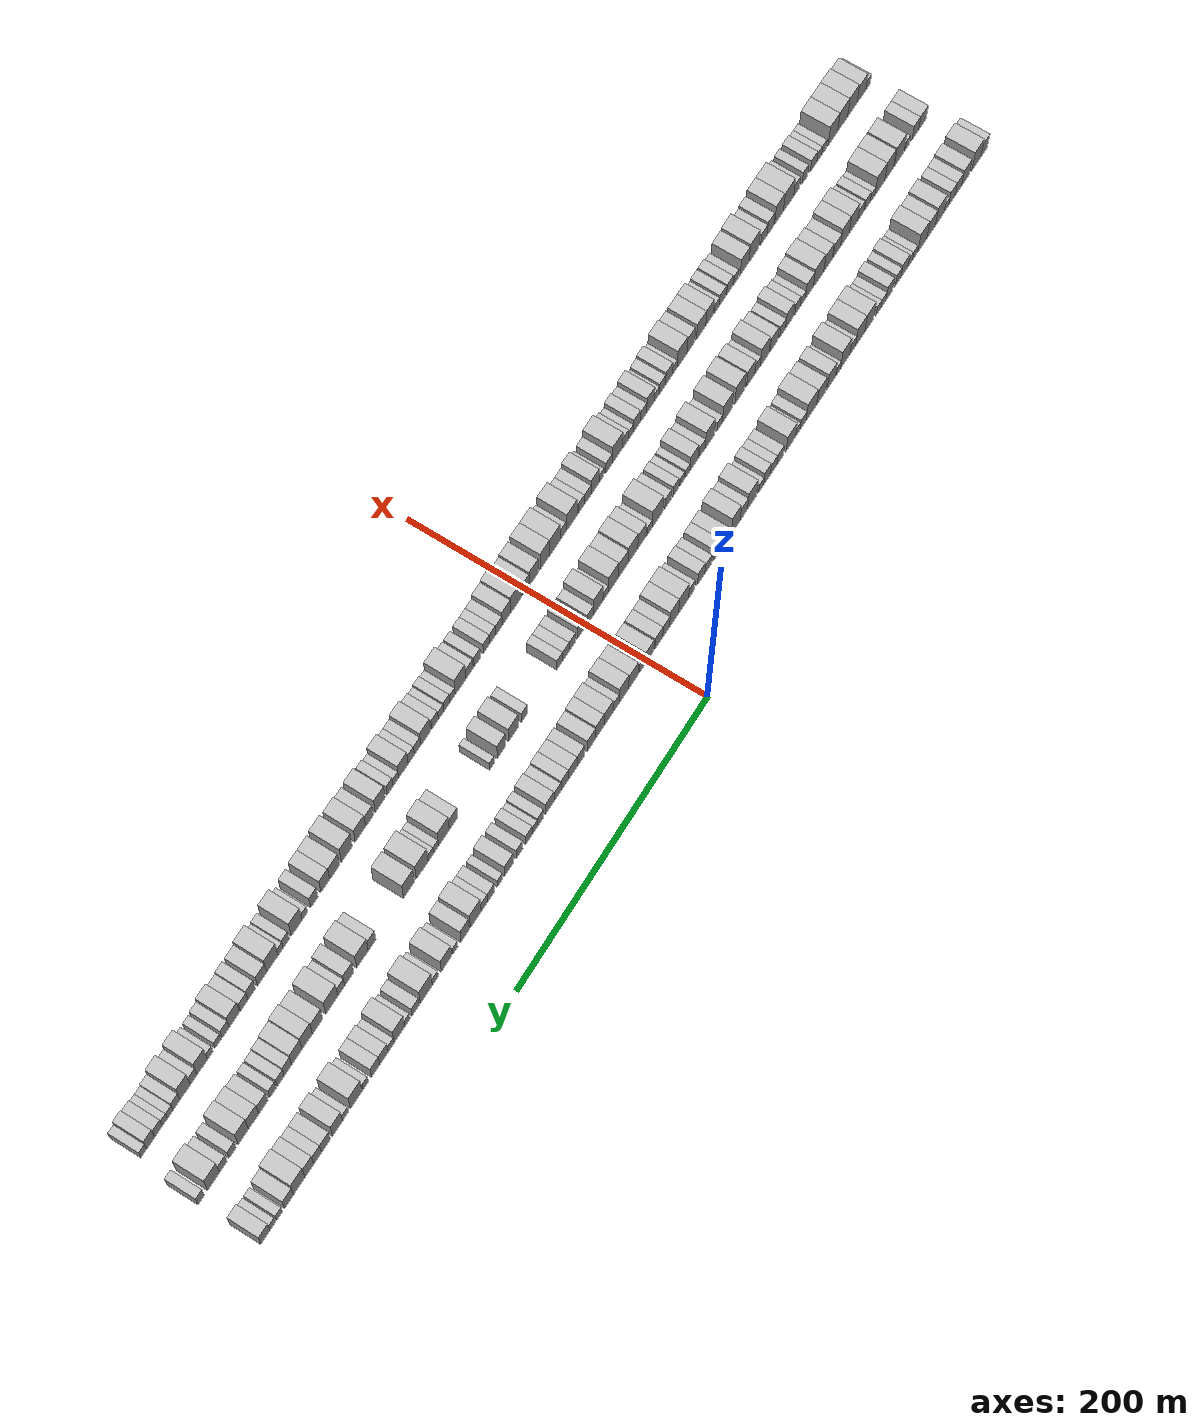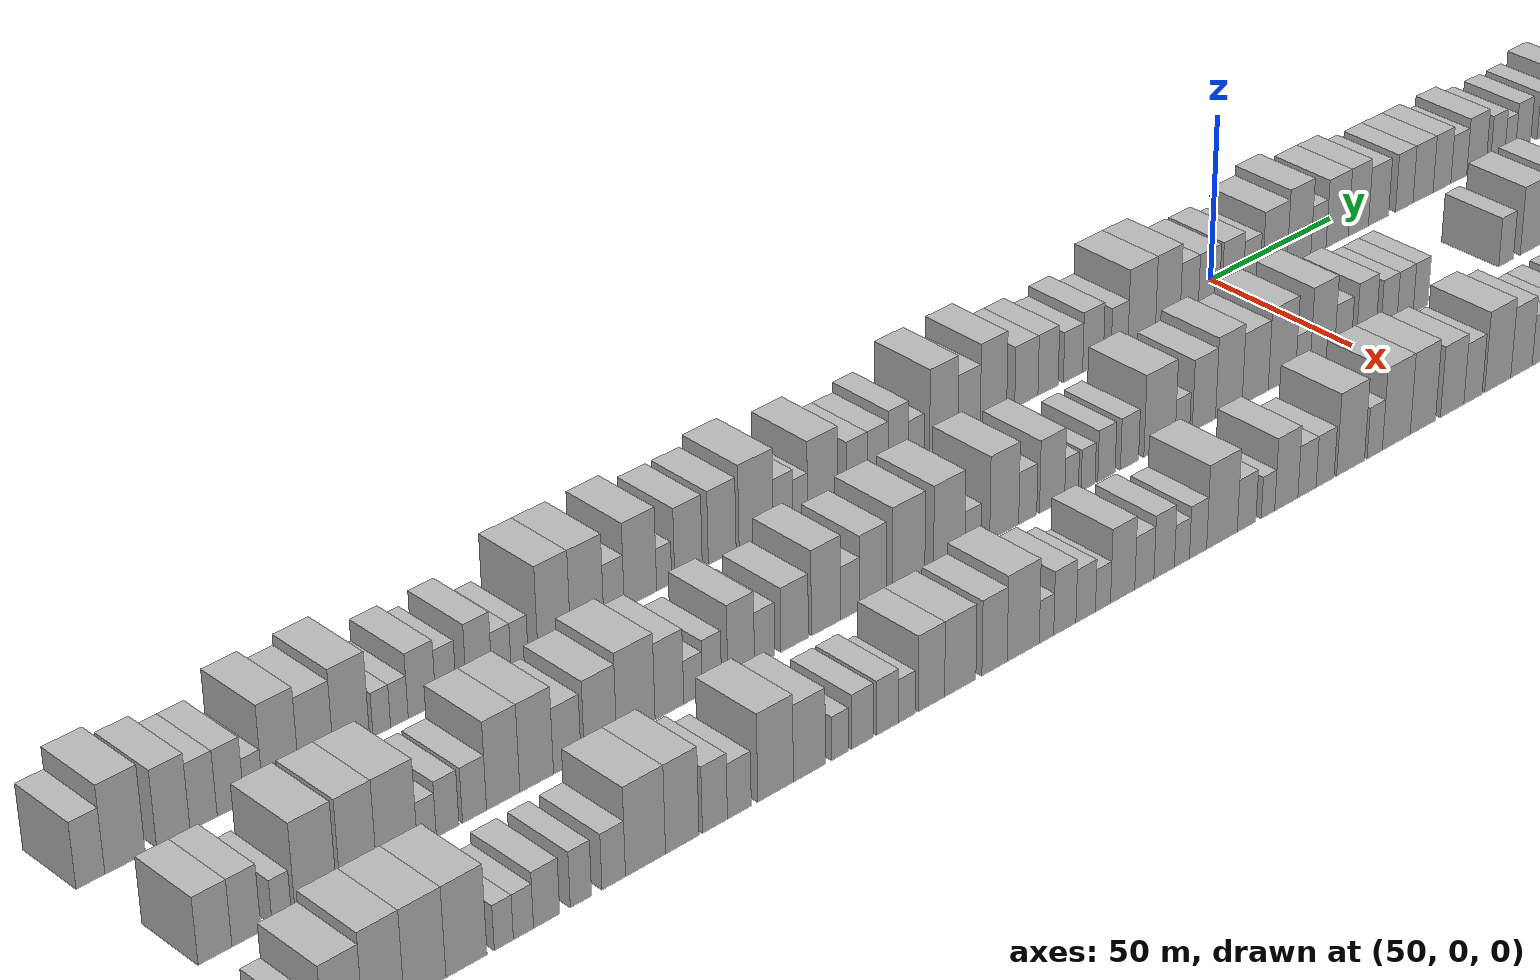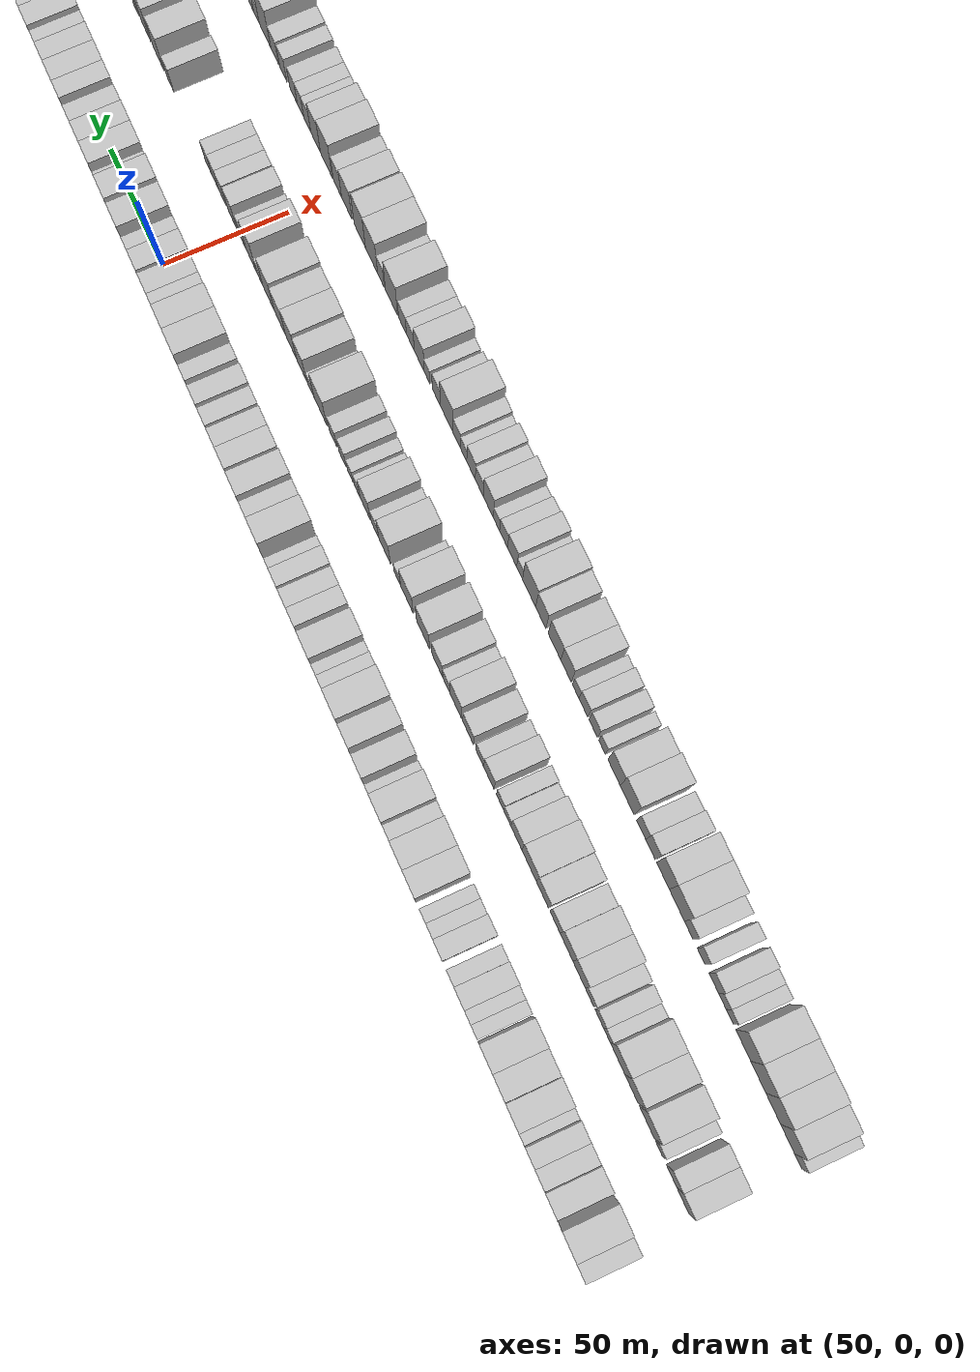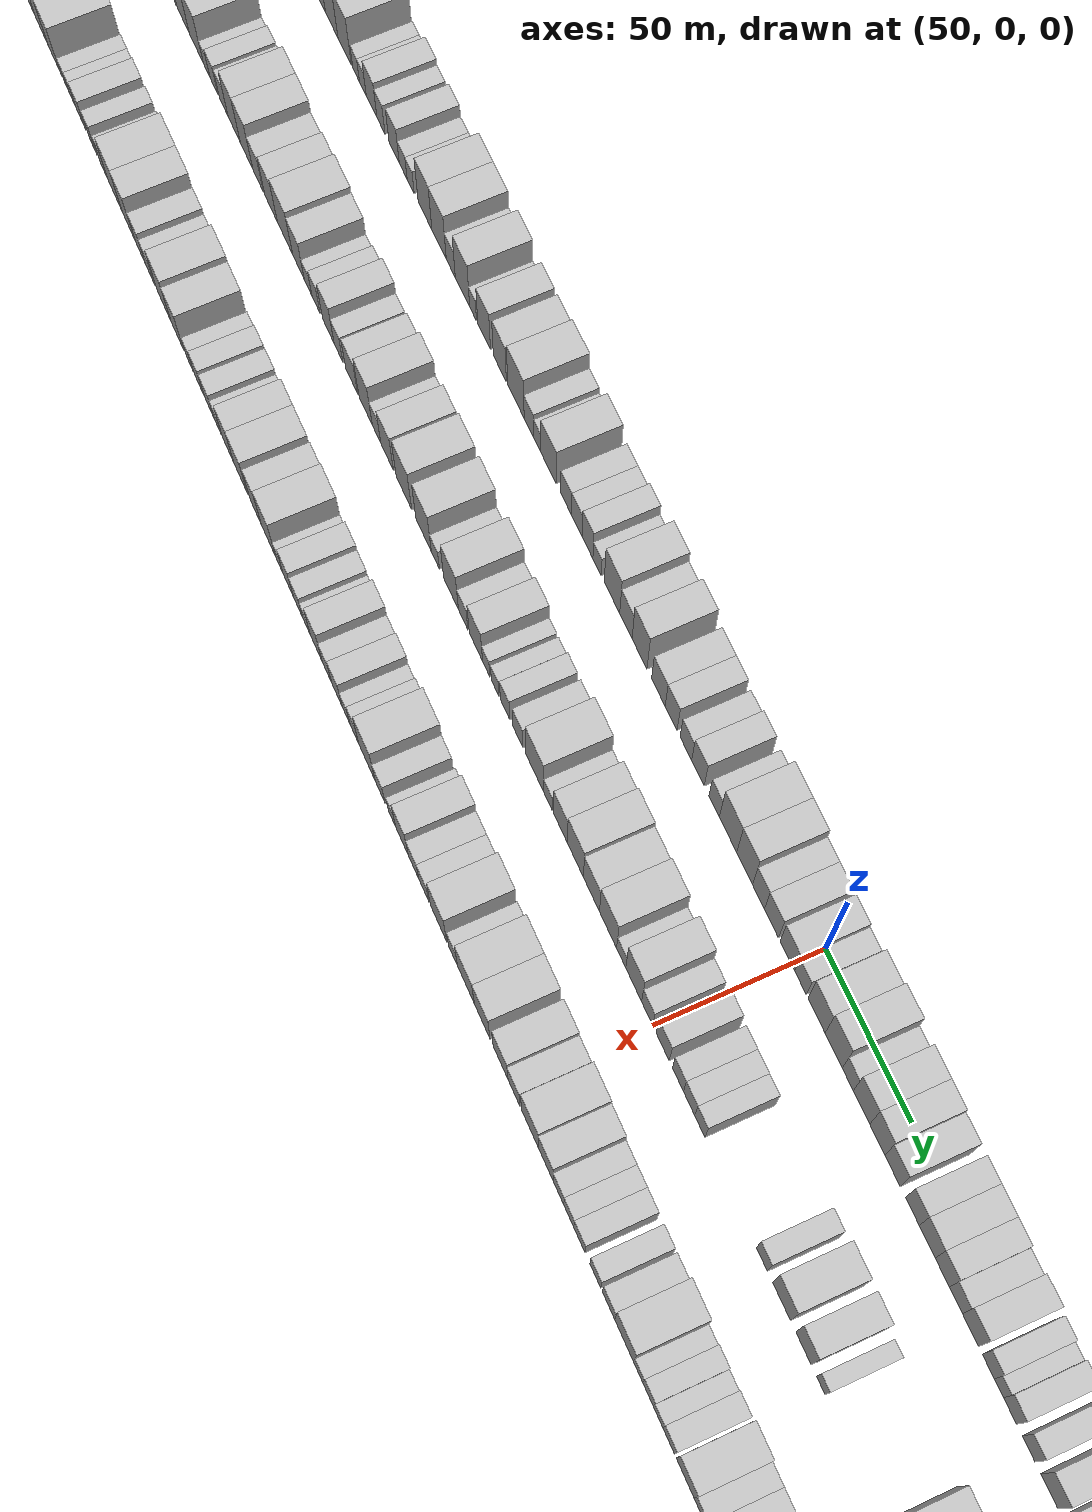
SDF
<sdf version="1.6">
 <world name="default">
  <scene>
   <sky><clouds><speed>12</speed></clouds></sky>
   <ambient>0.4 0.4 0.4 1</ambient>
   <background>0.7 0.7 0.7 1</background>
   <shadows>1</shadows>
  </scene>
  <gravity>0 0 -9.8066</gravity>
  <magnetic_field>6e-06 2.3e-05 -4.2e-05</magnetic_field>
  <physics default="0" name="default_physics" type="ode">
   <ode>
    <solver>
     <type>quick</type>
     <iters>10</iters>
     <sor>1.0</sor>
     <use_dynamic_moi_rescaling>0</use_dynamic_moi_rescaling>
    </solver>
    <constraints>
     <cfm>0</cfm>
     <erp>0.2</erp>
     <contact_max_correcting_vel>100</contact_max_correcting_vel>
     <contact_surface_layer>0.001</contact_surface_layer>
    </constraints>
   </ode>
   <max_step_size>0.004</max_step_size>
   <real_time_factor>1</real_time_factor>
   <real_time_update_rate>250</real_time_update_rate>
  </physics>
  <light name="sun" type="directional">
   <pose>0 0 10 0 0 0</pose>
   <diffuse>0.8 0.8 0.8 1</diffuse>
   <specular>0.2 0.2 0.2 1</specular>
   <attenuation>
    <range>1000</range>
    <constant>0.9</constant>
    <linear>0.01</linear>
    <quadratic>0.001</quadratic>
   </attenuation>
   <direction>-0.5 0.1 -0.9</direction>
  </light>
  <model name="building_1">
   <static>1</static>
   <pose>50.0000 -376.1810 0 0.000000 0.000000 0.000000</pose>
   <link name="link">
    <pose>0 0 9.00 0 0 0</pose>
    <collision name="collision"><geometry><box><size>20.0000 7.6380 18.0000</size></box></geometry></collision>
    <visual name="visual">
     <cast_shadows>0</cast_shadows>
     <geometry><box><size>20.0000 7.6380 18.0000</size></box></geometry>
     <material>
      <script>
       <uri>model://HANNAS_wall/materials/scripts</uri>
       <uri>model://HANNAS_wall/materials/textures</uri>
       <name>vrc/HANNAS_wall</name>
      </script>
     </material>
    </visual>
   </link>
  </model>
  <model name="building_2">
   <static>1</static>
   <pose>50.0000 -366.9421 0 0.000000 0.000000 0.000000</pose>
   <link name="link">
    <pose>0 0 12.00 0 0 0</pose>
    <collision name="collision"><geometry><box><size>20.0000 10.8399 24.0000</size></box></geometry></collision>
    <visual name="visual">
     <cast_shadows>0</cast_shadows>
     <geometry><box><size>20.0000 10.8399 24.0000</size></box></geometry>
     <material>
      <script>
       <uri>model://HANNAS_wall/materials/scripts</uri>
       <uri>model://HANNAS_wall/materials/textures</uri>
       <name>vrc/HANNAS_wall</name>
      </script>
     </material>
    </visual>
   </link>
  </model>
  <model name="building_3">
   <static>1</static>
   <pose>50.0000 -353.9611 0 0.000000 0.000000 0.000000</pose>
   <link name="link">
    <pose>0 0 10.50 0 0 0</pose>
    <collision name="collision"><geometry><box><size>20.0000 9.1221 21.0000</size></box></geometry></collision>
    <visual name="visual">
     <cast_shadows>0</cast_shadows>
     <geometry><box><size>20.0000 9.1221 21.0000</size></box></geometry>
     <material>
      <script>
       <uri>model://HANNAS_wall/materials/scripts</uri>
       <uri>model://HANNAS_wall/materials/textures</uri>
       <name>vrc/HANNAS_wall</name>
      </script>
     </material>
    </visual>
   </link>
  </model>
  <model name="building_4">
   <static>1</static>
   <pose>50.0000 -345.6792 0 0.000000 0.000000 0.000000</pose>
   <link name="link">
    <pose>0 0 9.00 0 0 0</pose>
    <collision name="collision"><geometry><box><size>20.0000 7.4416 18.0000</size></box></geometry></collision>
    <visual name="visual">
     <cast_shadows>0</cast_shadows>
     <geometry><box><size>20.0000 7.4416 18.0000</size></box></geometry>
     <material>
      <script>
       <uri>model://HANNAS_wall/materials/scripts</uri>
       <uri>model://HANNAS_wall/materials/textures</uri>
       <name>vrc/HANNAS_wall</name>
      </script>
     </material>
    </visual>
   </link>
  </model>
  <model name="building_5">
   <static>1</static>
   <pose>50.0000 -338.2252 0 0.000000 0.000000 0.000000</pose>
   <link name="link">
    <pose>0 0 9.00 0 0 0</pose>
    <collision name="collision"><geometry><box><size>20.0000 7.4664 18.0000</size></box></geometry></collision>
    <visual name="visual">
     <cast_shadows>0</cast_shadows>
     <geometry><box><size>20.0000 7.4664 18.0000</size></box></geometry>
     <material>
      <script>
       <uri>model://HANNAS_wall/materials/scripts</uri>
       <uri>model://HANNAS_wall/materials/textures</uri>
       <name>vrc/HANNAS_wall</name>
      </script>
     </material>
    </visual>
   </link>
  </model>
  <model name="building_6">
   <static>1</static>
   <pose>50.0000 -331.8795 0 0.000000 0.000000 0.000000</pose>
   <link name="link">
    <pose>0 0 6.00 0 0 0</pose>
    <collision name="collision"><geometry><box><size>20.0000 5.2251 12.0000</size></box></geometry></collision>
    <visual name="visual">
     <cast_shadows>0</cast_shadows>
     <geometry><box><size>20.0000 5.2251 12.0000</size></box></geometry>
     <material>
      <script>
       <uri>model://HANNAS_wall/materials/scripts</uri>
       <uri>model://HANNAS_wall/materials/textures</uri>
       <name>vrc/HANNAS_wall</name>
      </script>
     </material>
    </visual>
   </link>
  </model>
  <model name="building_7">
   <static>1</static>
   <pose>50.0000 -324.1723 0 0.000000 0.000000 0.000000</pose>
   <link name="link">
    <pose>0 0 12.00 0 0 0</pose>
    <collision name="collision"><geometry><box><size>20.0000 10.1895 24.0000</size></box></geometry></collision>
    <visual name="visual">
     <cast_shadows>0</cast_shadows>
     <geometry><box><size>20.0000 10.1895 24.0000</size></box></geometry>
     <material>
      <script>
       <uri>model://HANNAS_wall/materials/scripts</uri>
       <uri>model://HANNAS_wall/materials/textures</uri>
       <name>vrc/HANNAS_wall</name>
      </script>
     </material>
    </visual>
   </link>
  </model>
  <model name="building_8">
   <static>1</static>
   <pose>50.0000 -314.1347 0 0.000000 0.000000 0.000000</pose>
   <link name="link">
    <pose>0 0 10.50 0 0 0</pose>
    <collision name="collision"><geometry><box><size>20.0000 9.8857 21.0000</size></box></geometry></collision>
    <visual name="visual">
     <cast_shadows>0</cast_shadows>
     <geometry><box><size>20.0000 9.8857 21.0000</size></box></geometry>
     <material>
      <script>
       <uri>model://HANNAS_wall/materials/scripts</uri>
       <uri>model://HANNAS_wall/materials/textures</uri>
       <name>vrc/HANNAS_wall</name>
      </script>
     </material>
    </visual>
   </link>
  </model>
  <model name="building_9">
   <static>1</static>
   <pose>50.0000 -303.9926 0 0.000000 0.000000 0.000000</pose>
   <link name="link">
    <pose>0 0 12.00 0 0 0</pose>
    <collision name="collision"><geometry><box><size>20.0000 10.3984 24.0000</size></box></geometry></collision>
    <visual name="visual">
     <cast_shadows>0</cast_shadows>
     <geometry><box><size>20.0000 10.3984 24.0000</size></box></geometry>
     <material>
      <script>
       <uri>model://HANNAS_wall/materials/scripts</uri>
       <uri>model://HANNAS_wall/materials/textures</uri>
       <name>vrc/HANNAS_wall</name>
      </script>
     </material>
    </visual>
   </link>
  </model>
  <model name="building_10">
   <static>1</static>
   <pose>50.0000 -295.2278 0 0.000000 0.000000 0.000000</pose>
   <link name="link">
    <pose>0 0 6.00 0 0 0</pose>
    <collision name="collision"><geometry><box><size>20.0000 5.1312 12.0000</size></box></geometry></collision>
    <visual name="visual">
     <cast_shadows>0</cast_shadows>
     <geometry><box><size>20.0000 5.1312 12.0000</size></box></geometry>
     <material>
      <script>
       <uri>model://HANNAS_wall/materials/scripts</uri>
       <uri>model://HANNAS_wall/materials/textures</uri>
       <name>vrc/HANNAS_wall</name>
      </script>
     </material>
    </visual>
   </link>
  </model>
  <model name="building_11">
   <static>1</static>
   <pose>50.0000 -290.0710 0 0.000000 0.000000 0.000000</pose>
   <link name="link">
    <pose>0 0 6.00 0 0 0</pose>
    <collision name="collision"><geometry><box><size>20.0000 5.1823 12.0000</size></box></geometry></collision>
    <visual name="visual">
     <cast_shadows>0</cast_shadows>
     <geometry><box><size>20.0000 5.1823 12.0000</size></box></geometry>
     <material>
      <script>
       <uri>model://HANNAS_wall/materials/scripts</uri>
       <uri>model://HANNAS_wall/materials/textures</uri>
       <name>vrc/HANNAS_wall</name>
      </script>
     </material>
    </visual>
   </link>
  </model>
  <model name="building_12">
   <static>1</static>
   <pose>50.0000 -283.3765 0 0.000000 0.000000 0.000000</pose>
   <link name="link">
    <pose>0 0 9.00 0 0 0</pose>
    <collision name="collision"><geometry><box><size>20.0000 8.2066 18.0000</size></box></geometry></collision>
    <visual name="visual">
     <cast_shadows>0</cast_shadows>
     <geometry><box><size>20.0000 8.2066 18.0000</size></box></geometry>
     <material>
      <script>
       <uri>model://HANNAS_wall/materials/scripts</uri>
       <uri>model://HANNAS_wall/materials/textures</uri>
       <name>vrc/HANNAS_wall</name>
      </script>
     </material>
    </visual>
   </link>
  </model>
  <model name="building_13">
   <static>1</static>
   <pose>50.0000 -276.2098 0 0.000000 0.000000 0.000000</pose>
   <link name="link">
    <pose>0 0 7.50 0 0 0</pose>
    <collision name="collision"><geometry><box><size>20.0000 6.1267 15.0000</size></box></geometry></collision>
    <visual name="visual">
     <cast_shadows>0</cast_shadows>
     <geometry><box><size>20.0000 6.1267 15.0000</size></box></geometry>
     <material>
      <script>
       <uri>model://HANNAS_wall/materials/scripts</uri>
       <uri>model://HANNAS_wall/materials/textures</uri>
       <name>vrc/HANNAS_wall</name>
      </script>
     </material>
    </visual>
   </link>
  </model>
  <model name="building_14">
   <static>1</static>
   <pose>50.0000 -266.2871 0 0.000000 0.000000 0.000000</pose>
   <link name="link">
    <pose>0 0 9.00 0 0 0</pose>
    <collision name="collision"><geometry><box><size>20.0000 7.7186 18.0000</size></box></geometry></collision>
    <visual name="visual">
     <cast_shadows>0</cast_shadows>
     <geometry><box><size>20.0000 7.7186 18.0000</size></box></geometry>
     <material>
      <script>
       <uri>model://HANNAS_wall/materials/scripts</uri>
       <uri>model://HANNAS_wall/materials/textures</uri>
       <name>vrc/HANNAS_wall</name>
      </script>
     </material>
    </visual>
   </link>
  </model>
  <model name="building_15">
   <static>1</static>
   <pose>50.0000 -259.5210 0 0.000000 0.000000 0.000000</pose>
   <link name="link">
    <pose>0 0 6.00 0 0 0</pose>
    <collision name="collision"><geometry><box><size>20.0000 5.8136 12.0000</size></box></geometry></collision>
    <visual name="visual">
     <cast_shadows>0</cast_shadows>
     <geometry><box><size>20.0000 5.8136 12.0000</size></box></geometry>
     <material>
      <script>
       <uri>model://HANNAS_wall/materials/scripts</uri>
       <uri>model://HANNAS_wall/materials/textures</uri>
       <name>vrc/HANNAS_wall</name>
      </script>
     </material>
    </visual>
   </link>
  </model>
  <model name="building_16">
   <static>1</static>
   <pose>50.0000 -253.9832 0 0.000000 0.000000 0.000000</pose>
   <link name="link">
    <pose>0 0 6.00 0 0 0</pose>
    <collision name="collision"><geometry><box><size>20.0000 5.2621 12.0000</size></box></geometry></collision>
    <visual name="visual">
     <cast_shadows>0</cast_shadows>
     <geometry><box><size>20.0000 5.2621 12.0000</size></box></geometry>
     <material>
      <script>
       <uri>model://HANNAS_wall/materials/scripts</uri>
       <uri>model://HANNAS_wall/materials/textures</uri>
       <name>vrc/HANNAS_wall</name>
      </script>
     </material>
    </visual>
   </link>
  </model>
  <model name="building_17">
   <static>1</static>
   <pose>50.0000 -243.2892 0 0.000000 0.000000 0.000000</pose>
   <link name="link">
    <pose>0 0 12.00 0 0 0</pose>
    <collision name="collision"><geometry><box><size>20.0000 10.1258 24.0000</size></box></geometry></collision>
    <visual name="visual">
     <cast_shadows>0</cast_shadows>
     <geometry><box><size>20.0000 10.1258 24.0000</size></box></geometry>
     <material>
      <script>
       <uri>model://HANNAS_wall/materials/scripts</uri>
       <uri>model://HANNAS_wall/materials/textures</uri>
       <name>vrc/HANNAS_wall</name>
      </script>
     </material>
    </visual>
   </link>
  </model>
  <model name="building_18">
   <static>1</static>
   <pose>50.0000 -232.9843 0 0.000000 0.000000 0.000000</pose>
   <link name="link">
    <pose>0 0 12.00 0 0 0</pose>
    <collision name="collision"><geometry><box><size>20.0000 10.4840 24.0000</size></box></geometry></collision>
    <visual name="visual">
     <cast_shadows>0</cast_shadows>
     <geometry><box><size>20.0000 10.4840 24.0000</size></box></geometry>
     <material>
      <script>
       <uri>model://HANNAS_wall/materials/scripts</uri>
       <uri>model://HANNAS_wall/materials/textures</uri>
       <name>vrc/HANNAS_wall</name>
      </script>
     </material>
    </visual>
   </link>
  </model>
  <model name="building_19">
   <static>1</static>
   <pose>50.0000 -224.4705 0 0.000000 0.000000 0.000000</pose>
   <link name="link">
    <pose>0 0 7.50 0 0 0</pose>
    <collision name="collision"><geometry><box><size>20.0000 6.5437 15.0000</size></box></geometry></collision>
    <visual name="visual">
     <cast_shadows>0</cast_shadows>
     <geometry><box><size>20.0000 6.5437 15.0000</size></box></geometry>
     <material>
      <script>
       <uri>model://HANNAS_wall/materials/scripts</uri>
       <uri>model://HANNAS_wall/materials/textures</uri>
       <name>vrc/HANNAS_wall</name>
      </script>
     </material>
    </visual>
   </link>
  </model>
  <model name="building_20">
   <static>1</static>
   <pose>50.0000 -215.9968 0 0.000000 0.000000 0.000000</pose>
   <link name="link">
    <pose>0 0 12.00 0 0 0</pose>
    <collision name="collision"><geometry><box><size>20.0000 10.4036 24.0000</size></box></geometry></collision>
    <visual name="visual">
     <cast_shadows>0</cast_shadows>
     <geometry><box><size>20.0000 10.4036 24.0000</size></box></geometry>
     <material>
      <script>
       <uri>model://HANNAS_wall/materials/scripts</uri>
       <uri>model://HANNAS_wall/materials/textures</uri>
       <name>vrc/HANNAS_wall</name>
      </script>
     </material>
    </visual>
   </link>
  </model>
  <model name="building_21">
   <static>1</static>
   <pose>50.0000 -208.3638 0 0.000000 0.000000 0.000000</pose>
   <link name="link">
    <pose>0 0 6.00 0 0 0</pose>
    <collision name="collision"><geometry><box><size>20.0000 4.8625 12.0000</size></box></geometry></collision>
    <visual name="visual">
     <cast_shadows>0</cast_shadows>
     <geometry><box><size>20.0000 4.8625 12.0000</size></box></geometry>
     <material>
      <script>
       <uri>model://HANNAS_wall/materials/scripts</uri>
       <uri>model://HANNAS_wall/materials/textures</uri>
       <name>vrc/HANNAS_wall</name>
      </script>
     </material>
    </visual>
   </link>
  </model>
  <model name="building_22">
   <static>1</static>
   <pose>50.0000 -200.4402 0 0.000000 0.000000 0.000000</pose>
   <link name="link">
    <pose>0 0 10.50 0 0 0</pose>
    <collision name="collision"><geometry><box><size>20.0000 8.9846 21.0000</size></box></geometry></collision>
    <visual name="visual">
     <cast_shadows>0</cast_shadows>
     <geometry><box><size>20.0000 8.9846 21.0000</size></box></geometry>
     <material>
      <script>
       <uri>model://HANNAS_wall/materials/scripts</uri>
       <uri>model://HANNAS_wall/materials/textures</uri>
       <name>vrc/HANNAS_wall</name>
      </script>
     </material>
    </visual>
   </link>
  </model>
  <model name="building_23">
   <static>1</static>
   <pose>50.0000 -189.3525 0 0.000000 0.000000 0.000000</pose>
   <link name="link">
    <pose>0 0 10.50 0 0 0</pose>
    <collision name="collision"><geometry><box><size>20.0000 9.1908 21.0000</size></box></geometry></collision>
    <visual name="visual">
     <cast_shadows>0</cast_shadows>
     <geometry><box><size>20.0000 9.1908 21.0000</size></box></geometry>
     <material>
      <script>
       <uri>model://HANNAS_wall/materials/scripts</uri>
       <uri>model://HANNAS_wall/materials/textures</uri>
       <name>vrc/HANNAS_wall</name>
      </script>
     </material>
    </visual>
   </link>
  </model>
  <model name="building_24">
   <static>1</static>
   <pose>50.0000 -178.0189 0 0.000000 0.000000 0.000000</pose>
   <link name="link">
    <pose>0 0 12.00 0 0 0</pose>
    <collision name="collision"><geometry><box><size>20.0000 11.4764 24.0000</size></box></geometry></collision>
    <visual name="visual">
     <cast_shadows>0</cast_shadows>
     <geometry><box><size>20.0000 11.4764 24.0000</size></box></geometry>
     <material>
      <script>
       <uri>model://HANNAS_wall/materials/scripts</uri>
       <uri>model://HANNAS_wall/materials/textures</uri>
       <name>vrc/HANNAS_wall</name>
      </script>
     </material>
    </visual>
   </link>
  </model>
  <model name="building_25">
   <static>1</static>
   <pose>50.0000 -168.9324 0 0.000000 0.000000 0.000000</pose>
   <link name="link">
    <pose>0 0 7.50 0 0 0</pose>
    <collision name="collision"><geometry><box><size>20.0000 6.6967 15.0000</size></box></geometry></collision>
    <visual name="visual">
     <cast_shadows>0</cast_shadows>
     <geometry><box><size>20.0000 6.6967 15.0000</size></box></geometry>
     <material>
      <script>
       <uri>model://HANNAS_wall/materials/scripts</uri>
       <uri>model://HANNAS_wall/materials/textures</uri>
       <name>vrc/HANNAS_wall</name>
      </script>
     </material>
    </visual>
   </link>
  </model>
  <model name="building_26">
   <static>1</static>
   <pose>50.0000 -163.1304 0 0.000000 0.000000 0.000000</pose>
   <link name="link">
    <pose>0 0 6.00 0 0 0</pose>
    <collision name="collision"><geometry><box><size>20.0000 4.9074 12.0000</size></box></geometry></collision>
    <visual name="visual">
     <cast_shadows>0</cast_shadows>
     <geometry><box><size>20.0000 4.9074 12.0000</size></box></geometry>
     <material>
      <script>
       <uri>model://HANNAS_wall/materials/scripts</uri>
       <uri>model://HANNAS_wall/materials/textures</uri>
       <name>vrc/HANNAS_wall</name>
      </script>
     </material>
    </visual>
   </link>
  </model>
  <model name="building_27">
   <static>1</static>
   <pose>50.0000 -155.4353 0 0.000000 0.000000 0.000000</pose>
   <link name="link">
    <pose>0 0 10.50 0 0 0</pose>
    <collision name="collision"><geometry><box><size>20.0000 10.4826 21.0000</size></box></geometry></collision>
    <visual name="visual">
     <cast_shadows>0</cast_shadows>
     <geometry><box><size>20.0000 10.4826 21.0000</size></box></geometry>
     <material>
      <script>
       <uri>model://HANNAS_wall/materials/scripts</uri>
       <uri>model://HANNAS_wall/materials/textures</uri>
       <name>vrc/HANNAS_wall</name>
      </script>
     </material>
    </visual>
   </link>
  </model>
  <model name="building_28">
   <static>1</static>
   <pose>50.0000 -143.5579 0 0.000000 0.000000 0.000000</pose>
   <link name="link">
    <pose>0 0 7.50 0 0 0</pose>
    <collision name="collision"><geometry><box><size>20.0000 7.2723 15.0000</size></box></geometry></collision>
    <visual name="visual">
     <cast_shadows>0</cast_shadows>
     <geometry><box><size>20.0000 7.2723 15.0000</size></box></geometry>
     <material>
      <script>
       <uri>model://HANNAS_wall/materials/scripts</uri>
       <uri>model://HANNAS_wall/materials/textures</uri>
       <name>vrc/HANNAS_wall</name>
      </script>
     </material>
    </visual>
   </link>
  </model>
  <model name="building_29">
   <static>1</static>
   <pose>50.0000 -136.2918 0 0.000000 0.000000 0.000000</pose>
   <link name="link">
    <pose>0 0 7.50 0 0 0</pose>
    <collision name="collision"><geometry><box><size>20.0000 7.2600 15.0000</size></box></geometry></collision>
    <visual name="visual">
     <cast_shadows>0</cast_shadows>
     <geometry><box><size>20.0000 7.2600 15.0000</size></box></geometry>
     <material>
      <script>
       <uri>model://HANNAS_wall/materials/scripts</uri>
       <uri>model://HANNAS_wall/materials/textures</uri>
       <name>vrc/HANNAS_wall</name>
      </script>
     </material>
    </visual>
   </link>
  </model>
  <model name="building_30">
   <static>1</static>
   <pose>50.0000 -129.0515 0 0.000000 0.000000 0.000000</pose>
   <link name="link">
    <pose>0 0 9.00 0 0 0</pose>
    <collision name="collision"><geometry><box><size>20.0000 7.2206 18.0000</size></box></geometry></collision>
    <visual name="visual">
     <cast_shadows>0</cast_shadows>
     <geometry><box><size>20.0000 7.2206 18.0000</size></box></geometry>
     <material>
      <script>
       <uri>model://HANNAS_wall/materials/scripts</uri>
       <uri>model://HANNAS_wall/materials/textures</uri>
       <name>vrc/HANNAS_wall</name>
      </script>
     </material>
    </visual>
   </link>
  </model>
  <model name="building_31">
   <static>1</static>
   <pose>50.0000 -122.6637 0 0.000000 0.000000 0.000000</pose>
   <link name="link">
    <pose>0 0 6.00 0 0 0</pose>
    <collision name="collision"><geometry><box><size>20.0000 5.5550 12.0000</size></box></geometry></collision>
    <visual name="visual">
     <cast_shadows>0</cast_shadows>
     <geometry><box><size>20.0000 5.5550 12.0000</size></box></geometry>
     <material>
      <script>
       <uri>model://HANNAS_wall/materials/scripts</uri>
       <uri>model://HANNAS_wall/materials/textures</uri>
       <name>vrc/HANNAS_wall</name>
      </script>
     </material>
    </visual>
   </link>
  </model>
  <model name="building_32">
   <static>1</static>
   <pose>50.0000 -112.7731 0 0.000000 0.000000 0.000000</pose>
   <link name="link">
    <pose>0 0 12.00 0 0 0</pose>
    <collision name="collision"><geometry><box><size>20.0000 10.2260 24.0000</size></box></geometry></collision>
    <visual name="visual">
     <cast_shadows>0</cast_shadows>
     <geometry><box><size>20.0000 10.2260 24.0000</size></box></geometry>
     <material>
      <script>
       <uri>model://HANNAS_wall/materials/scripts</uri>
       <uri>model://HANNAS_wall/materials/textures</uri>
       <name>vrc/HANNAS_wall</name>
      </script>
     </material>
    </visual>
   </link>
  </model>
  <model name="building_33">
   <static>1</static>
   <pose>50.0000 -103.6081 0 0.000000 0.000000 0.000000</pose>
   <link name="link">
    <pose>0 0 9.00 0 0 0</pose>
    <collision name="collision"><geometry><box><size>20.0000 8.1040 18.0000</size></box></geometry></collision>
    <visual name="visual">
     <cast_shadows>0</cast_shadows>
     <geometry><box><size>20.0000 8.1040 18.0000</size></box></geometry>
     <material>
      <script>
       <uri>model://HANNAS_wall/materials/scripts</uri>
       <uri>model://HANNAS_wall/materials/textures</uri>
       <name>vrc/HANNAS_wall</name>
      </script>
     </material>
    </visual>
   </link>
  </model>
  <model name="building_34">
   <static>1</static>
   <pose>50.0000 -94.7044 0 0.000000 0.000000 0.000000</pose>
   <link name="link">
    <pose>0 0 12.00 0 0 0</pose>
    <collision name="collision"><geometry><box><size>20.0000 9.7034 24.0000</size></box></geometry></collision>
    <visual name="visual">
     <cast_shadows>0</cast_shadows>
     <geometry><box><size>20.0000 9.7034 24.0000</size></box></geometry>
     <material>
      <script>
       <uri>model://HANNAS_wall/materials/scripts</uri>
       <uri>model://HANNAS_wall/materials/textures</uri>
       <name>vrc/HANNAS_wall</name>
      </script>
     </material>
    </visual>
   </link>
  </model>
  <model name="building_35">
   <static>1</static>
   <pose>50.0000 -82.5195 0 0.000000 0.000000 0.000000</pose>
   <link name="link">
    <pose>0 0 9.00 0 0 0</pose>
    <collision name="collision"><geometry><box><size>20.0000 8.6664 18.0000</size></box></geometry></collision>
    <visual name="visual">
     <cast_shadows>0</cast_shadows>
     <geometry><box><size>20.0000 8.6664 18.0000</size></box></geometry>
     <material>
      <script>
       <uri>model://HANNAS_wall/materials/scripts</uri>
       <uri>model://HANNAS_wall/materials/textures</uri>
       <name>vrc/HANNAS_wall</name>
      </script>
     </material>
    </visual>
   </link>
  </model>
  <model name="building_36">
   <static>1</static>
   <pose>50.0000 -74.3905 0 0.000000 0.000000 0.000000</pose>
   <link name="link">
    <pose>0 0 9.00 0 0 0</pose>
    <collision name="collision"><geometry><box><size>20.0000 7.5917 18.0000</size></box></geometry></collision>
    <visual name="visual">
     <cast_shadows>0</cast_shadows>
     <geometry><box><size>20.0000 7.5917 18.0000</size></box></geometry>
     <material>
      <script>
       <uri>model://HANNAS_wall/materials/scripts</uri>
       <uri>model://HANNAS_wall/materials/textures</uri>
       <name>vrc/HANNAS_wall</name>
      </script>
     </material>
    </visual>
   </link>
  </model>
  <model name="building_37">
   <static>1</static>
   <pose>50.0000 -64.9532 0 0.000000 0.000000 0.000000</pose>
   <link name="link">
    <pose>0 0 7.50 0 0 0</pose>
    <collision name="collision"><geometry><box><size>20.0000 7.2829 15.0000</size></box></geometry></collision>
    <visual name="visual">
     <cast_shadows>0</cast_shadows>
     <geometry><box><size>20.0000 7.2829 15.0000</size></box></geometry>
     <material>
      <script>
       <uri>model://HANNAS_wall/materials/scripts</uri>
       <uri>model://HANNAS_wall/materials/textures</uri>
       <name>vrc/HANNAS_wall</name>
      </script>
     </material>
    </visual>
   </link>
  </model>
  <model name="building_38">
   <static>1</static>
   <pose>50.0000 -57.3592 0 0.000000 0.000000 0.000000</pose>
   <link name="link">
    <pose>0 0 9.00 0 0 0</pose>
    <collision name="collision"><geometry><box><size>20.0000 7.9051 18.0000</size></box></geometry></collision>
    <visual name="visual">
     <cast_shadows>0</cast_shadows>
     <geometry><box><size>20.0000 7.9051 18.0000</size></box></geometry>
     <material>
      <script>
       <uri>model://HANNAS_wall/materials/scripts</uri>
       <uri>model://HANNAS_wall/materials/textures</uri>
       <name>vrc/HANNAS_wall</name>
      </script>
     </material>
    </visual>
   </link>
  </model>
  <model name="building_39">
   <static>1</static>
   <pose>50.0000 -47.1636 0 0.000000 0.000000 0.000000</pose>
   <link name="link">
    <pose>0 0 7.50 0 0 0</pose>
    <collision name="collision"><geometry><box><size>20.0000 6.4860 15.0000</size></box></geometry></collision>
    <visual name="visual">
     <cast_shadows>0</cast_shadows>
     <geometry><box><size>20.0000 6.4860 15.0000</size></box></geometry>
     <material>
      <script>
       <uri>model://HANNAS_wall/materials/scripts</uri>
       <uri>model://HANNAS_wall/materials/textures</uri>
       <name>vrc/HANNAS_wall</name>
      </script>
     </material>
    </visual>
   </link>
  </model>
  <model name="building_40">
   <static>1</static>
   <pose>50.0000 -38.5494 0 0.000000 0.000000 0.000000</pose>
   <link name="link">
    <pose>0 0 12.00 0 0 0</pose>
    <collision name="collision"><geometry><box><size>20.0000 10.7425 24.0000</size></box></geometry></collision>
    <visual name="visual">
     <cast_shadows>0</cast_shadows>
     <geometry><box><size>20.0000 10.7425 24.0000</size></box></geometry>
     <material>
      <script>
       <uri>model://HANNAS_wall/materials/scripts</uri>
       <uri>model://HANNAS_wall/materials/textures</uri>
       <name>vrc/HANNAS_wall</name>
      </script>
     </material>
    </visual>
   </link>
  </model>
  <model name="building_41">
   <static>1</static>
   <pose>50.0000 -28.3205 0 0.000000 0.000000 0.000000</pose>
   <link name="link">
    <pose>0 0 12.00 0 0 0</pose>
    <collision name="collision"><geometry><box><size>20.0000 9.7152 24.0000</size></box></geometry></collision>
    <visual name="visual">
     <cast_shadows>0</cast_shadows>
     <geometry><box><size>20.0000 9.7152 24.0000</size></box></geometry>
     <material>
      <script>
       <uri>model://HANNAS_wall/materials/scripts</uri>
       <uri>model://HANNAS_wall/materials/textures</uri>
       <name>vrc/HANNAS_wall</name>
      </script>
     </material>
    </visual>
   </link>
  </model>
  <model name="building_42">
   <static>1</static>
   <pose>50.0000 -19.8484 0 0.000000 0.000000 0.000000</pose>
   <link name="link">
    <pose>0 0 9.00 0 0 0</pose>
    <collision name="collision"><geometry><box><size>20.0000 7.2290 18.0000</size></box></geometry></collision>
    <visual name="visual">
     <cast_shadows>0</cast_shadows>
     <geometry><box><size>20.0000 7.2290 18.0000</size></box></geometry>
     <material>
      <script>
       <uri>model://HANNAS_wall/materials/scripts</uri>
       <uri>model://HANNAS_wall/materials/textures</uri>
       <name>vrc/HANNAS_wall</name>
      </script>
     </material>
    </visual>
   </link>
  </model>
  <model name="building_43">
   <static>1</static>
   <pose>50.0000 -12.0045 0 0.000000 0.000000 0.000000</pose>
   <link name="link">
    <pose>0 0 9.00 0 0 0</pose>
    <collision name="collision"><geometry><box><size>20.0000 8.4589 18.0000</size></box></geometry></collision>
    <visual name="visual">
     <cast_shadows>0</cast_shadows>
     <geometry><box><size>20.0000 8.4589 18.0000</size></box></geometry>
     <material>
      <script>
       <uri>model://HANNAS_wall/materials/scripts</uri>
       <uri>model://HANNAS_wall/materials/textures</uri>
       <name>vrc/HANNAS_wall</name>
      </script>
     </material>
    </visual>
   </link>
  </model>
  <model name="building_44">
   <static>1</static>
   <pose>50.0000 -2.4323 0 0.000000 0.000000 0.000000</pose>
   <link name="link">
    <pose>0 0 9.00 0 0 0</pose>
    <collision name="collision"><geometry><box><size>20.0000 8.6855 18.0000</size></box></geometry></collision>
    <visual name="visual">
     <cast_shadows>0</cast_shadows>
     <geometry><box><size>20.0000 8.6855 18.0000</size></box></geometry>
     <material>
      <script>
       <uri>model://HANNAS_wall/materials/scripts</uri>
       <uri>model://HANNAS_wall/materials/textures</uri>
       <name>vrc/HANNAS_wall</name>
      </script>
     </material>
    </visual>
   </link>
  </model>
  <model name="building_45">
   <static>1</static>
   <pose>50.0000 5.3579 0 0.000000 0.000000 0.000000</pose>
   <link name="link">
    <pose>0 0 7.50 0 0 0</pose>
    <collision name="collision"><geometry><box><size>20.0000 6.8949 15.0000</size></box></geometry></collision>
    <visual name="visual">
     <cast_shadows>0</cast_shadows>
     <geometry><box><size>20.0000 6.8949 15.0000</size></box></geometry>
     <material>
      <script>
       <uri>model://HANNAS_wall/materials/scripts</uri>
       <uri>model://HANNAS_wall/materials/textures</uri>
       <name>vrc/HANNAS_wall</name>
      </script>
     </material>
    </visual>
   </link>
  </model>
  <model name="building_46">
   <static>1</static>
   <pose>50.0000 14.8771 0 0.000000 0.000000 0.000000</pose>
   <link name="link">
    <pose>0 0 10.50 0 0 0</pose>
    <collision name="collision"><geometry><box><size>20.0000 10.1435 21.0000</size></box></geometry></collision>
    <visual name="visual">
     <cast_shadows>0</cast_shadows>
     <geometry><box><size>20.0000 10.1435 21.0000</size></box></geometry>
     <material>
      <script>
       <uri>model://HANNAS_wall/materials/scripts</uri>
       <uri>model://HANNAS_wall/materials/textures</uri>
       <name>vrc/HANNAS_wall</name>
      </script>
     </material>
    </visual>
   </link>
  </model>
  <model name="building_47">
   <static>1</static>
   <pose>50.0000 24.9479 0 0.000000 0.000000 0.000000</pose>
   <link name="link">
    <pose>0 0 12.00 0 0 0</pose>
    <collision name="collision"><geometry><box><size>20.0000 9.9981 24.0000</size></box></geometry></collision>
    <visual name="visual">
     <cast_shadows>0</cast_shadows>
     <geometry><box><size>20.0000 9.9981 24.0000</size></box></geometry>
     <material>
      <script>
       <uri>model://HANNAS_wall/materials/scripts</uri>
       <uri>model://HANNAS_wall/materials/textures</uri>
       <name>vrc/HANNAS_wall</name>
      </script>
     </material>
    </visual>
   </link>
  </model>
  <model name="building_48">
   <static>1</static>
   <pose>50.0000 33.1566 0 0.000000 0.000000 0.000000</pose>
   <link name="link">
    <pose>0 0 7.50 0 0 0</pose>
    <collision name="collision"><geometry><box><size>20.0000 6.4193 15.0000</size></box></geometry></collision>
    <visual name="visual">
     <cast_shadows>0</cast_shadows>
     <geometry><box><size>20.0000 6.4193 15.0000</size></box></geometry>
     <material>
      <script>
       <uri>model://HANNAS_wall/materials/scripts</uri>
       <uri>model://HANNAS_wall/materials/textures</uri>
       <name>vrc/HANNAS_wall</name>
      </script>
     </material>
    </visual>
   </link>
  </model>
  <model name="building_49">
   <static>1</static>
   <pose>50.0000 41.0933 0 0.000000 0.000000 0.000000</pose>
   <link name="link">
    <pose>0 0 10.50 0 0 0</pose>
    <collision name="collision"><geometry><box><size>20.0000 9.4541 21.0000</size></box></geometry></collision>
    <visual name="visual">
     <cast_shadows>0</cast_shadows>
     <geometry><box><size>20.0000 9.4541 21.0000</size></box></geometry>
     <material>
      <script>
       <uri>model://HANNAS_wall/materials/scripts</uri>
       <uri>model://HANNAS_wall/materials/textures</uri>
       <name>vrc/HANNAS_wall</name>
      </script>
     </material>
    </visual>
   </link>
  </model>
  <model name="building_50">
   <static>1</static>
   <pose>50.0000 50.1403 0 0.000000 0.000000 0.000000</pose>
   <link name="link">
    <pose>0 0 10.50 0 0 0</pose>
    <collision name="collision"><geometry><box><size>20.0000 8.6399 21.0000</size></box></geometry></collision>
    <visual name="visual">
     <cast_shadows>0</cast_shadows>
     <geometry><box><size>20.0000 8.6399 21.0000</size></box></geometry>
     <material>
      <script>
       <uri>model://HANNAS_wall/materials/scripts</uri>
       <uri>model://HANNAS_wall/materials/textures</uri>
       <name>vrc/HANNAS_wall</name>
      </script>
     </material>
    </visual>
   </link>
  </model>
  <model name="building_51">
   <static>1</static>
   <pose>50.0000 58.8040 0 0.000000 0.000000 0.000000</pose>
   <link name="link">
    <pose>0 0 9.00 0 0 0</pose>
    <collision name="collision"><geometry><box><size>20.0000 8.6874 18.0000</size></box></geometry></collision>
    <visual name="visual">
     <cast_shadows>0</cast_shadows>
     <geometry><box><size>20.0000 8.6874 18.0000</size></box></geometry>
     <material>
      <script>
       <uri>model://HANNAS_wall/materials/scripts</uri>
       <uri>model://HANNAS_wall/materials/textures</uri>
       <name>vrc/HANNAS_wall</name>
      </script>
     </material>
    </visual>
   </link>
  </model>
  <model name="building_52">
   <static>1</static>
   <pose>50.0000 69.9709 0 0.000000 0.000000 0.000000</pose>
   <link name="link">
    <pose>0 0 9.00 0 0 0</pose>
    <collision name="collision"><geometry><box><size>20.0000 7.6463 18.0000</size></box></geometry></collision>
    <visual name="visual">
     <cast_shadows>0</cast_shadows>
     <geometry><box><size>20.0000 7.6463 18.0000</size></box></geometry>
     <material>
      <script>
       <uri>model://HANNAS_wall/materials/scripts</uri>
       <uri>model://HANNAS_wall/materials/textures</uri>
       <name>vrc/HANNAS_wall</name>
      </script>
     </material>
    </visual>
   </link>
  </model>
  <model name="building_53">
   <static>1</static>
   <pose>50.0000 78.2088 0 0.000000 0.000000 0.000000</pose>
   <link name="link">
    <pose>0 0 9.00 0 0 0</pose>
    <collision name="collision"><geometry><box><size>20.0000 8.8295 18.0000</size></box></geometry></collision>
    <visual name="visual">
     <cast_shadows>0</cast_shadows>
     <geometry><box><size>20.0000 8.8295 18.0000</size></box></geometry>
     <material>
      <script>
       <uri>model://HANNAS_wall/materials/scripts</uri>
       <uri>model://HANNAS_wall/materials/textures</uri>
       <name>vrc/HANNAS_wall</name>
      </script>
     </material>
    </visual>
   </link>
  </model>
  <model name="building_54">
   <static>1</static>
   <pose>50.0000 86.5597 0 0.000000 0.000000 0.000000</pose>
   <link name="link">
    <pose>0 0 9.00 0 0 0</pose>
    <collision name="collision"><geometry><box><size>20.0000 7.8723 18.0000</size></box></geometry></collision>
    <visual name="visual">
     <cast_shadows>0</cast_shadows>
     <geometry><box><size>20.0000 7.8723 18.0000</size></box></geometry>
     <material>
      <script>
       <uri>model://HANNAS_wall/materials/scripts</uri>
       <uri>model://HANNAS_wall/materials/textures</uri>
       <name>vrc/HANNAS_wall</name>
      </script>
     </material>
    </visual>
   </link>
  </model>
  <model name="building_55">
   <static>1</static>
   <pose>50.0000 94.0495 0 0.000000 0.000000 0.000000</pose>
   <link name="link">
    <pose>0 0 7.50 0 0 0</pose>
    <collision name="collision"><geometry><box><size>20.0000 7.1074 15.0000</size></box></geometry></collision>
    <visual name="visual">
     <cast_shadows>0</cast_shadows>
     <geometry><box><size>20.0000 7.1074 15.0000</size></box></geometry>
     <material>
      <script>
       <uri>model://HANNAS_wall/materials/scripts</uri>
       <uri>model://HANNAS_wall/materials/textures</uri>
       <name>vrc/HANNAS_wall</name>
      </script>
     </material>
    </visual>
   </link>
  </model>
  <model name="building_56">
   <static>1</static>
   <pose>50.0000 101.9663 0 0.000000 0.000000 0.000000</pose>
   <link name="link">
    <pose>0 0 9.00 0 0 0</pose>
    <collision name="collision"><geometry><box><size>20.0000 8.7262 18.0000</size></box></geometry></collision>
    <visual name="visual">
     <cast_shadows>0</cast_shadows>
     <geometry><box><size>20.0000 8.7262 18.0000</size></box></geometry>
     <material>
      <script>
       <uri>model://HANNAS_wall/materials/scripts</uri>
       <uri>model://HANNAS_wall/materials/textures</uri>
       <name>vrc/HANNAS_wall</name>
      </script>
     </material>
    </visual>
   </link>
  </model>
  <model name="building_57">
   <static>1</static>
   <pose>50.0000 111.5632 0 0.000000 0.000000 0.000000</pose>
   <link name="link">
    <pose>0 0 7.50 0 0 0</pose>
    <collision name="collision"><geometry><box><size>20.0000 6.4676 15.0000</size></box></geometry></collision>
    <visual name="visual">
     <cast_shadows>0</cast_shadows>
     <geometry><box><size>20.0000 6.4676 15.0000</size></box></geometry>
     <material>
      <script>
       <uri>model://HANNAS_wall/materials/scripts</uri>
       <uri>model://HANNAS_wall/materials/textures</uri>
       <name>vrc/HANNAS_wall</name>
      </script>
     </material>
    </visual>
   </link>
  </model>
  <model name="building_58">
   <static>1</static>
   <pose>50.0000 117.2710 0 0.000000 0.000000 0.000000</pose>
   <link name="link">
    <pose>0 0 6.00 0 0 0</pose>
    <collision name="collision"><geometry><box><size>20.0000 4.9481 12.0000</size></box></geometry></collision>
    <visual name="visual">
     <cast_shadows>0</cast_shadows>
     <geometry><box><size>20.0000 4.9481 12.0000</size></box></geometry>
     <material>
      <script>
       <uri>model://HANNAS_wall/materials/scripts</uri>
       <uri>model://HANNAS_wall/materials/textures</uri>
       <name>vrc/HANNAS_wall</name>
      </script>
     </material>
    </visual>
   </link>
  </model>
  <model name="building_59">
   <static>1</static>
   <pose>50.0000 123.2092 0 0.000000 0.000000 0.000000</pose>
   <link name="link">
    <pose>0 0 7.50 0 0 0</pose>
    <collision name="collision"><geometry><box><size>20.0000 6.9283 15.0000</size></box></geometry></collision>
    <visual name="visual">
     <cast_shadows>0</cast_shadows>
     <geometry><box><size>20.0000 6.9283 15.0000</size></box></geometry>
     <material>
      <script>
       <uri>model://HANNAS_wall/materials/scripts</uri>
       <uri>model://HANNAS_wall/materials/textures</uri>
       <name>vrc/HANNAS_wall</name>
      </script>
     </material>
    </visual>
   </link>
  </model>
  <model name="building_60">
   <static>1</static>
   <pose>50.0000 133.0297 0 0.000000 0.000000 0.000000</pose>
   <link name="link">
    <pose>0 0 7.50 0 0 0</pose>
    <collision name="collision"><geometry><box><size>20.0000 6.7127 15.0000</size></box></geometry></collision>
    <visual name="visual">
     <cast_shadows>0</cast_shadows>
     <geometry><box><size>20.0000 6.7127 15.0000</size></box></geometry>
     <material>
      <script>
       <uri>model://HANNAS_wall/materials/scripts</uri>
       <uri>model://HANNAS_wall/materials/textures</uri>
       <name>vrc/HANNAS_wall</name>
      </script>
     </material>
    </visual>
   </link>
  </model>
  <model name="building_61">
   <static>1</static>
   <pose>50.0000 143.8145 0 0.000000 0.000000 0.000000</pose>
   <link name="link">
    <pose>0 0 9.00 0 0 0</pose>
    <collision name="collision"><geometry><box><size>20.0000 8.8569 18.0000</size></box></geometry></collision>
    <visual name="visual">
     <cast_shadows>0</cast_shadows>
     <geometry><box><size>20.0000 8.8569 18.0000</size></box></geometry>
     <material>
      <script>
       <uri>model://HANNAS_wall/materials/scripts</uri>
       <uri>model://HANNAS_wall/materials/textures</uri>
       <name>vrc/HANNAS_wall</name>
      </script>
     </material>
    </visual>
   </link>
  </model>
  <model name="building_62">
   <static>1</static>
   <pose>50.0000 152.9021 0 0.000000 0.000000 0.000000</pose>
   <link name="link">
    <pose>0 0 6.00 0 0 0</pose>
    <collision name="collision"><geometry><box><size>20.0000 5.3185 12.0000</size></box></geometry></collision>
    <visual name="visual">
     <cast_shadows>0</cast_shadows>
     <geometry><box><size>20.0000 5.3185 12.0000</size></box></geometry>
     <material>
      <script>
       <uri>model://HANNAS_wall/materials/scripts</uri>
       <uri>model://HANNAS_wall/materials/textures</uri>
       <name>vrc/HANNAS_wall</name>
      </script>
     </material>
    </visual>
   </link>
  </model>
  <model name="building_63">
   <static>1</static>
   <pose>50.0000 162.0678 0 0.000000 0.000000 0.000000</pose>
   <link name="link">
    <pose>0 0 7.50 0 0 0</pose>
    <collision name="collision"><geometry><box><size>20.0000 7.0128 15.0000</size></box></geometry></collision>
    <visual name="visual">
     <cast_shadows>0</cast_shadows>
     <geometry><box><size>20.0000 7.0128 15.0000</size></box></geometry>
     <material>
      <script>
       <uri>model://HANNAS_wall/materials/scripts</uri>
       <uri>model://HANNAS_wall/materials/textures</uri>
       <name>vrc/HANNAS_wall</name>
      </script>
     </material>
    </visual>
   </link>
  </model>
  <model name="building_64">
   <static>1</static>
   <pose>50.0000 168.8523 0 0.000000 0.000000 0.000000</pose>
   <link name="link">
    <pose>0 0 7.50 0 0 0</pose>
    <collision name="collision"><geometry><box><size>20.0000 6.5562 15.0000</size></box></geometry></collision>
    <visual name="visual">
     <cast_shadows>0</cast_shadows>
     <geometry><box><size>20.0000 6.5562 15.0000</size></box></geometry>
     <material>
      <script>
       <uri>model://HANNAS_wall/materials/scripts</uri>
       <uri>model://HANNAS_wall/materials/textures</uri>
       <name>vrc/HANNAS_wall</name>
      </script>
     </material>
    </visual>
   </link>
  </model>
  <model name="building_65">
   <static>1</static>
   <pose>50.0000 177.6040 0 0.000000 0.000000 0.000000</pose>
   <link name="link">
    <pose>0 0 12.00 0 0 0</pose>
    <collision name="collision"><geometry><box><size>20.0000 10.9473 24.0000</size></box></geometry></collision>
    <visual name="visual">
     <cast_shadows>0</cast_shadows>
     <geometry><box><size>20.0000 10.9473 24.0000</size></box></geometry>
     <material>
      <script>
       <uri>model://HANNAS_wall/materials/scripts</uri>
       <uri>model://HANNAS_wall/materials/textures</uri>
       <name>vrc/HANNAS_wall</name>
      </script>
     </material>
    </visual>
   </link>
  </model>
  <model name="building_66">
   <static>1</static>
   <pose>50.0000 188.2882 0 0.000000 0.000000 0.000000</pose>
   <link name="link">
    <pose>0 0 10.50 0 0 0</pose>
    <collision name="collision"><geometry><box><size>20.0000 8.4212 21.0000</size></box></geometry></collision>
    <visual name="visual">
     <cast_shadows>0</cast_shadows>
     <geometry><box><size>20.0000 8.4212 21.0000</size></box></geometry>
     <material>
      <script>
       <uri>model://HANNAS_wall/materials/scripts</uri>
       <uri>model://HANNAS_wall/materials/textures</uri>
       <name>vrc/HANNAS_wall</name>
      </script>
     </material>
    </visual>
   </link>
  </model>
  <model name="building_67">
   <static>1</static>
   <pose>50.0000 198.0790 0 0.000000 0.000000 0.000000</pose>
   <link name="link">
    <pose>0 0 6.00 0 0 0</pose>
    <collision name="collision"><geometry><box><size>20.0000 5.1604 12.0000</size></box></geometry></collision>
    <visual name="visual">
     <cast_shadows>0</cast_shadows>
     <geometry><box><size>20.0000 5.1604 12.0000</size></box></geometry>
     <material>
      <script>
       <uri>model://HANNAS_wall/materials/scripts</uri>
       <uri>model://HANNAS_wall/materials/textures</uri>
       <name>vrc/HANNAS_wall</name>
      </script>
     </material>
    </visual>
   </link>
  </model>
  <model name="building_68">
   <static>1</static>
   <pose>50.0000 206.9071 0 0.000000 0.000000 0.000000</pose>
   <link name="link">
    <pose>0 0 10.50 0 0 0</pose>
    <collision name="collision"><geometry><box><size>20.0000 10.4958 21.0000</size></box></geometry></collision>
    <visual name="visual">
     <cast_shadows>0</cast_shadows>
     <geometry><box><size>20.0000 10.4958 21.0000</size></box></geometry>
     <material>
      <script>
       <uri>model://HANNAS_wall/materials/scripts</uri>
       <uri>model://HANNAS_wall/materials/textures</uri>
       <name>vrc/HANNAS_wall</name>
      </script>
     </material>
    </visual>
   </link>
  </model>
  <model name="building_69">
   <static>1</static>
   <pose>50.0000 218.1254 0 0.000000 0.000000 0.000000</pose>
   <link name="link">
    <pose>0 0 6.00 0 0 0</pose>
    <collision name="collision"><geometry><box><size>20.0000 5.9407 12.0000</size></box></geometry></collision>
    <visual name="visual">
     <cast_shadows>0</cast_shadows>
     <geometry><box><size>20.0000 5.9407 12.0000</size></box></geometry>
     <material>
      <script>
       <uri>model://HANNAS_wall/materials/scripts</uri>
       <uri>model://HANNAS_wall/materials/textures</uri>
       <name>vrc/HANNAS_wall</name>
      </script>
     </material>
    </visual>
   </link>
  </model>
  <model name="building_70">
   <static>1</static>
   <pose>50.0000 227.0674 0 0.000000 0.000000 0.000000</pose>
   <link name="link">
    <pose>0 0 12.00 0 0 0</pose>
    <collision name="collision"><geometry><box><size>20.0000 11.9434 24.0000</size></box></geometry></collision>
    <visual name="visual">
     <cast_shadows>0</cast_shadows>
     <geometry><box><size>20.0000 11.9434 24.0000</size></box></geometry>
     <material>
      <script>
       <uri>model://HANNAS_wall/materials/scripts</uri>
       <uri>model://HANNAS_wall/materials/textures</uri>
       <name>vrc/HANNAS_wall</name>
      </script>
     </material>
    </visual>
   </link>
  </model>
  <model name="building_71">
   <static>1</static>
   <pose>50.0000 237.5869 0 0.000000 0.000000 0.000000</pose>
   <link name="link">
    <pose>0 0 7.50 0 0 0</pose>
    <collision name="collision"><geometry><box><size>20.0000 7.0956 15.0000</size></box></geometry></collision>
    <visual name="visual">
     <cast_shadows>0</cast_shadows>
     <geometry><box><size>20.0000 7.0956 15.0000</size></box></geometry>
     <material>
      <script>
       <uri>model://HANNAS_wall/materials/scripts</uri>
       <uri>model://HANNAS_wall/materials/textures</uri>
       <name>vrc/HANNAS_wall</name>
      </script>
     </material>
    </visual>
   </link>
  </model>
  <model name="building_72">
   <static>1</static>
   <pose>50.0000 245.8186 0 0.000000 0.000000 0.000000</pose>
   <link name="link">
    <pose>0 0 6.00 0 0 0</pose>
    <collision name="collision"><geometry><box><size>20.0000 5.3678 12.0000</size></box></geometry></collision>
    <visual name="visual">
     <cast_shadows>0</cast_shadows>
     <geometry><box><size>20.0000 5.3678 12.0000</size></box></geometry>
     <material>
      <script>
       <uri>model://HANNAS_wall/materials/scripts</uri>
       <uri>model://HANNAS_wall/materials/textures</uri>
       <name>vrc/HANNAS_wall</name>
      </script>
     </material>
    </visual>
   </link>
  </model>
  <model name="building_73">
   <static>1</static>
   <pose>50.0000 253.7035 0 0.000000 0.000000 0.000000</pose>
   <link name="link">
    <pose>0 0 12.00 0 0 0</pose>
    <collision name="collision"><geometry><box><size>20.0000 10.4022 24.0000</size></box></geometry></collision>
    <visual name="visual">
     <cast_shadows>0</cast_shadows>
     <geometry><box><size>20.0000 10.4022 24.0000</size></box></geometry>
     <material>
      <script>
       <uri>model://HANNAS_wall/materials/scripts</uri>
       <uri>model://HANNAS_wall/materials/textures</uri>
       <name>vrc/HANNAS_wall</name>
      </script>
     </material>
    </visual>
   </link>
  </model>
  <model name="building_74">
   <static>1</static>
   <pose>50.0000 261.8528 0 0.000000 0.000000 0.000000</pose>
   <link name="link">
    <pose>0 0 6.00 0 0 0</pose>
    <collision name="collision"><geometry><box><size>20.0000 5.8964 12.0000</size></box></geometry></collision>
    <visual name="visual">
     <cast_shadows>0</cast_shadows>
     <geometry><box><size>20.0000 5.8964 12.0000</size></box></geometry>
     <material>
      <script>
       <uri>model://HANNAS_wall/materials/scripts</uri>
       <uri>model://HANNAS_wall/materials/textures</uri>
       <name>vrc/HANNAS_wall</name>
      </script>
     </material>
    </visual>
   </link>
  </model>
  <model name="building_75">
   <static>1</static>
   <pose>50.0000 268.9595 0 0.000000 0.000000 0.000000</pose>
   <link name="link">
    <pose>0 0 9.00 0 0 0</pose>
    <collision name="collision"><geometry><box><size>20.0000 8.3169 18.0000</size></box></geometry></collision>
    <visual name="visual">
     <cast_shadows>0</cast_shadows>
     <geometry><box><size>20.0000 8.3169 18.0000</size></box></geometry>
     <material>
      <script>
       <uri>model://HANNAS_wall/materials/scripts</uri>
       <uri>model://HANNAS_wall/materials/textures</uri>
       <name>vrc/HANNAS_wall</name>
      </script>
     </material>
    </visual>
   </link>
  </model>
  <model name="building_76">
   <static>1</static>
   <pose>50.0000 277.1229 0 0.000000 0.000000 0.000000</pose>
   <link name="link">
    <pose>0 0 9.00 0 0 0</pose>
    <collision name="collision"><geometry><box><size>20.0000 8.0100 18.0000</size></box></geometry></collision>
    <visual name="visual">
     <cast_shadows>0</cast_shadows>
     <geometry><box><size>20.0000 8.0100 18.0000</size></box></geometry>
     <material>
      <script>
       <uri>model://HANNAS_wall/materials/scripts</uri>
       <uri>model://HANNAS_wall/materials/textures</uri>
       <name>vrc/HANNAS_wall</name>
      </script>
     </material>
    </visual>
   </link>
  </model>
  <model name="building_77">
   <static>1</static>
   <pose>50.0000 286.7387 0 0.000000 0.000000 0.000000</pose>
   <link name="link">
    <pose>0 0 6.00 0 0 0</pose>
    <collision name="collision"><geometry><box><size>20.0000 5.2216 12.0000</size></box></geometry></collision>
    <visual name="visual">
     <cast_shadows>0</cast_shadows>
     <geometry><box><size>20.0000 5.2216 12.0000</size></box></geometry>
     <material>
      <script>
       <uri>model://HANNAS_wall/materials/scripts</uri>
       <uri>model://HANNAS_wall/materials/textures</uri>
       <name>vrc/HANNAS_wall</name>
      </script>
     </material>
    </visual>
   </link>
  </model>
  <model name="building_78">
   <static>1</static>
   <pose>50.0000 295.9550 0 0.000000 0.000000 0.000000</pose>
   <link name="link">
    <pose>0 0 12.00 0 0 0</pose>
    <collision name="collision"><geometry><box><size>20.0000 11.2109 24.0000</size></box></geometry></collision>
    <visual name="visual">
     <cast_shadows>0</cast_shadows>
     <geometry><box><size>20.0000 11.2109 24.0000</size></box></geometry>
     <material>
      <script>
       <uri>model://HANNAS_wall/materials/scripts</uri>
       <uri>model://HANNAS_wall/materials/textures</uri>
       <name>vrc/HANNAS_wall</name>
      </script>
     </material>
    </visual>
   </link>
  </model>
  <model name="building_79">
   <static>1</static>
   <pose>50.0000 306.4509 0 0.000000 0.000000 0.000000</pose>
   <link name="link">
    <pose>0 0 6.00 0 0 0</pose>
    <collision name="collision"><geometry><box><size>20.0000 5.7808 12.0000</size></box></geometry></collision>
    <visual name="visual">
     <cast_shadows>0</cast_shadows>
     <geometry><box><size>20.0000 5.7808 12.0000</size></box></geometry>
     <material>
      <script>
       <uri>model://HANNAS_wall/materials/scripts</uri>
       <uri>model://HANNAS_wall/materials/textures</uri>
       <name>vrc/HANNAS_wall</name>
      </script>
     </material>
    </visual>
   </link>
  </model>
  <model name="building_80">
   <static>1</static>
   <pose>50.0000 314.1972 0 0.000000 0.000000 0.000000</pose>
   <link name="link">
    <pose>0 0 10.50 0 0 0</pose>
    <collision name="collision"><geometry><box><size>20.0000 9.7117 21.0000</size></box></geometry></collision>
    <visual name="visual">
     <cast_shadows>0</cast_shadows>
     <geometry><box><size>20.0000 9.7117 21.0000</size></box></geometry>
     <material>
      <script>
       <uri>model://HANNAS_wall/materials/scripts</uri>
       <uri>model://HANNAS_wall/materials/textures</uri>
       <name>vrc/HANNAS_wall</name>
      </script>
     </material>
    </visual>
   </link>
  </model>
  <model name="building_81">
   <static>1</static>
   <pose>50.0000 325.3684 0 0.000000 0.000000 0.000000</pose>
   <link name="link">
    <pose>0 0 9.00 0 0 0</pose>
    <collision name="collision"><geometry><box><size>20.0000 8.6308 18.0000</size></box></geometry></collision>
    <visual name="visual">
     <cast_shadows>0</cast_shadows>
     <geometry><box><size>20.0000 8.6308 18.0000</size></box></geometry>
     <material>
      <script>
       <uri>model://HANNAS_wall/materials/scripts</uri>
       <uri>model://HANNAS_wall/materials/textures</uri>
       <name>vrc/HANNAS_wall</name>
      </script>
     </material>
    </visual>
   </link>
  </model>
  <model name="building_82">
   <static>1</static>
   <pose>50.0000 333.4404 0 0.000000 0.000000 0.000000</pose>
   <link name="link">
    <pose>0 0 9.00 0 0 0</pose>
    <collision name="collision"><geometry><box><size>20.0000 7.5132 18.0000</size></box></geometry></collision>
    <visual name="visual">
     <cast_shadows>0</cast_shadows>
     <geometry><box><size>20.0000 7.5132 18.0000</size></box></geometry>
     <material>
      <script>
       <uri>model://HANNAS_wall/materials/scripts</uri>
       <uri>model://HANNAS_wall/materials/textures</uri>
       <name>vrc/HANNAS_wall</name>
      </script>
     </material>
    </visual>
   </link>
  </model>
  <model name="building_83">
   <static>1</static>
   <pose>50.0000 341.4344 0 0.000000 0.000000 0.000000</pose>
   <link name="link">
    <pose>0 0 10.50 0 0 0</pose>
    <collision name="collision"><geometry><box><size>20.0000 8.4747 21.0000</size></box></geometry></collision>
    <visual name="visual">
     <cast_shadows>0</cast_shadows>
     <geometry><box><size>20.0000 8.4747 21.0000</size></box></geometry>
     <material>
      <script>
       <uri>model://HANNAS_wall/materials/scripts</uri>
       <uri>model://HANNAS_wall/materials/textures</uri>
       <name>vrc/HANNAS_wall</name>
      </script>
     </material>
    </visual>
   </link>
  </model>
  <model name="building_84">
   <static>1</static>
   <pose>50.0000 351.1692 0 0.000000 0.000000 0.000000</pose>
   <link name="link">
    <pose>0 0 12.00 0 0 0</pose>
    <collision name="collision"><geometry><box><size>20.0000 10.9949 24.0000</size></box></geometry></collision>
    <visual name="visual">
     <cast_shadows>0</cast_shadows>
     <geometry><box><size>20.0000 10.9949 24.0000</size></box></geometry>
     <material>
      <script>
       <uri>model://HANNAS_wall/materials/scripts</uri>
       <uri>model://HANNAS_wall/materials/textures</uri>
       <name>vrc/HANNAS_wall</name>
      </script>
     </material>
    </visual>
   </link>
  </model>
  <model name="building_85">
   <static>1</static>
   <pose>50.0000 360.9303 0 0.000000 0.000000 0.000000</pose>
   <link name="link">
    <pose>0 0 9.00 0 0 0</pose>
    <collision name="collision"><geometry><box><size>20.0000 8.5272 18.0000</size></box></geometry></collision>
    <visual name="visual">
     <cast_shadows>0</cast_shadows>
     <geometry><box><size>20.0000 8.5272 18.0000</size></box></geometry>
     <material>
      <script>
       <uri>model://HANNAS_wall/materials/scripts</uri>
       <uri>model://HANNAS_wall/materials/textures</uri>
       <name>vrc/HANNAS_wall</name>
      </script>
     </material>
    </visual>
   </link>
  </model>
  <model name="building_86">
   <static>1</static>
   <pose>50.0000 369.9797 0 0.000000 0.000000 0.000000</pose>
   <link name="link">
    <pose>0 0 6.00 0 0 0</pose>
    <collision name="collision"><geometry><box><size>20.0000 5.5717 12.0000</size></box></geometry></collision>
    <visual name="visual">
     <cast_shadows>0</cast_shadows>
     <geometry><box><size>20.0000 5.5717 12.0000</size></box></geometry>
     <material>
      <script>
       <uri>model://HANNAS_wall/materials/scripts</uri>
       <uri>model://HANNAS_wall/materials/textures</uri>
       <name>vrc/HANNAS_wall</name>
      </script>
     </material>
    </visual>
   </link>
  </model>
  <model name="building_87">
   <static>1</static>
   <pose>50.0000 376.4126 0 0.000000 0.000000 0.000000</pose>
   <link name="link">
    <pose>0 0 6.00 0 0 0</pose>
    <collision name="collision"><geometry><box><size>20.0000 5.2940 12.0000</size></box></geometry></collision>
    <visual name="visual">
     <cast_shadows>0</cast_shadows>
     <geometry><box><size>20.0000 5.2940 12.0000</size></box></geometry>
     <material>
      <script>
       <uri>model://HANNAS_wall/materials/scripts</uri>
       <uri>model://HANNAS_wall/materials/textures</uri>
       <name>vrc/HANNAS_wall</name>
      </script>
     </material>
    </visual>
   </link>
  </model>
  <model name="building_88">
   <static>1</static>
   <pose>50.0000 383.3856 0 0.000000 0.000000 0.000000</pose>
   <link name="link">
    <pose>0 0 9.00 0 0 0</pose>
    <collision name="collision"><geometry><box><size>20.0000 8.6522 18.0000</size></box></geometry></collision>
    <visual name="visual">
     <cast_shadows>0</cast_shadows>
     <geometry><box><size>20.0000 8.6522 18.0000</size></box></geometry>
     <material>
      <script>
       <uri>model://HANNAS_wall/materials/scripts</uri>
       <uri>model://HANNAS_wall/materials/textures</uri>
       <name>vrc/HANNAS_wall</name>
      </script>
     </material>
    </visual>
   </link>
  </model>
  <model name="building_89">
   <static>1</static>
   <pose>90.0000 -372.5246 0 0.000000 0.000000 0.000000</pose>
   <link name="link">
    <pose>0 0 9.00 0 0 0</pose>
    <collision name="collision"><geometry><box><size>20.0000 8.9508 18.0000</size></box></geometry></collision>
    <visual name="visual">
     <cast_shadows>0</cast_shadows>
     <geometry><box><size>20.0000 8.9508 18.0000</size></box></geometry>
     <material>
      <script>
       <uri>model://HANNAS_wall/materials/scripts</uri>
       <uri>model://HANNAS_wall/materials/textures</uri>
       <name>vrc/HANNAS_wall</name>
      </script>
     </material>
    </visual>
   </link>
  </model>
  <model name="building_90">
   <static>1</static>
   <pose>90.0000 -364.1748 0 0.000000 0.000000 0.000000</pose>
   <link name="link">
    <pose>0 0 9.00 0 0 0</pose>
    <collision name="collision"><geometry><box><size>20.0000 7.7489 18.0000</size></box></geometry></collision>
    <visual name="visual">
     <cast_shadows>0</cast_shadows>
     <geometry><box><size>20.0000 7.7489 18.0000</size></box></geometry>
     <material>
      <script>
       <uri>model://HANNAS_wall/materials/scripts</uri>
       <uri>model://HANNAS_wall/materials/textures</uri>
       <name>vrc/HANNAS_wall</name>
      </script>
     </material>
    </visual>
   </link>
  </model>
  <model name="building_91">
   <static>1</static>
   <pose>90.0000 -354.7128 0 0.000000 0.000000 0.000000</pose>
   <link name="link">
    <pose>0 0 6.00 0 0 0</pose>
    <collision name="collision"><geometry><box><size>20.0000 5.1751 12.0000</size></box></geometry></collision>
    <visual name="visual">
     <cast_shadows>0</cast_shadows>
     <geometry><box><size>20.0000 5.1751 12.0000</size></box></geometry>
     <material>
      <script>
       <uri>model://HANNAS_wall/materials/scripts</uri>
       <uri>model://HANNAS_wall/materials/textures</uri>
       <name>vrc/HANNAS_wall</name>
      </script>
     </material>
    </visual>
   </link>
  </model>
  <model name="building_92">
   <static>1</static>
   <pose>90.0000 -345.4893 0 0.000000 0.000000 0.000000</pose>
   <link name="link">
    <pose>0 0 12.00 0 0 0</pose>
    <collision name="collision"><geometry><box><size>20.0000 11.2720 24.0000</size></box></geometry></collision>
    <visual name="visual">
     <cast_shadows>0</cast_shadows>
     <geometry><box><size>20.0000 11.2720 24.0000</size></box></geometry>
     <material>
      <script>
       <uri>model://HANNAS_wall/materials/scripts</uri>
       <uri>model://HANNAS_wall/materials/textures</uri>
       <name>vrc/HANNAS_wall</name>
      </script>
     </material>
    </visual>
   </link>
  </model>
  <model name="building_93">
   <static>1</static>
   <pose>90.0000 -333.8002 0 0.000000 0.000000 0.000000</pose>
   <link name="link">
    <pose>0 0 12.00 0 0 0</pose>
    <collision name="collision"><geometry><box><size>20.0000 10.1063 24.0000</size></box></geometry></collision>
    <visual name="visual">
     <cast_shadows>0</cast_shadows>
     <geometry><box><size>20.0000 10.1063 24.0000</size></box></geometry>
     <material>
      <script>
       <uri>model://HANNAS_wall/materials/scripts</uri>
       <uri>model://HANNAS_wall/materials/textures</uri>
       <name>vrc/HANNAS_wall</name>
      </script>
     </material>
    </visual>
   </link>
  </model>
  <model name="building_94">
   <static>1</static>
   <pose>90.0000 -323.0171 0 0.000000 0.000000 0.000000</pose>
   <link name="link">
    <pose>0 0 12.00 0 0 0</pose>
    <collision name="collision"><geometry><box><size>20.0000 11.4598 24.0000</size></box></geometry></collision>
    <visual name="visual">
     <cast_shadows>0</cast_shadows>
     <geometry><box><size>20.0000 11.4598 24.0000</size></box></geometry>
     <material>
      <script>
       <uri>model://HANNAS_wall/materials/scripts</uri>
       <uri>model://HANNAS_wall/materials/textures</uri>
       <name>vrc/HANNAS_wall</name>
      </script>
     </material>
    </visual>
   </link>
  </model>
  <model name="building_95">
   <static>1</static>
   <pose>90.0000 -314.6124 0 0.000000 0.000000 0.000000</pose>
   <link name="link">
    <pose>0 0 6.00 0 0 0</pose>
    <collision name="collision"><geometry><box><size>20.0000 5.3496 12.0000</size></box></geometry></collision>
    <visual name="visual">
     <cast_shadows>0</cast_shadows>
     <geometry><box><size>20.0000 5.3496 12.0000</size></box></geometry>
     <material>
      <script>
       <uri>model://HANNAS_wall/materials/scripts</uri>
       <uri>model://HANNAS_wall/materials/textures</uri>
       <name>vrc/HANNAS_wall</name>
      </script>
     </material>
    </visual>
   </link>
  </model>
  <model name="building_96">
   <static>1</static>
   <pose>90.0000 -308.6990 0 0.000000 0.000000 0.000000</pose>
   <link name="link">
    <pose>0 0 7.50 0 0 0</pose>
    <collision name="collision"><geometry><box><size>20.0000 6.4773 15.0000</size></box></geometry></collision>
    <visual name="visual">
     <cast_shadows>0</cast_shadows>
     <geometry><box><size>20.0000 6.4773 15.0000</size></box></geometry>
     <material>
      <script>
       <uri>model://HANNAS_wall/materials/scripts</uri>
       <uri>model://HANNAS_wall/materials/textures</uri>
       <name>vrc/HANNAS_wall</name>
      </script>
     </material>
    </visual>
   </link>
  </model>
  <model name="building_97">
   <static>1</static>
   <pose>90.0000 -300.9830 0 0.000000 0.000000 0.000000</pose>
   <link name="link">
    <pose>0 0 7.50 0 0 0</pose>
    <collision name="collision"><geometry><box><size>20.0000 6.9546 15.0000</size></box></geometry></collision>
    <visual name="visual">
     <cast_shadows>0</cast_shadows>
     <geometry><box><size>20.0000 6.9546 15.0000</size></box></geometry>
     <material>
      <script>
       <uri>model://HANNAS_wall/materials/scripts</uri>
       <uri>model://HANNAS_wall/materials/textures</uri>
       <name>vrc/HANNAS_wall</name>
      </script>
     </material>
    </visual>
   </link>
  </model>
  <model name="building_98">
   <static>1</static>
   <pose>90.0000 -292.6446 0 0.000000 0.000000 0.000000</pose>
   <link name="link">
    <pose>0 0 12.00 0 0 0</pose>
    <collision name="collision"><geometry><box><size>20.0000 9.7221 24.0000</size></box></geometry></collision>
    <visual name="visual">
     <cast_shadows>0</cast_shadows>
     <geometry><box><size>20.0000 9.7221 24.0000</size></box></geometry>
     <material>
      <script>
       <uri>model://HANNAS_wall/materials/scripts</uri>
       <uri>model://HANNAS_wall/materials/textures</uri>
       <name>vrc/HANNAS_wall</name>
      </script>
     </material>
    </visual>
   </link>
  </model>
  <model name="building_99">
   <static>1</static>
   <pose>90.0000 -282.8188 0 0.000000 0.000000 0.000000</pose>
   <link name="link">
    <pose>0 0 12.00 0 0 0</pose>
    <collision name="collision"><geometry><box><size>20.0000 9.9295 24.0000</size></box></geometry></collision>
    <visual name="visual">
     <cast_shadows>0</cast_shadows>
     <geometry><box><size>20.0000 9.9295 24.0000</size></box></geometry>
     <material>
      <script>
       <uri>model://HANNAS_wall/materials/scripts</uri>
       <uri>model://HANNAS_wall/materials/textures</uri>
       <name>vrc/HANNAS_wall</name>
      </script>
     </material>
    </visual>
   </link>
  </model>
  <model name="building_100">
   <static>1</static>
   <pose>90.0000 -273.7413 0 0.000000 0.000000 0.000000</pose>
   <link name="link">
    <pose>0 0 9.00 0 0 0</pose>
    <collision name="collision"><geometry><box><size>20.0000 8.2255 18.0000</size></box></geometry></collision>
    <visual name="visual">
     <cast_shadows>0</cast_shadows>
     <geometry><box><size>20.0000 8.2255 18.0000</size></box></geometry>
     <material>
      <script>
       <uri>model://HANNAS_wall/materials/scripts</uri>
       <uri>model://HANNAS_wall/materials/textures</uri>
       <name>vrc/HANNAS_wall</name>
      </script>
     </material>
    </visual>
   </link>
  </model>
  <model name="building_101">
   <static>1</static>
   <pose>90.0000 -263.7526 0 0.000000 0.000000 0.000000</pose>
   <link name="link">
    <pose>0 0 10.50 0 0 0</pose>
    <collision name="collision"><geometry><box><size>20.0000 9.7519 21.0000</size></box></geometry></collision>
    <visual name="visual">
     <cast_shadows>0</cast_shadows>
     <geometry><box><size>20.0000 9.7519 21.0000</size></box></geometry>
     <material>
      <script>
       <uri>model://HANNAS_wall/materials/scripts</uri>
       <uri>model://HANNAS_wall/materials/textures</uri>
       <name>vrc/HANNAS_wall</name>
      </script>
     </material>
    </visual>
   </link>
  </model>
  <model name="building_102">
   <static>1</static>
   <pose>90.0000 -252.9950 0 0.000000 0.000000 0.000000</pose>
   <link name="link">
    <pose>0 0 12.00 0 0 0</pose>
    <collision name="collision"><geometry><box><size>20.0000 11.7633 24.0000</size></box></geometry></collision>
    <visual name="visual">
     <cast_shadows>0</cast_shadows>
     <geometry><box><size>20.0000 11.7633 24.0000</size></box></geometry>
     <material>
      <script>
       <uri>model://HANNAS_wall/materials/scripts</uri>
       <uri>model://HANNAS_wall/materials/textures</uri>
       <name>vrc/HANNAS_wall</name>
      </script>
     </material>
    </visual>
   </link>
  </model>
  <model name="building_103">
   <static>1</static>
   <pose>90.0000 -242.6489 0 0.000000 0.000000 0.000000</pose>
   <link name="link">
    <pose>0 0 10.50 0 0 0</pose>
    <collision name="collision"><geometry><box><size>20.0000 8.9288 21.0000</size></box></geometry></collision>
    <visual name="visual">
     <cast_shadows>0</cast_shadows>
     <geometry><box><size>20.0000 8.9288 21.0000</size></box></geometry>
     <material>
      <script>
       <uri>model://HANNAS_wall/materials/scripts</uri>
       <uri>model://HANNAS_wall/materials/textures</uri>
       <name>vrc/HANNAS_wall</name>
      </script>
     </material>
    </visual>
   </link>
  </model>
  <model name="building_104">
   <static>1</static>
   <pose>90.0000 -235.3059 0 0.000000 0.000000 0.000000</pose>
   <link name="link">
    <pose>0 0 6.00 0 0 0</pose>
    <collision name="collision"><geometry><box><size>20.0000 5.7574 12.0000</size></box></geometry></collision>
    <visual name="visual">
     <cast_shadows>0</cast_shadows>
     <geometry><box><size>20.0000 5.7574 12.0000</size></box></geometry>
     <material>
      <script>
       <uri>model://HANNAS_wall/materials/scripts</uri>
       <uri>model://HANNAS_wall/materials/textures</uri>
       <name>vrc/HANNAS_wall</name>
      </script>
     </material>
    </visual>
   </link>
  </model>
  <model name="building_105">
   <static>1</static>
   <pose>90.0000 -229.3950 0 0.000000 0.000000 0.000000</pose>
   <link name="link">
    <pose>0 0 7.50 0 0 0</pose>
    <collision name="collision"><geometry><box><size>20.0000 6.0644 15.0000</size></box></geometry></collision>
    <visual name="visual">
     <cast_shadows>0</cast_shadows>
     <geometry><box><size>20.0000 6.0644 15.0000</size></box></geometry>
     <material>
      <script>
       <uri>model://HANNAS_wall/materials/scripts</uri>
       <uri>model://HANNAS_wall/materials/textures</uri>
       <name>vrc/HANNAS_wall</name>
      </script>
     </material>
    </visual>
   </link>
  </model>
  <model name="building_106">
   <static>1</static>
   <pose>90.0000 -220.1025 0 0.000000 0.000000 0.000000</pose>
   <link name="link">
    <pose>0 0 10.50 0 0 0</pose>
    <collision name="collision"><geometry><box><size>20.0000 8.5206 21.0000</size></box></geometry></collision>
    <visual name="visual">
     <cast_shadows>0</cast_shadows>
     <geometry><box><size>20.0000 8.5206 21.0000</size></box></geometry>
     <material>
      <script>
       <uri>model://HANNAS_wall/materials/scripts</uri>
       <uri>model://HANNAS_wall/materials/textures</uri>
       <name>vrc/HANNAS_wall</name>
      </script>
     </material>
    </visual>
   </link>
  </model>
  <model name="building_107">
   <static>1</static>
   <pose>90.0000 -212.5956 0 0.000000 0.000000 0.000000</pose>
   <link name="link">
    <pose>0 0 7.50 0 0 0</pose>
    <collision name="collision"><geometry><box><size>20.0000 6.4931 15.0000</size></box></geometry></collision>
    <visual name="visual">
     <cast_shadows>0</cast_shadows>
     <geometry><box><size>20.0000 6.4931 15.0000</size></box></geometry>
     <material>
      <script>
       <uri>model://HANNAS_wall/materials/scripts</uri>
       <uri>model://HANNAS_wall/materials/textures</uri>
       <name>vrc/HANNAS_wall</name>
      </script>
     </material>
    </visual>
   </link>
  </model>
  <model name="building_108">
   <static>1</static>
   <pose>90.0000 -202.8945 0 0.000000 0.000000 0.000000</pose>
   <link name="link">
    <pose>0 0 9.00 0 0 0</pose>
    <collision name="collision"><geometry><box><size>20.0000 8.9092 18.0000</size></box></geometry></collision>
    <visual name="visual">
     <cast_shadows>0</cast_shadows>
     <geometry><box><size>20.0000 8.9092 18.0000</size></box></geometry>
     <material>
      <script>
       <uri>model://HANNAS_wall/materials/scripts</uri>
       <uri>model://HANNAS_wall/materials/textures</uri>
       <name>vrc/HANNAS_wall</name>
      </script>
     </material>
    </visual>
   </link>
  </model>
  <model name="building_109">
   <static>1</static>
   <pose>90.0000 -192.5833 0 0.000000 0.000000 0.000000</pose>
   <link name="link">
    <pose>0 0 12.00 0 0 0</pose>
    <collision name="collision"><geometry><box><size>20.0000 9.7131 24.0000</size></box></geometry></collision>
    <visual name="visual">
     <cast_shadows>0</cast_shadows>
     <geometry><box><size>20.0000 9.7131 24.0000</size></box></geometry>
     <material>
      <script>
       <uri>model://HANNAS_wall/materials/scripts</uri>
       <uri>model://HANNAS_wall/materials/textures</uri>
       <name>vrc/HANNAS_wall</name>
      </script>
     </material>
    </visual>
   </link>
  </model>
  <model name="building_110">
   <static>1</static>
   <pose>90.0000 -184.6621 0 0.000000 0.000000 0.000000</pose>
   <link name="link">
    <pose>0 0 7.50 0 0 0</pose>
    <collision name="collision"><geometry><box><size>20.0000 6.1293 15.0000</size></box></geometry></collision>
    <visual name="visual">
     <cast_shadows>0</cast_shadows>
     <geometry><box><size>20.0000 6.1293 15.0000</size></box></geometry>
     <material>
      <script>
       <uri>model://HANNAS_wall/materials/scripts</uri>
       <uri>model://HANNAS_wall/materials/textures</uri>
       <name>vrc/HANNAS_wall</name>
      </script>
     </material>
    </visual>
   </link>
  </model>
  <model name="building_111">
   <static>1</static>
   <pose>90.0000 -177.0622 0 0.000000 0.000000 0.000000</pose>
   <link name="link">
    <pose>0 0 10.50 0 0 0</pose>
    <collision name="collision"><geometry><box><size>20.0000 9.0704 21.0000</size></box></geometry></collision>
    <visual name="visual">
     <cast_shadows>0</cast_shadows>
     <geometry><box><size>20.0000 9.0704 21.0000</size></box></geometry>
     <material>
      <script>
       <uri>model://HANNAS_wall/materials/scripts</uri>
       <uri>model://HANNAS_wall/materials/textures</uri>
       <name>vrc/HANNAS_wall</name>
      </script>
     </material>
    </visual>
   </link>
  </model>
  <model name="building_112">
   <static>1</static>
   <pose>90.0000 -165.0106 0 0.000000 0.000000 0.000000</pose>
   <link name="link">
    <pose>0 0 12.00 0 0 0</pose>
    <collision name="collision"><geometry><box><size>20.0000 11.0329 24.0000</size></box></geometry></collision>
    <visual name="visual">
     <cast_shadows>0</cast_shadows>
     <geometry><box><size>20.0000 11.0329 24.0000</size></box></geometry>
     <material>
      <script>
       <uri>model://HANNAS_wall/materials/scripts</uri>
       <uri>model://HANNAS_wall/materials/textures</uri>
       <name>vrc/HANNAS_wall</name>
      </script>
     </material>
    </visual>
   </link>
  </model>
  <model name="building_113">
   <static>1</static>
   <pose>90.0000 -151.1093 0 0.000000 0.000000 0.000000</pose>
   <link name="link">
    <pose>0 0 12.00 0 0 0</pose>
    <collision name="collision"><geometry><box><size>20.0000 10.7696 24.0000</size></box></geometry></collision>
    <visual name="visual">
     <cast_shadows>0</cast_shadows>
     <geometry><box><size>20.0000 10.7696 24.0000</size></box></geometry>
     <material>
      <script>
       <uri>model://HANNAS_wall/materials/scripts</uri>
       <uri>model://HANNAS_wall/materials/textures</uri>
       <name>vrc/HANNAS_wall</name>
      </script>
     </material>
    </visual>
   </link>
  </model>
  <model name="building_114">
   <static>1</static>
   <pose>90.0000 -142.8752 0 0.000000 0.000000 0.000000</pose>
   <link name="link">
    <pose>0 0 6.00 0 0 0</pose>
    <collision name="collision"><geometry><box><size>20.0000 5.6986 12.0000</size></box></geometry></collision>
    <visual name="visual">
     <cast_shadows>0</cast_shadows>
     <geometry><box><size>20.0000 5.6986 12.0000</size></box></geometry>
     <material>
      <script>
       <uri>model://HANNAS_wall/materials/scripts</uri>
       <uri>model://HANNAS_wall/materials/textures</uri>
       <name>vrc/HANNAS_wall</name>
      </script>
     </material>
    </visual>
   </link>
  </model>
  <model name="building_115">
   <static>1</static>
   <pose>90.0000 -131.9072 0 0.000000 0.000000 0.000000</pose>
   <link name="link">
    <pose>0 0 12.00 0 0 0</pose>
    <collision name="collision"><geometry><box><size>20.0000 10.2374 24.0000</size></box></geometry></collision>
    <visual name="visual">
     <cast_shadows>0</cast_shadows>
     <geometry><box><size>20.0000 10.2374 24.0000</size></box></geometry>
     <material>
      <script>
       <uri>model://HANNAS_wall/materials/scripts</uri>
       <uri>model://HANNAS_wall/materials/textures</uri>
       <name>vrc/HANNAS_wall</name>
      </script>
     </material>
    </visual>
   </link>
  </model>
  <model name="building_116">
   <static>1</static>
   <pose>90.0000 -123.5712 0 0.000000 0.000000 0.000000</pose>
   <link name="link">
    <pose>0 0 7.50 0 0 0</pose>
    <collision name="collision"><geometry><box><size>20.0000 6.4345 15.0000</size></box></geometry></collision>
    <visual name="visual">
     <cast_shadows>0</cast_shadows>
     <geometry><box><size>20.0000 6.4345 15.0000</size></box></geometry>
     <material>
      <script>
       <uri>model://HANNAS_wall/materials/scripts</uri>
       <uri>model://HANNAS_wall/materials/textures</uri>
       <name>vrc/HANNAS_wall</name>
      </script>
     </material>
    </visual>
   </link>
  </model>
  <model name="building_117">
   <static>1</static>
   <pose>90.0000 -114.8360 0 0.000000 0.000000 0.000000</pose>
   <link name="link">
    <pose>0 0 10.50 0 0 0</pose>
    <collision name="collision"><geometry><box><size>20.0000 9.0360 21.0000</size></box></geometry></collision>
    <visual name="visual">
     <cast_shadows>0</cast_shadows>
     <geometry><box><size>20.0000 9.0360 21.0000</size></box></geometry>
     <material>
      <script>
       <uri>model://HANNAS_wall/materials/scripts</uri>
       <uri>model://HANNAS_wall/materials/textures</uri>
       <name>vrc/HANNAS_wall</name>
      </script>
     </material>
    </visual>
   </link>
  </model>
  <model name="building_118">
   <static>1</static>
   <pose>90.0000 -107.8301 0 0.000000 0.000000 0.000000</pose>
   <link name="link">
    <pose>0 0 6.00 0 0 0</pose>
    <collision name="collision"><geometry><box><size>20.0000 4.9759 12.0000</size></box></geometry></collision>
    <visual name="visual">
     <cast_shadows>0</cast_shadows>
     <geometry><box><size>20.0000 4.9759 12.0000</size></box></geometry>
     <material>
      <script>
       <uri>model://HANNAS_wall/materials/scripts</uri>
       <uri>model://HANNAS_wall/materials/textures</uri>
       <name>vrc/HANNAS_wall</name>
      </script>
     </material>
    </visual>
   </link>
  </model>
  <model name="building_119">
   <static>1</static>
   <pose>90.0000 -101.7941 0 0.000000 0.000000 0.000000</pose>
   <link name="link">
    <pose>0 0 6.00 0 0 0</pose>
    <collision name="collision"><geometry><box><size>20.0000 5.0960 12.0000</size></box></geometry></collision>
    <visual name="visual">
     <cast_shadows>0</cast_shadows>
     <geometry><box><size>20.0000 5.0960 12.0000</size></box></geometry>
     <material>
      <script>
       <uri>model://HANNAS_wall/materials/scripts</uri>
       <uri>model://HANNAS_wall/materials/textures</uri>
       <name>vrc/HANNAS_wall</name>
      </script>
     </material>
    </visual>
   </link>
  </model>
  <model name="building_120">
   <static>1</static>
   <pose>90.0000 -95.0646 0 0.000000 0.000000 0.000000</pose>
   <link name="link">
    <pose>0 0 7.50 0 0 0</pose>
    <collision name="collision"><geometry><box><size>20.0000 6.3630 15.0000</size></box></geometry></collision>
    <visual name="visual">
     <cast_shadows>0</cast_shadows>
     <geometry><box><size>20.0000 6.3630 15.0000</size></box></geometry>
     <material>
      <script>
       <uri>model://HANNAS_wall/materials/scripts</uri>
       <uri>model://HANNAS_wall/materials/textures</uri>
       <name>vrc/HANNAS_wall</name>
      </script>
     </material>
    </visual>
   </link>
  </model>
  <model name="building_121">
   <static>1</static>
   <pose>90.0000 -86.5273 0 0.000000 0.000000 0.000000</pose>
   <link name="link">
    <pose>0 0 7.50 0 0 0</pose>
    <collision name="collision"><geometry><box><size>20.0000 6.7117 15.0000</size></box></geometry></collision>
    <visual name="visual">
     <cast_shadows>0</cast_shadows>
     <geometry><box><size>20.0000 6.7117 15.0000</size></box></geometry>
     <material>
      <script>
       <uri>model://HANNAS_wall/materials/scripts</uri>
       <uri>model://HANNAS_wall/materials/textures</uri>
       <name>vrc/HANNAS_wall</name>
      </script>
     </material>
    </visual>
   </link>
  </model>
  <model name="building_122">
   <static>1</static>
   <pose>90.0000 -75.3050 0 0.000000 0.000000 0.000000</pose>
   <link name="link">
    <pose>0 0 12.00 0 0 0</pose>
    <collision name="collision"><geometry><box><size>20.0000 11.7327 24.0000</size></box></geometry></collision>
    <visual name="visual">
     <cast_shadows>0</cast_shadows>
     <geometry><box><size>20.0000 11.7327 24.0000</size></box></geometry>
     <material>
      <script>
       <uri>model://HANNAS_wall/materials/scripts</uri>
       <uri>model://HANNAS_wall/materials/textures</uri>
       <name>vrc/HANNAS_wall</name>
      </script>
     </material>
    </visual>
   </link>
  </model>
  <model name="building_123">
   <static>1</static>
   <pose>90.0000 -66.6908 0 0.000000 0.000000 0.000000</pose>
   <link name="link">
    <pose>0 0 6.00 0 0 0</pose>
    <collision name="collision"><geometry><box><size>20.0000 5.4957 12.0000</size></box></geometry></collision>
    <visual name="visual">
     <cast_shadows>0</cast_shadows>
     <geometry><box><size>20.0000 5.4957 12.0000</size></box></geometry>
     <material>
      <script>
       <uri>model://HANNAS_wall/materials/scripts</uri>
       <uri>model://HANNAS_wall/materials/textures</uri>
       <name>vrc/HANNAS_wall</name>
      </script>
     </material>
    </visual>
   </link>
  </model>
  <model name="building_124">
   <static>1</static>
   <pose>90.0000 -58.4732 0 0.000000 0.000000 0.000000</pose>
   <link name="link">
    <pose>0 0 10.50 0 0 0</pose>
    <collision name="collision"><geometry><box><size>20.0000 8.9394 21.0000</size></box></geometry></collision>
    <visual name="visual">
     <cast_shadows>0</cast_shadows>
     <geometry><box><size>20.0000 8.9394 21.0000</size></box></geometry>
     <material>
      <script>
       <uri>model://HANNAS_wall/materials/scripts</uri>
       <uri>model://HANNAS_wall/materials/textures</uri>
       <name>vrc/HANNAS_wall</name>
      </script>
     </material>
    </visual>
   </link>
  </model>
  <model name="building_125">
   <static>1</static>
   <pose>90.0000 -48.8647 0 0.000000 0.000000 0.000000</pose>
   <link name="link">
    <pose>0 0 12.00 0 0 0</pose>
    <collision name="collision"><geometry><box><size>20.0000 10.2776 24.0000</size></box></geometry></collision>
    <visual name="visual">
     <cast_shadows>0</cast_shadows>
     <geometry><box><size>20.0000 10.2776 24.0000</size></box></geometry>
     <material>
      <script>
       <uri>model://HANNAS_wall/materials/scripts</uri>
       <uri>model://HANNAS_wall/materials/textures</uri>
       <name>vrc/HANNAS_wall</name>
      </script>
     </material>
    </visual>
   </link>
  </model>
  <model name="building_126">
   <static>1</static>
   <pose>90.0000 -38.6143 0 0.000000 0.000000 0.000000</pose>
   <link name="link">
    <pose>0 0 10.50 0 0 0</pose>
    <collision name="collision"><geometry><box><size>20.0000 10.2233 21.0000</size></box></geometry></collision>
    <visual name="visual">
     <cast_shadows>0</cast_shadows>
     <geometry><box><size>20.0000 10.2233 21.0000</size></box></geometry>
     <material>
      <script>
       <uri>model://HANNAS_wall/materials/scripts</uri>
       <uri>model://HANNAS_wall/materials/textures</uri>
       <name>vrc/HANNAS_wall</name>
      </script>
     </material>
    </visual>
   </link>
  </model>
  <model name="building_127">
   <static>1</static>
   <pose>90.0000 -28.0906 0 0.000000 0.000000 0.000000</pose>
   <link name="link">
    <pose>0 0 12.00 0 0 0</pose>
    <collision name="collision"><geometry><box><size>20.0000 10.8241 24.0000</size></box></geometry></collision>
    <visual name="visual">
     <cast_shadows>0</cast_shadows>
     <geometry><box><size>20.0000 10.8241 24.0000</size></box></geometry>
     <material>
      <script>
       <uri>model://HANNAS_wall/materials/scripts</uri>
       <uri>model://HANNAS_wall/materials/textures</uri>
       <name>vrc/HANNAS_wall</name>
      </script>
     </material>
    </visual>
   </link>
  </model>
  <model name="building_128">
   <static>1</static>
   <pose>90.0000 -19.7956 0 0.000000 0.000000 0.000000</pose>
   <link name="link">
    <pose>0 0 6.00 0 0 0</pose>
    <collision name="collision"><geometry><box><size>20.0000 5.7658 12.0000</size></box></geometry></collision>
    <visual name="visual">
     <cast_shadows>0</cast_shadows>
     <geometry><box><size>20.0000 5.7658 12.0000</size></box></geometry>
     <material>
      <script>
       <uri>model://HANNAS_wall/materials/scripts</uri>
       <uri>model://HANNAS_wall/materials/textures</uri>
       <name>vrc/HANNAS_wall</name>
      </script>
     </material>
    </visual>
   </link>
  </model>
  <model name="building_129">
   <static>1</static>
   <pose>90.0000 -12.0088 0 0.000000 0.000000 0.000000</pose>
   <link name="link">
    <pose>0 0 12.00 0 0 0</pose>
    <collision name="collision"><geometry><box><size>20.0000 9.8079 24.0000</size></box></geometry></collision>
    <visual name="visual">
     <cast_shadows>0</cast_shadows>
     <geometry><box><size>20.0000 9.8079 24.0000</size></box></geometry>
     <material>
      <script>
       <uri>model://HANNAS_wall/materials/scripts</uri>
       <uri>model://HANNAS_wall/materials/textures</uri>
       <name>vrc/HANNAS_wall</name>
      </script>
     </material>
    </visual>
   </link>
  </model>
  <model name="building_130">
   <static>1</static>
   <pose>90.0000 -3.6474 0 0.000000 0.000000 0.000000</pose>
   <link name="link">
    <pose>0 0 7.50 0 0 0</pose>
    <collision name="collision"><geometry><box><size>20.0000 6.9148 15.0000</size></box></geometry></collision>
    <visual name="visual">
     <cast_shadows>0</cast_shadows>
     <geometry><box><size>20.0000 6.9148 15.0000</size></box></geometry>
     <material>
      <script>
       <uri>model://HANNAS_wall/materials/scripts</uri>
       <uri>model://HANNAS_wall/materials/textures</uri>
       <name>vrc/HANNAS_wall</name>
      </script>
     </material>
    </visual>
   </link>
  </model>
  <model name="building_131">
   <static>1</static>
   <pose>90.0000 5.8521 0 0.000000 0.000000 0.000000</pose>
   <link name="link">
    <pose>0 0 9.00 0 0 0</pose>
    <collision name="collision"><geometry><box><size>20.0000 8.0843 18.0000</size></box></geometry></collision>
    <visual name="visual">
     <cast_shadows>0</cast_shadows>
     <geometry><box><size>20.0000 8.0843 18.0000</size></box></geometry>
     <material>
      <script>
       <uri>model://HANNAS_wall/materials/scripts</uri>
       <uri>model://HANNAS_wall/materials/textures</uri>
       <name>vrc/HANNAS_wall</name>
      </script>
     </material>
    </visual>
   </link>
  </model>
  <model name="building_132">
   <static>1</static>
   <pose>90.0000 15.2468 0 0.000000 0.000000 0.000000</pose>
   <link name="link">
    <pose>0 0 7.50 0 0 0</pose>
    <collision name="collision"><geometry><box><size>20.0000 6.7051 15.0000</size></box></geometry></collision>
    <visual name="visual">
     <cast_shadows>0</cast_shadows>
     <geometry><box><size>20.0000 6.7051 15.0000</size></box></geometry>
     <material>
      <script>
       <uri>model://HANNAS_wall/materials/scripts</uri>
       <uri>model://HANNAS_wall/materials/textures</uri>
       <name>vrc/HANNAS_wall</name>
      </script>
     </material>
    </visual>
   </link>
  </model>
  <model name="building_133">
   <static>1</static>
   <pose>90.0000 21.9842 0 0.000000 0.000000 0.000000</pose>
   <link name="link">
    <pose>0 0 7.50 0 0 0</pose>
    <collision name="collision"><geometry><box><size>20.0000 6.7697 15.0000</size></box></geometry></collision>
    <visual name="visual">
     <cast_shadows>0</cast_shadows>
     <geometry><box><size>20.0000 6.7697 15.0000</size></box></geometry>
     <material>
      <script>
       <uri>model://HANNAS_wall/materials/scripts</uri>
       <uri>model://HANNAS_wall/materials/textures</uri>
       <name>vrc/HANNAS_wall</name>
      </script>
     </material>
    </visual>
   </link>
  </model>
  <model name="building_134">
   <static>1</static>
   <pose>90.0000 28.4486 0 0.000000 0.000000 0.000000</pose>
   <link name="link">
    <pose>0 0 7.50 0 0 0</pose>
    <collision name="collision"><geometry><box><size>20.0000 6.1591 15.0000</size></box></geometry></collision>
    <visual name="visual">
     <cast_shadows>0</cast_shadows>
     <geometry><box><size>20.0000 6.1591 15.0000</size></box></geometry>
     <material>
      <script>
       <uri>model://HANNAS_wall/materials/scripts</uri>
       <uri>model://HANNAS_wall/materials/textures</uri>
       <name>vrc/HANNAS_wall</name>
      </script>
     </material>
    </visual>
   </link>
  </model>
  <model name="building_135">
   <static>1</static>
   <pose>90.0000 65.0959 0 0.000000 0.000000 0.000000</pose>
   <link name="link">
    <pose>0 0 7.50 0 0 0</pose>
    <collision name="collision"><geometry><box><size>20.0000 6.3785 15.0000</size></box></geometry></collision>
    <visual name="visual">
     <cast_shadows>0</cast_shadows>
     <geometry><box><size>20.0000 6.3785 15.0000</size></box></geometry>
     <material>
      <script>
       <uri>model://HANNAS_wall/materials/scripts</uri>
       <uri>model://HANNAS_wall/materials/textures</uri>
       <name>vrc/HANNAS_wall</name>
      </script>
     </material>
    </visual>
   </link>
  </model>
  <model name="building_136">
   <static>1</static>
   <pose>90.0000 76.4024 0 0.000000 0.000000 0.000000</pose>
   <link name="link">
    <pose>0 0 10.50 0 0 0</pose>
    <collision name="collision"><geometry><box><size>20.0000 10.2346 21.0000</size></box></geometry></collision>
    <visual name="visual">
     <cast_shadows>0</cast_shadows>
     <geometry><box><size>20.0000 10.2346 21.0000</size></box></geometry>
     <material>
      <script>
       <uri>model://HANNAS_wall/materials/scripts</uri>
       <uri>model://HANNAS_wall/materials/textures</uri>
       <name>vrc/HANNAS_wall</name>
      </script>
     </material>
    </visual>
   </link>
  </model>
  <model name="building_137">
   <static>1</static>
   <pose>90.0000 88.8736 0 0.000000 0.000000 0.000000</pose>
   <link name="link">
    <pose>0 0 10.50 0 0 0</pose>
    <collision name="collision"><geometry><box><size>20.0000 8.7078 21.0000</size></box></geometry></collision>
    <visual name="visual">
     <cast_shadows>0</cast_shadows>
     <geometry><box><size>20.0000 8.7078 21.0000</size></box></geometry>
     <material>
      <script>
       <uri>model://HANNAS_wall/materials/scripts</uri>
       <uri>model://HANNAS_wall/materials/textures</uri>
       <name>vrc/HANNAS_wall</name>
      </script>
     </material>
    </visual>
   </link>
  </model>
  <model name="building_138">
   <static>1</static>
   <pose>90.0000 98.6593 0 0.000000 0.000000 0.000000</pose>
   <link name="link">
    <pose>0 0 6.00 0 0 0</pose>
    <collision name="collision"><geometry><box><size>20.0000 4.8636 12.0000</size></box></geometry></collision>
    <visual name="visual">
     <cast_shadows>0</cast_shadows>
     <geometry><box><size>20.0000 4.8636 12.0000</size></box></geometry>
     <material>
      <script>
       <uri>model://HANNAS_wall/materials/scripts</uri>
       <uri>model://HANNAS_wall/materials/textures</uri>
       <name>vrc/HANNAS_wall</name>
      </script>
     </material>
    </visual>
   </link>
  </model>
  <model name="building_139">
   <static>1</static>
   <pose>90.0000 137.9759 0 0.000000 0.000000 0.000000</pose>
   <link name="link">
    <pose>0 0 9.00 0 0 0</pose>
    <collision name="collision"><geometry><box><size>20.0000 8.5899 18.0000</size></box></geometry></collision>
    <visual name="visual">
     <cast_shadows>0</cast_shadows>
     <geometry><box><size>20.0000 8.5899 18.0000</size></box></geometry>
     <material>
      <script>
       <uri>model://HANNAS_wall/materials/scripts</uri>
       <uri>model://HANNAS_wall/materials/textures</uri>
       <name>vrc/HANNAS_wall</name>
      </script>
     </material>
    </visual>
   </link>
  </model>
  <model name="building_140">
   <static>1</static>
   <pose>90.0000 147.7442 0 0.000000 0.000000 0.000000</pose>
   <link name="link">
    <pose>0 0 12.00 0 0 0</pose>
    <collision name="collision"><geometry><box><size>20.0000 10.9467 24.0000</size></box></geometry></collision>
    <visual name="visual">
     <cast_shadows>0</cast_shadows>
     <geometry><box><size>20.0000 10.9467 24.0000</size></box></geometry>
     <material>
      <script>
       <uri>model://HANNAS_wall/materials/scripts</uri>
       <uri>model://HANNAS_wall/materials/textures</uri>
       <name>vrc/HANNAS_wall</name>
      </script>
     </material>
    </visual>
   </link>
  </model>
  <model name="building_141">
   <static>1</static>
   <pose>90.0000 155.7214 0 0.000000 0.000000 0.000000</pose>
   <link name="link">
    <pose>0 0 6.00 0 0 0</pose>
    <collision name="collision"><geometry><box><size>20.0000 5.0077 12.0000</size></box></geometry></collision>
    <visual name="visual">
     <cast_shadows>0</cast_shadows>
     <geometry><box><size>20.0000 5.0077 12.0000</size></box></geometry>
     <material>
      <script>
       <uri>model://HANNAS_wall/materials/scripts</uri>
       <uri>model://HANNAS_wall/materials/textures</uri>
       <name>vrc/HANNAS_wall</name>
      </script>
     </material>
    </visual>
   </link>
  </model>
  <model name="building_142">
   <static>1</static>
   <pose>90.0000 160.9526 0 0.000000 0.000000 0.000000</pose>
   <link name="link">
    <pose>0 0 6.00 0 0 0</pose>
    <collision name="collision"><geometry><box><size>20.0000 5.4547 12.0000</size></box></geometry></collision>
    <visual name="visual">
     <cast_shadows>0</cast_shadows>
     <geometry><box><size>20.0000 5.4547 12.0000</size></box></geometry>
     <material>
      <script>
       <uri>model://HANNAS_wall/materials/scripts</uri>
       <uri>model://HANNAS_wall/materials/textures</uri>
       <name>vrc/HANNAS_wall</name>
      </script>
     </material>
    </visual>
   </link>
  </model>
  <model name="building_143">
   <static>1</static>
   <pose>90.0000 169.6423 0 0.000000 0.000000 0.000000</pose>
   <link name="link">
    <pose>0 0 12.00 0 0 0</pose>
    <collision name="collision"><geometry><box><size>20.0000 11.9247 24.0000</size></box></geometry></collision>
    <visual name="visual">
     <cast_shadows>0</cast_shadows>
     <geometry><box><size>20.0000 11.9247 24.0000</size></box></geometry>
     <material>
      <script>
       <uri>model://HANNAS_wall/materials/scripts</uri>
       <uri>model://HANNAS_wall/materials/textures</uri>
       <name>vrc/HANNAS_wall</name>
      </script>
     </material>
    </visual>
   </link>
  </model>
  <model name="building_144">
   <static>1</static>
   <pose>90.0000 182.9786 0 0.000000 0.000000 0.000000</pose>
   <link name="link">
    <pose>0 0 12.00 0 0 0</pose>
    <collision name="collision"><geometry><box><size>20.0000 10.7478 24.0000</size></box></geometry></collision>
    <visual name="visual">
     <cast_shadows>0</cast_shadows>
     <geometry><box><size>20.0000 10.7478 24.0000</size></box></geometry>
     <material>
      <script>
       <uri>model://HANNAS_wall/materials/scripts</uri>
       <uri>model://HANNAS_wall/materials/textures</uri>
       <name>vrc/HANNAS_wall</name>
      </script>
     </material>
    </visual>
   </link>
  </model>
  <model name="building_145">
   <static>1</static>
   <pose>90.0000 219.6867 0 0.000000 0.000000 0.000000</pose>
   <link name="link">
    <pose>0 0 9.00 0 0 0</pose>
    <collision name="collision"><geometry><box><size>20.0000 7.5562 18.0000</size></box></geometry></collision>
    <visual name="visual">
     <cast_shadows>0</cast_shadows>
     <geometry><box><size>20.0000 7.5562 18.0000</size></box></geometry>
     <material>
      <script>
       <uri>model://HANNAS_wall/materials/scripts</uri>
       <uri>model://HANNAS_wall/materials/textures</uri>
       <name>vrc/HANNAS_wall</name>
      </script>
     </material>
    </visual>
   </link>
  </model>
  <model name="building_146">
   <static>1</static>
   <pose>90.0000 229.1508 0 0.000000 0.000000 0.000000</pose>
   <link name="link">
    <pose>0 0 12.00 0 0 0</pose>
    <collision name="collision"><geometry><box><size>20.0000 11.3722 24.0000</size></box></geometry></collision>
    <visual name="visual">
     <cast_shadows>0</cast_shadows>
     <geometry><box><size>20.0000 11.3722 24.0000</size></box></geometry>
     <material>
      <script>
       <uri>model://HANNAS_wall/materials/scripts</uri>
       <uri>model://HANNAS_wall/materials/textures</uri>
       <name>vrc/HANNAS_wall</name>
      </script>
     </material>
    </visual>
   </link>
  </model>
  <model name="building_147">
   <static>1</static>
   <pose>90.0000 242.2821 0 0.000000 0.000000 0.000000</pose>
   <link name="link">
    <pose>0 0 10.50 0 0 0</pose>
    <collision name="collision"><geometry><box><size>20.0000 8.8903 21.0000</size></box></geometry></collision>
    <visual name="visual">
     <cast_shadows>0</cast_shadows>
     <geometry><box><size>20.0000 8.8903 21.0000</size></box></geometry>
     <material>
      <script>
       <uri>model://HANNAS_wall/materials/scripts</uri>
       <uri>model://HANNAS_wall/materials/textures</uri>
       <name>vrc/HANNAS_wall</name>
      </script>
     </material>
    </visual>
   </link>
  </model>
  <model name="building_148">
   <static>1</static>
   <pose>90.0000 250.0361 0 0.000000 0.000000 0.000000</pose>
   <link name="link">
    <pose>0 0 7.50 0 0 0</pose>
    <collision name="collision"><geometry><box><size>20.0000 6.6176 15.0000</size></box></geometry></collision>
    <visual name="visual">
     <cast_shadows>0</cast_shadows>
     <geometry><box><size>20.0000 6.6176 15.0000</size></box></geometry>
     <material>
      <script>
       <uri>model://HANNAS_wall/materials/scripts</uri>
       <uri>model://HANNAS_wall/materials/textures</uri>
       <name>vrc/HANNAS_wall</name>
      </script>
     </material>
    </visual>
   </link>
  </model>
  <model name="building_149">
   <static>1</static>
   <pose>90.0000 259.2596 0 0.000000 0.000000 0.000000</pose>
   <link name="link">
    <pose>0 0 12.00 0 0 0</pose>
    <collision name="collision"><geometry><box><size>20.0000 11.8294 24.0000</size></box></geometry></collision>
    <visual name="visual">
     <cast_shadows>0</cast_shadows>
     <geometry><box><size>20.0000 11.8294 24.0000</size></box></geometry>
     <material>
      <script>
       <uri>model://HANNAS_wall/materials/scripts</uri>
       <uri>model://HANNAS_wall/materials/textures</uri>
       <name>vrc/HANNAS_wall</name>
      </script>
     </material>
    </visual>
   </link>
  </model>
  <model name="building_150">
   <static>1</static>
   <pose>90.0000 273.2642 0 0.000000 0.000000 0.000000</pose>
   <link name="link">
    <pose>0 0 10.50 0 0 0</pose>
    <collision name="collision"><geometry><box><size>20.0000 10.1799 21.0000</size></box></geometry></collision>
    <visual name="visual">
     <cast_shadows>0</cast_shadows>
     <geometry><box><size>20.0000 10.1799 21.0000</size></box></geometry>
     <material>
      <script>
       <uri>model://HANNAS_wall/materials/scripts</uri>
       <uri>model://HANNAS_wall/materials/textures</uri>
       <name>vrc/HANNAS_wall</name>
      </script>
     </material>
    </visual>
   </link>
  </model>
  <model name="building_151">
   <static>1</static>
   <pose>90.0000 283.3267 0 0.000000 0.000000 0.000000</pose>
   <link name="link">
    <pose>0 0 12.00 0 0 0</pose>
    <collision name="collision"><geometry><box><size>20.0000 9.9450 24.0000</size></box></geometry></collision>
    <visual name="visual">
     <cast_shadows>0</cast_shadows>
     <geometry><box><size>20.0000 9.9450 24.0000</size></box></geometry>
     <material>
      <script>
       <uri>model://HANNAS_wall/materials/scripts</uri>
       <uri>model://HANNAS_wall/materials/textures</uri>
       <name>vrc/HANNAS_wall</name>
      </script>
     </material>
    </visual>
   </link>
  </model>
  <model name="building_152">
   <static>1</static>
   <pose>90.0000 293.3557 0 0.000000 0.000000 0.000000</pose>
   <link name="link">
    <pose>0 0 10.50 0 0 0</pose>
    <collision name="collision"><geometry><box><size>20.0000 10.1130 21.0000</size></box></geometry></collision>
    <visual name="visual">
     <cast_shadows>0</cast_shadows>
     <geometry><box><size>20.0000 10.1130 21.0000</size></box></geometry>
     <material>
      <script>
       <uri>model://HANNAS_wall/materials/scripts</uri>
       <uri>model://HANNAS_wall/materials/textures</uri>
       <name>vrc/HANNAS_wall</name>
      </script>
     </material>
    </visual>
   </link>
  </model>
  <model name="building_153">
   <static>1</static>
   <pose>90.0000 302.0334 0 0.000000 0.000000 0.000000</pose>
   <link name="link">
    <pose>0 0 9.00 0 0 0</pose>
    <collision name="collision"><geometry><box><size>20.0000 7.2425 18.0000</size></box></geometry></collision>
    <visual name="visual">
     <cast_shadows>0</cast_shadows>
     <geometry><box><size>20.0000 7.2425 18.0000</size></box></geometry>
     <material>
      <script>
       <uri>model://HANNAS_wall/materials/scripts</uri>
       <uri>model://HANNAS_wall/materials/textures</uri>
       <name>vrc/HANNAS_wall</name>
      </script>
     </material>
    </visual>
   </link>
  </model>
  <model name="building_154">
   <static>1</static>
   <pose>90.0000 309.0548 0 0.000000 0.000000 0.000000</pose>
   <link name="link">
    <pose>0 0 7.50 0 0 0</pose>
    <collision name="collision"><geometry><box><size>20.0000 6.8001 15.0000</size></box></geometry></collision>
    <visual name="visual">
     <cast_shadows>0</cast_shadows>
     <geometry><box><size>20.0000 6.8001 15.0000</size></box></geometry>
     <material>
      <script>
       <uri>model://HANNAS_wall/materials/scripts</uri>
       <uri>model://HANNAS_wall/materials/textures</uri>
       <name>vrc/HANNAS_wall</name>
      </script>
     </material>
    </visual>
   </link>
  </model>
  <model name="building_155">
   <static>1</static>
   <pose>90.0000 316.4659 0 0.000000 0.000000 0.000000</pose>
   <link name="link">
    <pose>0 0 7.50 0 0 0</pose>
    <collision name="collision"><geometry><box><size>20.0000 6.0222 15.0000</size></box></geometry></collision>
    <visual name="visual">
     <cast_shadows>0</cast_shadows>
     <geometry><box><size>20.0000 6.0222 15.0000</size></box></geometry>
     <material>
      <script>
       <uri>model://HANNAS_wall/materials/scripts</uri>
       <uri>model://HANNAS_wall/materials/textures</uri>
       <name>vrc/HANNAS_wall</name>
      </script>
     </material>
    </visual>
   </link>
  </model>
  <model name="building_156">
   <static>1</static>
   <pose>90.0000 325.8380 0 0.000000 0.000000 0.000000</pose>
   <link name="link">
    <pose>0 0 9.00 0 0 0</pose>
    <collision name="collision"><geometry><box><size>20.0000 8.7220 18.0000</size></box></geometry></collision>
    <visual name="visual">
     <cast_shadows>0</cast_shadows>
     <geometry><box><size>20.0000 8.7220 18.0000</size></box></geometry>
     <material>
      <script>
       <uri>model://HANNAS_wall/materials/scripts</uri>
       <uri>model://HANNAS_wall/materials/textures</uri>
       <name>vrc/HANNAS_wall</name>
      </script>
     </material>
    </visual>
   </link>
  </model>
  <model name="building_157">
   <static>1</static>
   <pose>90.0000 335.0958 0 0.000000 0.000000 0.000000</pose>
   <link name="link">
    <pose>0 0 10.50 0 0 0</pose>
    <collision name="collision"><geometry><box><size>20.0000 9.7935 21.0000</size></box></geometry></collision>
    <visual name="visual">
     <cast_shadows>0</cast_shadows>
     <geometry><box><size>20.0000 9.7935 21.0000</size></box></geometry>
     <material>
      <script>
       <uri>model://HANNAS_wall/materials/scripts</uri>
       <uri>model://HANNAS_wall/materials/textures</uri>
       <name>vrc/HANNAS_wall</name>
      </script>
     </material>
    </visual>
   </link>
  </model>
  <model name="building_158">
   <static>1</static>
   <pose>90.0000 344.9257 0 0.000000 0.000000 0.000000</pose>
   <link name="link">
    <pose>0 0 12.00 0 0 0</pose>
    <collision name="collision"><geometry><box><size>20.0000 9.8664 24.0000</size></box></geometry></collision>
    <visual name="visual">
     <cast_shadows>0</cast_shadows>
     <geometry><box><size>20.0000 9.8664 24.0000</size></box></geometry>
     <material>
      <script>
       <uri>model://HANNAS_wall/materials/scripts</uri>
       <uri>model://HANNAS_wall/materials/textures</uri>
       <name>vrc/HANNAS_wall</name>
      </script>
     </material>
    </visual>
   </link>
  </model>
  <model name="building_159">
   <static>1</static>
   <pose>90.0000 355.1624 0 0.000000 0.000000 0.000000</pose>
   <link name="link">
    <pose>0 0 7.50 0 0 0</pose>
    <collision name="collision"><geometry><box><size>20.0000 6.6070 15.0000</size></box></geometry></collision>
    <visual name="visual">
     <cast_shadows>0</cast_shadows>
     <geometry><box><size>20.0000 6.6070 15.0000</size></box></geometry>
     <material>
      <script>
       <uri>model://HANNAS_wall/materials/scripts</uri>
       <uri>model://HANNAS_wall/materials/textures</uri>
       <name>vrc/HANNAS_wall</name>
      </script>
     </material>
    </visual>
   </link>
  </model>
  <model name="building_160">
   <static>1</static>
   <pose>90.0000 364.0405 0 0.000000 0.000000 0.000000</pose>
   <link name="link">
    <pose>0 0 7.50 0 0 0</pose>
    <collision name="collision"><geometry><box><size>20.0000 7.1493 15.0000</size></box></geometry></collision>
    <visual name="visual">
     <cast_shadows>0</cast_shadows>
     <geometry><box><size>20.0000 7.1493 15.0000</size></box></geometry>
     <material>
      <script>
       <uri>model://HANNAS_wall/materials/scripts</uri>
       <uri>model://HANNAS_wall/materials/textures</uri>
       <name>vrc/HANNAS_wall</name>
      </script>
     </material>
    </visual>
   </link>
  </model>
  <model name="building_161">
   <static>1</static>
   <pose>90.0000 373.2897 0 0.000000 0.000000 0.000000</pose>
   <link name="link">
    <pose>0 0 12.00 0 0 0</pose>
    <collision name="collision"><geometry><box><size>20.0000 11.3489 24.0000</size></box></geometry></collision>
    <visual name="visual">
     <cast_shadows>0</cast_shadows>
     <geometry><box><size>20.0000 11.3489 24.0000</size></box></geometry>
     <material>
      <script>
       <uri>model://HANNAS_wall/materials/scripts</uri>
       <uri>model://HANNAS_wall/materials/textures</uri>
       <name>vrc/HANNAS_wall</name>
      </script>
     </material>
    </visual>
   </link>
  </model>
  <model name="building_162">
   <static>1</static>
   <pose>90.0000 384.9756 0 0.000000 0.000000 0.000000</pose>
   <link name="link">
    <pose>0 0 7.50 0 0 0</pose>
    <collision name="collision"><geometry><box><size>20.0000 6.0229 15.0000</size></box></geometry></collision>
    <visual name="visual">
     <cast_shadows>0</cast_shadows>
     <geometry><box><size>20.0000 6.0229 15.0000</size></box></geometry>
     <material>
      <script>
       <uri>model://HANNAS_wall/materials/scripts</uri>
       <uri>model://HANNAS_wall/materials/textures</uri>
       <name>vrc/HANNAS_wall</name>
      </script>
     </material>
    </visual>
   </link>
  </model>
  <model name="building_163">
   <static>1</static>
   <pose>130.0000 -377.3366 0 0.000000 0.000000 0.000000</pose>
   <link name="link">
    <pose>0 0 6.00 0 0 0</pose>
    <collision name="collision"><geometry><box><size>20.0000 5.3269 12.0000</size></box></geometry></collision>
    <visual name="visual">
     <cast_shadows>0</cast_shadows>
     <geometry><box><size>20.0000 5.3269 12.0000</size></box></geometry>
     <material>
      <script>
       <uri>model://HANNAS_wall/materials/scripts</uri>
       <uri>model://HANNAS_wall/materials/textures</uri>
       <name>vrc/HANNAS_wall</name>
      </script>
     </material>
    </visual>
   </link>
  </model>
  <model name="building_164">
   <static>1</static>
   <pose>130.0000 -369.4705 0 0.000000 0.000000 0.000000</pose>
   <link name="link">
    <pose>0 0 10.50 0 0 0</pose>
    <collision name="collision"><geometry><box><size>20.0000 10.4054 21.0000</size></box></geometry></collision>
    <visual name="visual">
     <cast_shadows>0</cast_shadows>
     <geometry><box><size>20.0000 10.4054 21.0000</size></box></geometry>
     <material>
      <script>
       <uri>model://HANNAS_wall/materials/scripts</uri>
       <uri>model://HANNAS_wall/materials/textures</uri>
       <name>vrc/HANNAS_wall</name>
      </script>
     </material>
    </visual>
   </link>
  </model>
  <model name="building_165">
   <static>1</static>
   <pose>130.0000 -358.8238 0 0.000000 0.000000 0.000000</pose>
   <link name="link">
    <pose>0 0 12.00 0 0 0</pose>
    <collision name="collision"><geometry><box><size>20.0000 10.8879 24.0000</size></box></geometry></collision>
    <visual name="visual">
     <cast_shadows>0</cast_shadows>
     <geometry><box><size>20.0000 10.8879 24.0000</size></box></geometry>
     <material>
      <script>
       <uri>model://HANNAS_wall/materials/scripts</uri>
       <uri>model://HANNAS_wall/materials/textures</uri>
       <name>vrc/HANNAS_wall</name>
      </script>
     </material>
    </visual>
   </link>
  </model>
  <model name="building_166">
   <static>1</static>
   <pose>130.0000 -347.7319 0 0.000000 0.000000 0.000000</pose>
   <link name="link">
    <pose>0 0 12.00 0 0 0</pose>
    <collision name="collision"><geometry><box><size>20.0000 11.2960 24.0000</size></box></geometry></collision>
    <visual name="visual">
     <cast_shadows>0</cast_shadows>
     <geometry><box><size>20.0000 11.2960 24.0000</size></box></geometry>
     <material>
      <script>
       <uri>model://HANNAS_wall/materials/scripts</uri>
       <uri>model://HANNAS_wall/materials/textures</uri>
       <name>vrc/HANNAS_wall</name>
      </script>
     </material>
    </visual>
   </link>
  </model>
  <model name="building_167">
   <static>1</static>
   <pose>130.0000 -336.4592 0 0.000000 0.000000 0.000000</pose>
   <link name="link">
    <pose>0 0 12.00 0 0 0</pose>
    <collision name="collision"><geometry><box><size>20.0000 11.2495 24.0000</size></box></geometry></collision>
    <visual name="visual">
     <cast_shadows>0</cast_shadows>
     <geometry><box><size>20.0000 11.2495 24.0000</size></box></geometry>
     <material>
      <script>
       <uri>model://HANNAS_wall/materials/scripts</uri>
       <uri>model://HANNAS_wall/materials/textures</uri>
       <name>vrc/HANNAS_wall</name>
      </script>
     </material>
    </visual>
   </link>
  </model>
  <model name="building_168">
   <static>1</static>
   <pose>130.0000 -326.1755 0 0.000000 0.000000 0.000000</pose>
   <link name="link">
    <pose>0 0 6.00 0 0 0</pose>
    <collision name="collision"><geometry><box><size>20.0000 5.3178 12.0000</size></box></geometry></collision>
    <visual name="visual">
     <cast_shadows>0</cast_shadows>
     <geometry><box><size>20.0000 5.3178 12.0000</size></box></geometry>
     <material>
      <script>
       <uri>model://HANNAS_wall/materials/scripts</uri>
       <uri>model://HANNAS_wall/materials/textures</uri>
       <name>vrc/HANNAS_wall</name>
      </script>
     </material>
    </visual>
   </link>
  </model>
  <model name="building_169">
   <static>1</static>
   <pose>130.0000 -320.6930 0 0.000000 0.000000 0.000000</pose>
   <link name="link">
    <pose>0 0 6.00 0 0 0</pose>
    <collision name="collision"><geometry><box><size>20.0000 5.6472 12.0000</size></box></geometry></collision>
    <visual name="visual">
     <cast_shadows>0</cast_shadows>
     <geometry><box><size>20.0000 5.6472 12.0000</size></box></geometry>
     <material>
      <script>
       <uri>model://HANNAS_wall/materials/scripts</uri>
       <uri>model://HANNAS_wall/materials/textures</uri>
       <name>vrc/HANNAS_wall</name>
      </script>
     </material>
    </visual>
   </link>
  </model>
  <model name="building_170">
   <static>1</static>
   <pose>130.0000 -314.1635 0 0.000000 0.000000 0.000000</pose>
   <link name="link">
    <pose>0 0 7.50 0 0 0</pose>
    <collision name="collision"><geometry><box><size>20.0000 7.4119 15.0000</size></box></geometry></collision>
    <visual name="visual">
     <cast_shadows>0</cast_shadows>
     <geometry><box><size>20.0000 7.4119 15.0000</size></box></geometry>
     <material>
      <script>
       <uri>model://HANNAS_wall/materials/scripts</uri>
       <uri>model://HANNAS_wall/materials/textures</uri>
       <name>vrc/HANNAS_wall</name>
      </script>
     </material>
    </visual>
   </link>
  </model>
  <model name="building_171">
   <static>1</static>
   <pose>130.0000 -304.4133 0 0.000000 0.000000 0.000000</pose>
   <link name="link">
    <pose>0 0 7.50 0 0 0</pose>
    <collision name="collision"><geometry><box><size>20.0000 6.0884 15.0000</size></box></geometry></collision>
    <visual name="visual">
     <cast_shadows>0</cast_shadows>
     <geometry><box><size>20.0000 6.0884 15.0000</size></box></geometry>
     <material>
      <script>
       <uri>model://HANNAS_wall/materials/scripts</uri>
       <uri>model://HANNAS_wall/materials/textures</uri>
       <name>vrc/HANNAS_wall</name>
      </script>
     </material>
    </visual>
   </link>
  </model>
  <model name="building_172">
   <static>1</static>
   <pose>130.0000 -294.9656 0 0.000000 0.000000 0.000000</pose>
   <link name="link">
    <pose>0 0 7.50 0 0 0</pose>
    <collision name="collision"><geometry><box><size>20.0000 6.8070 15.0000</size></box></geometry></collision>
    <visual name="visual">
     <cast_shadows>0</cast_shadows>
     <geometry><box><size>20.0000 6.8070 15.0000</size></box></geometry>
     <material>
      <script>
       <uri>model://HANNAS_wall/materials/scripts</uri>
       <uri>model://HANNAS_wall/materials/textures</uri>
       <name>vrc/HANNAS_wall</name>
      </script>
     </material>
    </visual>
   </link>
  </model>
  <model name="building_173">
   <static>1</static>
   <pose>130.0000 -285.6948 0 0.000000 0.000000 0.000000</pose>
   <link name="link">
    <pose>0 0 12.00 0 0 0</pose>
    <collision name="collision"><geometry><box><size>20.0000 11.7345 24.0000</size></box></geometry></collision>
    <visual name="visual">
     <cast_shadows>0</cast_shadows>
     <geometry><box><size>20.0000 11.7345 24.0000</size></box></geometry>
     <material>
      <script>
       <uri>model://HANNAS_wall/materials/scripts</uri>
       <uri>model://HANNAS_wall/materials/textures</uri>
       <name>vrc/HANNAS_wall</name>
      </script>
     </material>
    </visual>
   </link>
  </model>
  <model name="building_174">
   <static>1</static>
   <pose>130.0000 -274.8539 0 0.000000 0.000000 0.000000</pose>
   <link name="link">
    <pose>0 0 12.00 0 0 0</pose>
    <collision name="collision"><geometry><box><size>20.0000 9.9474 24.0000</size></box></geometry></collision>
    <visual name="visual">
     <cast_shadows>0</cast_shadows>
     <geometry><box><size>20.0000 9.9474 24.0000</size></box></geometry>
     <material>
      <script>
       <uri>model://HANNAS_wall/materials/scripts</uri>
       <uri>model://HANNAS_wall/materials/textures</uri>
       <name>vrc/HANNAS_wall</name>
      </script>
     </material>
    </visual>
   </link>
  </model>
  <model name="building_175">
   <static>1</static>
   <pose>130.0000 -265.1149 0 0.000000 0.000000 0.000000</pose>
   <link name="link">
    <pose>0 0 9.00 0 0 0</pose>
    <collision name="collision"><geometry><box><size>20.0000 7.5306 18.0000</size></box></geometry></collision>
    <visual name="visual">
     <cast_shadows>0</cast_shadows>
     <geometry><box><size>20.0000 7.5306 18.0000</size></box></geometry>
     <material>
      <script>
       <uri>model://HANNAS_wall/materials/scripts</uri>
       <uri>model://HANNAS_wall/materials/textures</uri>
       <name>vrc/HANNAS_wall</name>
      </script>
     </material>
    </visual>
   </link>
  </model>
  <model name="building_176">
   <static>1</static>
   <pose>130.0000 -257.7337 0 0.000000 0.000000 0.000000</pose>
   <link name="link">
    <pose>0 0 7.50 0 0 0</pose>
    <collision name="collision"><geometry><box><size>20.0000 7.2318 15.0000</size></box></geometry></collision>
    <visual name="visual">
     <cast_shadows>0</cast_shadows>
     <geometry><box><size>20.0000 7.2318 15.0000</size></box></geometry>
     <material>
      <script>
       <uri>model://HANNAS_wall/materials/scripts</uri>
       <uri>model://HANNAS_wall/materials/textures</uri>
       <name>vrc/HANNAS_wall</name>
      </script>
     </material>
    </visual>
   </link>
  </model>
  <model name="building_177">
   <static>1</static>
   <pose>130.0000 -246.6339 0 0.000000 0.000000 0.000000</pose>
   <link name="link">
    <pose>0 0 12.00 0 0 0</pose>
    <collision name="collision"><geometry><box><size>20.0000 10.9676 24.0000</size></box></geometry></collision>
    <visual name="visual">
     <cast_shadows>0</cast_shadows>
     <geometry><box><size>20.0000 10.9676 24.0000</size></box></geometry>
     <material>
      <script>
       <uri>model://HANNAS_wall/materials/scripts</uri>
       <uri>model://HANNAS_wall/materials/textures</uri>
       <name>vrc/HANNAS_wall</name>
      </script>
     </material>
    </visual>
   </link>
  </model>
  <model name="building_178">
   <static>1</static>
   <pose>130.0000 -236.1675 0 0.000000 0.000000 0.000000</pose>
   <link name="link">
    <pose>0 0 10.50 0 0 0</pose>
    <collision name="collision"><geometry><box><size>20.0000 9.9652 21.0000</size></box></geometry></collision>
    <visual name="visual">
     <cast_shadows>0</cast_shadows>
     <geometry><box><size>20.0000 9.9652 21.0000</size></box></geometry>
     <material>
      <script>
       <uri>model://HANNAS_wall/materials/scripts</uri>
       <uri>model://HANNAS_wall/materials/textures</uri>
       <name>vrc/HANNAS_wall</name>
      </script>
     </material>
    </visual>
   </link>
  </model>
  <model name="building_179">
   <static>1</static>
   <pose>130.0000 -226.5355 0 0.000000 0.000000 0.000000</pose>
   <link name="link">
    <pose>0 0 6.00 0 0 0</pose>
    <collision name="collision"><geometry><box><size>20.0000 5.2987 12.0000</size></box></geometry></collision>
    <visual name="visual">
     <cast_shadows>0</cast_shadows>
     <geometry><box><size>20.0000 5.2987 12.0000</size></box></geometry>
     <material>
      <script>
       <uri>model://HANNAS_wall/materials/scripts</uri>
       <uri>model://HANNAS_wall/materials/textures</uri>
       <name>vrc/HANNAS_wall</name>
      </script>
     </material>
    </visual>
   </link>
  </model>
  <model name="building_180">
   <static>1</static>
   <pose>130.0000 -219.4355 0 0.000000 0.000000 0.000000</pose>
   <link name="link">
    <pose>0 0 7.50 0 0 0</pose>
    <collision name="collision"><geometry><box><size>20.0000 6.9014 15.0000</size></box></geometry></collision>
    <visual name="visual">
     <cast_shadows>0</cast_shadows>
     <geometry><box><size>20.0000 6.9014 15.0000</size></box></geometry>
     <material>
      <script>
       <uri>model://HANNAS_wall/materials/scripts</uri>
       <uri>model://HANNAS_wall/materials/textures</uri>
       <name>vrc/HANNAS_wall</name>
      </script>
     </material>
    </visual>
   </link>
  </model>
  <model name="building_181">
   <static>1</static>
   <pose>130.0000 -211.4111 0 0.000000 0.000000 0.000000</pose>
   <link name="link">
    <pose>0 0 7.50 0 0 0</pose>
    <collision name="collision"><geometry><box><size>20.0000 7.1473 15.0000</size></box></geometry></collision>
    <visual name="visual">
     <cast_shadows>0</cast_shadows>
     <geometry><box><size>20.0000 7.1473 15.0000</size></box></geometry>
     <material>
      <script>
       <uri>model://HANNAS_wall/materials/scripts</uri>
       <uri>model://HANNAS_wall/materials/textures</uri>
       <name>vrc/HANNAS_wall</name>
      </script>
     </material>
    </visual>
   </link>
  </model>
  <model name="building_182">
   <static>1</static>
   <pose>130.0000 -205.1573 0 0.000000 0.000000 0.000000</pose>
   <link name="link">
    <pose>0 0 6.00 0 0 0</pose>
    <collision name="collision"><geometry><box><size>20.0000 5.3604 12.0000</size></box></geometry></collision>
    <visual name="visual">
     <cast_shadows>0</cast_shadows>
     <geometry><box><size>20.0000 5.3604 12.0000</size></box></geometry>
     <material>
      <script>
       <uri>model://HANNAS_wall/materials/scripts</uri>
       <uri>model://HANNAS_wall/materials/textures</uri>
       <name>vrc/HANNAS_wall</name>
      </script>
     </material>
    </visual>
   </link>
  </model>
  <model name="building_183">
   <static>1</static>
   <pose>130.0000 -197.1897 0 0.000000 0.000000 0.000000</pose>
   <link name="link">
    <pose>0 0 10.50 0 0 0</pose>
    <collision name="collision"><geometry><box><size>20.0000 8.5747 21.0000</size></box></geometry></collision>
    <visual name="visual">
     <cast_shadows>0</cast_shadows>
     <geometry><box><size>20.0000 8.5747 21.0000</size></box></geometry>
     <material>
      <script>
       <uri>model://HANNAS_wall/materials/scripts</uri>
       <uri>model://HANNAS_wall/materials/textures</uri>
       <name>vrc/HANNAS_wall</name>
      </script>
     </material>
    </visual>
   </link>
  </model>
  <model name="building_184">
   <static>1</static>
   <pose>130.0000 -187.7295 0 0.000000 0.000000 0.000000</pose>
   <link name="link">
    <pose>0 0 10.50 0 0 0</pose>
    <collision name="collision"><geometry><box><size>20.0000 10.3457 21.0000</size></box></geometry></collision>
    <visual name="visual">
     <cast_shadows>0</cast_shadows>
     <geometry><box><size>20.0000 10.3457 21.0000</size></box></geometry>
     <material>
      <script>
       <uri>model://HANNAS_wall/materials/scripts</uri>
       <uri>model://HANNAS_wall/materials/textures</uri>
       <name>vrc/HANNAS_wall</name>
      </script>
     </material>
    </visual>
   </link>
  </model>
  <model name="building_185">
   <static>1</static>
   <pose>130.0000 -176.3350 0 0.000000 0.000000 0.000000</pose>
   <link name="link">
    <pose>0 0 10.50 0 0 0</pose>
    <collision name="collision"><geometry><box><size>20.0000 8.4432 21.0000</size></box></geometry></collision>
    <visual name="visual">
     <cast_shadows>0</cast_shadows>
     <geometry><box><size>20.0000 8.4432 21.0000</size></box></geometry>
     <material>
      <script>
       <uri>model://HANNAS_wall/materials/scripts</uri>
       <uri>model://HANNAS_wall/materials/textures</uri>
       <name>vrc/HANNAS_wall</name>
      </script>
     </material>
    </visual>
   </link>
  </model>
  <model name="building_186">
   <static>1</static>
   <pose>130.0000 -166.6670 0 0.000000 0.000000 0.000000</pose>
   <link name="link">
    <pose>0 0 12.00 0 0 0</pose>
    <collision name="collision"><geometry><box><size>20.0000 10.8928 24.0000</size></box></geometry></collision>
    <visual name="visual">
     <cast_shadows>0</cast_shadows>
     <geometry><box><size>20.0000 10.8928 24.0000</size></box></geometry>
     <material>
      <script>
       <uri>model://HANNAS_wall/materials/scripts</uri>
       <uri>model://HANNAS_wall/materials/textures</uri>
       <name>vrc/HANNAS_wall</name>
      </script>
     </material>
    </visual>
   </link>
  </model>
  <model name="building_187">
   <static>1</static>
   <pose>130.0000 -158.7367 0 0.000000 0.000000 0.000000</pose>
   <link name="link">
    <pose>0 0 6.00 0 0 0</pose>
    <collision name="collision"><geometry><box><size>20.0000 4.9677 12.0000</size></box></geometry></collision>
    <visual name="visual">
     <cast_shadows>0</cast_shadows>
     <geometry><box><size>20.0000 4.9677 12.0000</size></box></geometry>
     <material>
      <script>
       <uri>model://HANNAS_wall/materials/scripts</uri>
       <uri>model://HANNAS_wall/materials/textures</uri>
       <name>vrc/HANNAS_wall</name>
      </script>
     </material>
    </visual>
   </link>
  </model>
  <model name="building_188">
   <static>1</static>
   <pose>130.0000 -152.4223 0 0.000000 0.000000 0.000000</pose>
   <link name="link">
    <pose>0 0 9.00 0 0 0</pose>
    <collision name="collision"><geometry><box><size>20.0000 7.6611 18.0000</size></box></geometry></collision>
    <visual name="visual">
     <cast_shadows>0</cast_shadows>
     <geometry><box><size>20.0000 7.6611 18.0000</size></box></geometry>
     <material>
      <script>
       <uri>model://HANNAS_wall/materials/scripts</uri>
       <uri>model://HANNAS_wall/materials/textures</uri>
       <name>vrc/HANNAS_wall</name>
      </script>
     </material>
    </visual>
   </link>
  </model>
  <model name="building_189">
   <static>1</static>
   <pose>130.0000 -145.1981 0 0.000000 0.000000 0.000000</pose>
   <link name="link">
    <pose>0 0 7.50 0 0 0</pose>
    <collision name="collision"><geometry><box><size>20.0000 6.7874 15.0000</size></box></geometry></collision>
    <visual name="visual">
     <cast_shadows>0</cast_shadows>
     <geometry><box><size>20.0000 6.7874 15.0000</size></box></geometry>
     <material>
      <script>
       <uri>model://HANNAS_wall/materials/scripts</uri>
       <uri>model://HANNAS_wall/materials/textures</uri>
       <name>vrc/HANNAS_wall</name>
      </script>
     </material>
    </visual>
   </link>
  </model>
  <model name="building_190">
   <static>1</static>
   <pose>130.0000 -139.1541 0 0.000000 0.000000 0.000000</pose>
   <link name="link">
    <pose>0 0 6.00 0 0 0</pose>
    <collision name="collision"><geometry><box><size>20.0000 5.3006 12.0000</size></box></geometry></collision>
    <visual name="visual">
     <cast_shadows>0</cast_shadows>
     <geometry><box><size>20.0000 5.3006 12.0000</size></box></geometry>
     <material>
      <script>
       <uri>model://HANNAS_wall/materials/scripts</uri>
       <uri>model://HANNAS_wall/materials/textures</uri>
       <name>vrc/HANNAS_wall</name>
      </script>
     </material>
    </visual>
   </link>
  </model>
  <model name="building_191">
   <static>1</static>
   <pose>130.0000 -132.2243 0 0.000000 0.000000 0.000000</pose>
   <link name="link">
    <pose>0 0 10.50 0 0 0</pose>
    <collision name="collision"><geometry><box><size>20.0000 8.5589 21.0000</size></box></geometry></collision>
    <visual name="visual">
     <cast_shadows>0</cast_shadows>
     <geometry><box><size>20.0000 8.5589 21.0000</size></box></geometry>
     <material>
      <script>
       <uri>model://HANNAS_wall/materials/scripts</uri>
       <uri>model://HANNAS_wall/materials/textures</uri>
       <name>vrc/HANNAS_wall</name>
      </script>
     </material>
    </visual>
   </link>
  </model>
  <model name="building_192">
   <static>1</static>
   <pose>130.0000 -124.5344 0 0.000000 0.000000 0.000000</pose>
   <link name="link">
    <pose>0 0 7.50 0 0 0</pose>
    <collision name="collision"><geometry><box><size>20.0000 6.8209 15.0000</size></box></geometry></collision>
    <visual name="visual">
     <cast_shadows>0</cast_shadows>
     <geometry><box><size>20.0000 6.8209 15.0000</size></box></geometry>
     <material>
      <script>
       <uri>model://HANNAS_wall/materials/scripts</uri>
       <uri>model://HANNAS_wall/materials/textures</uri>
       <name>vrc/HANNAS_wall</name>
      </script>
     </material>
    </visual>
   </link>
  </model>
  <model name="building_193">
   <static>1</static>
   <pose>130.0000 -117.4496 0 0.000000 0.000000 0.000000</pose>
   <link name="link">
    <pose>0 0 9.00 0 0 0</pose>
    <collision name="collision"><geometry><box><size>20.0000 7.3488 18.0000</size></box></geometry></collision>
    <visual name="visual">
     <cast_shadows>0</cast_shadows>
     <geometry><box><size>20.0000 7.3488 18.0000</size></box></geometry>
     <material>
      <script>
       <uri>model://HANNAS_wall/materials/scripts</uri>
       <uri>model://HANNAS_wall/materials/textures</uri>
       <name>vrc/HANNAS_wall</name>
      </script>
     </material>
    </visual>
   </link>
  </model>
  <model name="building_194">
   <static>1</static>
   <pose>130.0000 -111.0525 0 0.000000 0.000000 0.000000</pose>
   <link name="link">
    <pose>0 0 6.00 0 0 0</pose>
    <collision name="collision"><geometry><box><size>20.0000 5.4453 12.0000</size></box></geometry></collision>
    <visual name="visual">
     <cast_shadows>0</cast_shadows>
     <geometry><box><size>20.0000 5.4453 12.0000</size></box></geometry>
     <material>
      <script>
       <uri>model://HANNAS_wall/materials/scripts</uri>
       <uri>model://HANNAS_wall/materials/textures</uri>
       <name>vrc/HANNAS_wall</name>
      </script>
     </material>
    </visual>
   </link>
  </model>
  <model name="building_195">
   <static>1</static>
   <pose>130.0000 -105.1910 0 0.000000 0.000000 0.000000</pose>
   <link name="link">
    <pose>0 0 7.50 0 0 0</pose>
    <collision name="collision"><geometry><box><size>20.0000 6.2777 15.0000</size></box></geometry></collision>
    <visual name="visual">
     <cast_shadows>0</cast_shadows>
     <geometry><box><size>20.0000 6.2777 15.0000</size></box></geometry>
     <material>
      <script>
       <uri>model://HANNAS_wall/materials/scripts</uri>
       <uri>model://HANNAS_wall/materials/textures</uri>
       <name>vrc/HANNAS_wall</name>
      </script>
     </material>
    </visual>
   </link>
  </model>
  <model name="building_196">
   <static>1</static>
   <pose>130.0000 -96.4208 0 0.000000 0.000000 0.000000</pose>
   <link name="link">
    <pose>0 0 12.00 0 0 0</pose>
    <collision name="collision"><geometry><box><size>20.0000 11.2627 24.0000</size></box></geometry></collision>
    <visual name="visual">
     <cast_shadows>0</cast_shadows>
     <geometry><box><size>20.0000 11.2627 24.0000</size></box></geometry>
     <material>
      <script>
       <uri>model://HANNAS_wall/materials/scripts</uri>
       <uri>model://HANNAS_wall/materials/textures</uri>
       <name>vrc/HANNAS_wall</name>
      </script>
     </material>
    </visual>
   </link>
  </model>
  <model name="building_197">
   <static>1</static>
   <pose>130.0000 -87.3247 0 0.000000 0.000000 0.000000</pose>
   <link name="link">
    <pose>0 0 7.50 0 0 0</pose>
    <collision name="collision"><geometry><box><size>20.0000 6.9295 15.0000</size></box></geometry></collision>
    <visual name="visual">
     <cast_shadows>0</cast_shadows>
     <geometry><box><size>20.0000 6.9295 15.0000</size></box></geometry>
     <material>
      <script>
       <uri>model://HANNAS_wall/materials/scripts</uri>
       <uri>model://HANNAS_wall/materials/textures</uri>
       <name>vrc/HANNAS_wall</name>
      </script>
     </material>
    </visual>
   </link>
  </model>
  <model name="building_198">
   <static>1</static>
   <pose>130.0000 -79.3357 0 0.000000 0.000000 0.000000</pose>
   <link name="link">
    <pose>0 0 6.00 0 0 0</pose>
    <collision name="collision"><geometry><box><size>20.0000 5.0485 12.0000</size></box></geometry></collision>
    <visual name="visual">
     <cast_shadows>0</cast_shadows>
     <geometry><box><size>20.0000 5.0485 12.0000</size></box></geometry>
     <material>
      <script>
       <uri>model://HANNAS_wall/materials/scripts</uri>
       <uri>model://HANNAS_wall/materials/textures</uri>
       <name>vrc/HANNAS_wall</name>
      </script>
     </material>
    </visual>
   </link>
  </model>
  <model name="building_199">
   <static>1</static>
   <pose>130.0000 -72.4221 0 0.000000 0.000000 0.000000</pose>
   <link name="link">
    <pose>0 0 10.50 0 0 0</pose>
    <collision name="collision"><geometry><box><size>20.0000 8.7786 21.0000</size></box></geometry></collision>
    <visual name="visual">
     <cast_shadows>0</cast_shadows>
     <geometry><box><size>20.0000 8.7786 21.0000</size></box></geometry>
     <material>
      <script>
       <uri>model://HANNAS_wall/materials/scripts</uri>
       <uri>model://HANNAS_wall/materials/textures</uri>
       <name>vrc/HANNAS_wall</name>
      </script>
     </material>
    </visual>
   </link>
  </model>
  <model name="building_200">
   <static>1</static>
   <pose>130.0000 -64.5650 0 0.000000 0.000000 0.000000</pose>
   <link name="link">
    <pose>0 0 7.50 0 0 0</pose>
    <collision name="collision"><geometry><box><size>20.0000 6.9357 15.0000</size></box></geometry></collision>
    <visual name="visual">
     <cast_shadows>0</cast_shadows>
     <geometry><box><size>20.0000 6.9357 15.0000</size></box></geometry>
     <material>
      <script>
       <uri>model://HANNAS_wall/materials/scripts</uri>
       <uri>model://HANNAS_wall/materials/textures</uri>
       <name>vrc/HANNAS_wall</name>
      </script>
     </material>
    </visual>
   </link>
  </model>
  <model name="building_201">
   <static>1</static>
   <pose>130.0000 -57.6427 0 0.000000 0.000000 0.000000</pose>
   <link name="link">
    <pose>0 0 7.50 0 0 0</pose>
    <collision name="collision"><geometry><box><size>20.0000 6.9087 15.0000</size></box></geometry></collision>
    <visual name="visual">
     <cast_shadows>0</cast_shadows>
     <geometry><box><size>20.0000 6.9087 15.0000</size></box></geometry>
     <material>
      <script>
       <uri>model://HANNAS_wall/materials/scripts</uri>
       <uri>model://HANNAS_wall/materials/textures</uri>
       <name>vrc/HANNAS_wall</name>
      </script>
     </material>
    </visual>
   </link>
  </model>
  <model name="building_202">
   <static>1</static>
   <pose>130.0000 -47.7763 0 0.000000 0.000000 0.000000</pose>
   <link name="link">
    <pose>0 0 12.00 0 0 0</pose>
    <collision name="collision"><geometry><box><size>20.0000 10.8241 24.0000</size></box></geometry></collision>
    <visual name="visual">
     <cast_shadows>0</cast_shadows>
     <geometry><box><size>20.0000 10.8241 24.0000</size></box></geometry>
     <material>
      <script>
       <uri>model://HANNAS_wall/materials/scripts</uri>
       <uri>model://HANNAS_wall/materials/textures</uri>
       <name>vrc/HANNAS_wall</name>
      </script>
     </material>
    </visual>
   </link>
  </model>
  <model name="building_203">
   <static>1</static>
   <pose>130.0000 -38.3566 0 0.000000 0.000000 0.000000</pose>
   <link name="link">
    <pose>0 0 7.50 0 0 0</pose>
    <collision name="collision"><geometry><box><size>20.0000 6.0152 15.0000</size></box></geometry></collision>
    <visual name="visual">
     <cast_shadows>0</cast_shadows>
     <geometry><box><size>20.0000 6.0152 15.0000</size></box></geometry>
     <material>
      <script>
       <uri>model://HANNAS_wall/materials/scripts</uri>
       <uri>model://HANNAS_wall/materials/textures</uri>
       <name>vrc/HANNAS_wall</name>
      </script>
     </material>
    </visual>
   </link>
  </model>
  <model name="building_204">
   <static>1</static>
   <pose>130.0000 -29.8300 0 0.000000 0.000000 0.000000</pose>
   <link name="link">
    <pose>0 0 12.00 0 0 0</pose>
    <collision name="collision"><geometry><box><size>20.0000 11.0380 24.0000</size></box></geometry></collision>
    <visual name="visual">
     <cast_shadows>0</cast_shadows>
     <geometry><box><size>20.0000 11.0380 24.0000</size></box></geometry>
     <material>
      <script>
       <uri>model://HANNAS_wall/materials/scripts</uri>
       <uri>model://HANNAS_wall/materials/textures</uri>
       <name>vrc/HANNAS_wall</name>
      </script>
     </material>
    </visual>
   </link>
  </model>
  <model name="building_205">
   <static>1</static>
   <pose>130.0000 -19.2347 0 0.000000 0.000000 0.000000</pose>
   <link name="link">
    <pose>0 0 12.00 0 0 0</pose>
    <collision name="collision"><geometry><box><size>20.0000 10.1525 24.0000</size></box></geometry></collision>
    <visual name="visual">
     <cast_shadows>0</cast_shadows>
     <geometry><box><size>20.0000 10.1525 24.0000</size></box></geometry>
     <material>
      <script>
       <uri>model://HANNAS_wall/materials/scripts</uri>
       <uri>model://HANNAS_wall/materials/textures</uri>
       <name>vrc/HANNAS_wall</name>
      </script>
     </material>
    </visual>
   </link>
  </model>
  <model name="building_206">
   <static>1</static>
   <pose>130.0000 -7.4166 0 0.000000 0.000000 0.000000</pose>
   <link name="link">
    <pose>0 0 10.50 0 0 0</pose>
    <collision name="collision"><geometry><box><size>20.0000 9.4836 21.0000</size></box></geometry></collision>
    <visual name="visual">
     <cast_shadows>0</cast_shadows>
     <geometry><box><size>20.0000 9.4836 21.0000</size></box></geometry>
     <material>
      <script>
       <uri>model://HANNAS_wall/materials/scripts</uri>
       <uri>model://HANNAS_wall/materials/textures</uri>
       <name>vrc/HANNAS_wall</name>
      </script>
     </material>
    </visual>
   </link>
  </model>
  <model name="building_207">
   <static>1</static>
   <pose>130.0000 1.0899 0 0.000000 0.000000 0.000000</pose>
   <link name="link">
    <pose>0 0 9.00 0 0 0</pose>
    <collision name="collision"><geometry><box><size>20.0000 7.5294 18.0000</size></box></geometry></collision>
    <visual name="visual">
     <cast_shadows>0</cast_shadows>
     <geometry><box><size>20.0000 7.5294 18.0000</size></box></geometry>
     <material>
      <script>
       <uri>model://HANNAS_wall/materials/scripts</uri>
       <uri>model://HANNAS_wall/materials/textures</uri>
       <name>vrc/HANNAS_wall</name>
      </script>
     </material>
    </visual>
   </link>
  </model>
  <model name="building_208">
   <static>1</static>
   <pose>130.0000 11.2648 0 0.000000 0.000000 0.000000</pose>
   <link name="link">
    <pose>0 0 12.00 0 0 0</pose>
    <collision name="collision"><geometry><box><size>20.0000 10.8204 24.0000</size></box></geometry></collision>
    <visual name="visual">
     <cast_shadows>0</cast_shadows>
     <geometry><box><size>20.0000 10.8204 24.0000</size></box></geometry>
     <material>
      <script>
       <uri>model://HANNAS_wall/materials/scripts</uri>
       <uri>model://HANNAS_wall/materials/textures</uri>
       <name>vrc/HANNAS_wall</name>
      </script>
     </material>
    </visual>
   </link>
  </model>
  <model name="building_209">
   <static>1</static>
   <pose>130.0000 21.1649 0 0.000000 0.000000 0.000000</pose>
   <link name="link">
    <pose>0 0 10.50 0 0 0</pose>
    <collision name="collision"><geometry><box><size>20.0000 8.9798 21.0000</size></box></geometry></collision>
    <visual name="visual">
     <cast_shadows>0</cast_shadows>
     <geometry><box><size>20.0000 8.9798 21.0000</size></box></geometry>
     <material>
      <script>
       <uri>model://HANNAS_wall/materials/scripts</uri>
       <uri>model://HANNAS_wall/materials/textures</uri>
       <name>vrc/HANNAS_wall</name>
      </script>
     </material>
    </visual>
   </link>
  </model>
  <model name="building_210">
   <static>1</static>
   <pose>130.0000 28.9889 0 0.000000 0.000000 0.000000</pose>
   <link name="link">
    <pose>0 0 7.50 0 0 0</pose>
    <collision name="collision"><geometry><box><size>20.0000 6.6683 15.0000</size></box></geometry></collision>
    <visual name="visual">
     <cast_shadows>0</cast_shadows>
     <geometry><box><size>20.0000 6.6683 15.0000</size></box></geometry>
     <material>
      <script>
       <uri>model://HANNAS_wall/materials/scripts</uri>
       <uri>model://HANNAS_wall/materials/textures</uri>
       <name>vrc/HANNAS_wall</name>
      </script>
     </material>
    </visual>
   </link>
  </model>
  <model name="building_211">
   <static>1</static>
   <pose>130.0000 35.3773 0 0.000000 0.000000 0.000000</pose>
   <link name="link">
    <pose>0 0 7.50 0 0 0</pose>
    <collision name="collision"><geometry><box><size>20.0000 6.1083 15.0000</size></box></geometry></collision>
    <visual name="visual">
     <cast_shadows>0</cast_shadows>
     <geometry><box><size>20.0000 6.1083 15.0000</size></box></geometry>
     <material>
      <script>
       <uri>model://HANNAS_wall/materials/scripts</uri>
       <uri>model://HANNAS_wall/materials/textures</uri>
       <name>vrc/HANNAS_wall</name>
      </script>
     </material>
    </visual>
   </link>
  </model>
  <model name="building_212">
   <static>1</static>
   <pose>130.0000 41.8594 0 0.000000 0.000000 0.000000</pose>
   <link name="link">
    <pose>0 0 7.50 0 0 0</pose>
    <collision name="collision"><geometry><box><size>20.0000 6.8559 15.0000</size></box></geometry></collision>
    <visual name="visual">
     <cast_shadows>0</cast_shadows>
     <geometry><box><size>20.0000 6.8559 15.0000</size></box></geometry>
     <material>
      <script>
       <uri>model://HANNAS_wall/materials/scripts</uri>
       <uri>model://HANNAS_wall/materials/textures</uri>
       <name>vrc/HANNAS_wall</name>
      </script>
     </material>
    </visual>
   </link>
  </model>
  <model name="building_213">
   <static>1</static>
   <pose>130.0000 51.5622 0 0.000000 0.000000 0.000000</pose>
   <link name="link">
    <pose>0 0 7.50 0 0 0</pose>
    <collision name="collision"><geometry><box><size>20.0000 6.5496 15.0000</size></box></geometry></collision>
    <visual name="visual">
     <cast_shadows>0</cast_shadows>
     <geometry><box><size>20.0000 6.5496 15.0000</size></box></geometry>
     <material>
      <script>
       <uri>model://HANNAS_wall/materials/scripts</uri>
       <uri>model://HANNAS_wall/materials/textures</uri>
       <name>vrc/HANNAS_wall</name>
      </script>
     </material>
    </visual>
   </link>
  </model>
  <model name="building_214">
   <static>1</static>
   <pose>130.0000 59.5865 0 0.000000 0.000000 0.000000</pose>
   <link name="link">
    <pose>0 0 7.50 0 0 0</pose>
    <collision name="collision"><geometry><box><size>20.0000 7.4991 15.0000</size></box></geometry></collision>
    <visual name="visual">
     <cast_shadows>0</cast_shadows>
     <geometry><box><size>20.0000 7.4991 15.0000</size></box></geometry>
     <material>
      <script>
       <uri>model://HANNAS_wall/materials/scripts</uri>
       <uri>model://HANNAS_wall/materials/textures</uri>
       <name>vrc/HANNAS_wall</name>
      </script>
     </material>
    </visual>
   </link>
  </model>
  <model name="building_215">
   <static>1</static>
   <pose>130.0000 68.8721 0 0.000000 0.000000 0.000000</pose>
   <link name="link">
    <pose>0 0 12.00 0 0 0</pose>
    <collision name="collision"><geometry><box><size>20.0000 11.0722 24.0000</size></box></geometry></collision>
    <visual name="visual">
     <cast_shadows>0</cast_shadows>
     <geometry><box><size>20.0000 11.0722 24.0000</size></box></geometry>
     <material>
      <script>
       <uri>model://HANNAS_wall/materials/scripts</uri>
       <uri>model://HANNAS_wall/materials/textures</uri>
       <name>vrc/HANNAS_wall</name>
      </script>
     </material>
    </visual>
   </link>
  </model>
  <model name="building_216">
   <static>1</static>
   <pose>130.0000 77.1511 0 0.000000 0.000000 0.000000</pose>
   <link name="link">
    <pose>0 0 6.00 0 0 0</pose>
    <collision name="collision"><geometry><box><size>20.0000 5.4858 12.0000</size></box></geometry></collision>
    <visual name="visual">
     <cast_shadows>0</cast_shadows>
     <geometry><box><size>20.0000 5.4858 12.0000</size></box></geometry>
     <material>
      <script>
       <uri>model://HANNAS_wall/materials/scripts</uri>
       <uri>model://HANNAS_wall/materials/textures</uri>
       <name>vrc/HANNAS_wall</name>
      </script>
     </material>
    </visual>
   </link>
  </model>
  <model name="building_217">
   <static>1</static>
   <pose>130.0000 83.0123 0 0.000000 0.000000 0.000000</pose>
   <link name="link">
    <pose>0 0 7.50 0 0 0</pose>
    <collision name="collision"><geometry><box><size>20.0000 6.2366 15.0000</size></box></geometry></collision>
    <visual name="visual">
     <cast_shadows>0</cast_shadows>
     <geometry><box><size>20.0000 6.2366 15.0000</size></box></geometry>
     <material>
      <script>
       <uri>model://HANNAS_wall/materials/scripts</uri>
       <uri>model://HANNAS_wall/materials/textures</uri>
       <name>vrc/HANNAS_wall</name>
      </script>
     </material>
    </visual>
   </link>
  </model>
  <model name="building_218">
   <static>1</static>
   <pose>130.0000 88.8991 0 0.000000 0.000000 0.000000</pose>
   <link name="link">
    <pose>0 0 6.00 0 0 0</pose>
    <collision name="collision"><geometry><box><size>20.0000 5.5369 12.0000</size></box></geometry></collision>
    <visual name="visual">
     <cast_shadows>0</cast_shadows>
     <geometry><box><size>20.0000 5.5369 12.0000</size></box></geometry>
     <material>
      <script>
       <uri>model://HANNAS_wall/materials/scripts</uri>
       <uri>model://HANNAS_wall/materials/textures</uri>
       <name>vrc/HANNAS_wall</name>
      </script>
     </material>
    </visual>
   </link>
  </model>
  <model name="building_219">
   <static>1</static>
   <pose>130.0000 95.0795 0 0.000000 0.000000 0.000000</pose>
   <link name="link">
    <pose>0 0 7.50 0 0 0</pose>
    <collision name="collision"><geometry><box><size>20.0000 6.8240 15.0000</size></box></geometry></collision>
    <visual name="visual">
     <cast_shadows>0</cast_shadows>
     <geometry><box><size>20.0000 6.8240 15.0000</size></box></geometry>
     <material>
      <script>
       <uri>model://HANNAS_wall/materials/scripts</uri>
       <uri>model://HANNAS_wall/materials/textures</uri>
       <name>vrc/HANNAS_wall</name>
      </script>
     </material>
    </visual>
   </link>
  </model>
  <model name="building_220">
   <static>1</static>
   <pose>130.0000 104.5497 0 0.000000 0.000000 0.000000</pose>
   <link name="link">
    <pose>0 0 10.50 0 0 0</pose>
    <collision name="collision"><geometry><box><size>20.0000 10.1163 21.0000</size></box></geometry></collision>
    <visual name="visual">
     <cast_shadows>0</cast_shadows>
     <geometry><box><size>20.0000 10.1163 21.0000</size></box></geometry>
     <material>
      <script>
       <uri>model://HANNAS_wall/materials/scripts</uri>
       <uri>model://HANNAS_wall/materials/textures</uri>
       <name>vrc/HANNAS_wall</name>
      </script>
     </material>
    </visual>
   </link>
  </model>
  <model name="building_221">
   <static>1</static>
   <pose>130.0000 112.8505 0 0.000000 0.000000 0.000000</pose>
   <link name="link">
    <pose>0 0 7.50 0 0 0</pose>
    <collision name="collision"><geometry><box><size>20.0000 6.4853 15.0000</size></box></geometry></collision>
    <visual name="visual">
     <cast_shadows>0</cast_shadows>
     <geometry><box><size>20.0000 6.4853 15.0000</size></box></geometry>
     <material>
      <script>
       <uri>model://HANNAS_wall/materials/scripts</uri>
       <uri>model://HANNAS_wall/materials/textures</uri>
       <name>vrc/HANNAS_wall</name>
      </script>
     </material>
    </visual>
   </link>
  </model>
  <model name="building_222">
   <static>1</static>
   <pose>130.0000 119.2485 0 0.000000 0.000000 0.000000</pose>
   <link name="link">
    <pose>0 0 7.50 0 0 0</pose>
    <collision name="collision"><geometry><box><size>20.0000 6.3108 15.0000</size></box></geometry></collision>
    <visual name="visual">
     <cast_shadows>0</cast_shadows>
     <geometry><box><size>20.0000 6.3108 15.0000</size></box></geometry>
     <material>
      <script>
       <uri>model://HANNAS_wall/materials/scripts</uri>
       <uri>model://HANNAS_wall/materials/textures</uri>
       <name>vrc/HANNAS_wall</name>
      </script>
     </material>
    </visual>
   </link>
  </model>
  <model name="building_223">
   <static>1</static>
   <pose>130.0000 127.2197 0 0.000000 0.000000 0.000000</pose>
   <link name="link">
    <pose>0 0 10.50 0 0 0</pose>
    <collision name="collision"><geometry><box><size>20.0000 9.6317 21.0000</size></box></geometry></collision>
    <visual name="visual">
     <cast_shadows>0</cast_shadows>
     <geometry><box><size>20.0000 9.6317 21.0000</size></box></geometry>
     <material>
      <script>
       <uri>model://HANNAS_wall/materials/scripts</uri>
       <uri>model://HANNAS_wall/materials/textures</uri>
       <name>vrc/HANNAS_wall</name>
      </script>
     </material>
    </visual>
   </link>
  </model>
  <model name="building_224">
   <static>1</static>
   <pose>130.0000 134.7914 0 0.000000 0.000000 0.000000</pose>
   <link name="link">
    <pose>0 0 6.00 0 0 0</pose>
    <collision name="collision"><geometry><box><size>20.0000 5.5116 12.0000</size></box></geometry></collision>
    <visual name="visual">
     <cast_shadows>0</cast_shadows>
     <geometry><box><size>20.0000 5.5116 12.0000</size></box></geometry>
     <material>
      <script>
       <uri>model://HANNAS_wall/materials/scripts</uri>
       <uri>model://HANNAS_wall/materials/textures</uri>
       <name>vrc/HANNAS_wall</name>
      </script>
     </material>
    </visual>
   </link>
  </model>
  <model name="building_225">
   <static>1</static>
   <pose>130.0000 140.5669 0 0.000000 0.000000 0.000000</pose>
   <link name="link">
    <pose>0 0 7.50 0 0 0</pose>
    <collision name="collision"><geometry><box><size>20.0000 6.0395 15.0000</size></box></geometry></collision>
    <visual name="visual">
     <cast_shadows>0</cast_shadows>
     <geometry><box><size>20.0000 6.0395 15.0000</size></box></geometry>
     <material>
      <script>
       <uri>model://HANNAS_wall/materials/scripts</uri>
       <uri>model://HANNAS_wall/materials/textures</uri>
       <name>vrc/HANNAS_wall</name>
      </script>
     </material>
    </visual>
   </link>
  </model>
  <model name="building_226">
   <static>1</static>
   <pose>130.0000 150.5720 0 0.000000 0.000000 0.000000</pose>
   <link name="link">
    <pose>0 0 10.50 0 0 0</pose>
    <collision name="collision"><geometry><box><size>20.0000 9.9707 21.0000</size></box></geometry></collision>
    <visual name="visual">
     <cast_shadows>0</cast_shadows>
     <geometry><box><size>20.0000 9.9707 21.0000</size></box></geometry>
     <material>
      <script>
       <uri>model://HANNAS_wall/materials/scripts</uri>
       <uri>model://HANNAS_wall/materials/textures</uri>
       <name>vrc/HANNAS_wall</name>
      </script>
     </material>
    </visual>
   </link>
  </model>
  <model name="building_227">
   <static>1</static>
   <pose>130.0000 161.3771 0 0.000000 0.000000 0.000000</pose>
   <link name="link">
    <pose>0 0 9.00 0 0 0</pose>
    <collision name="collision"><geometry><box><size>20.0000 7.6395 18.0000</size></box></geometry></collision>
    <visual name="visual">
     <cast_shadows>0</cast_shadows>
     <geometry><box><size>20.0000 7.6395 18.0000</size></box></geometry>
     <material>
      <script>
       <uri>model://HANNAS_wall/materials/scripts</uri>
       <uri>model://HANNAS_wall/materials/textures</uri>
       <name>vrc/HANNAS_wall</name>
      </script>
     </material>
    </visual>
   </link>
  </model>
  <model name="building_228">
   <static>1</static>
   <pose>130.0000 170.4038 0 0.000000 0.000000 0.000000</pose>
   <link name="link">
    <pose>0 0 10.50 0 0 0</pose>
    <collision name="collision"><geometry><box><size>20.0000 10.4138 21.0000</size></box></geometry></collision>
    <visual name="visual">
     <cast_shadows>0</cast_shadows>
     <geometry><box><size>20.0000 10.4138 21.0000</size></box></geometry>
     <material>
      <script>
       <uri>model://HANNAS_wall/materials/scripts</uri>
       <uri>model://HANNAS_wall/materials/textures</uri>
       <name>vrc/HANNAS_wall</name>
      </script>
     </material>
    </visual>
   </link>
  </model>
  <model name="building_229">
   <static>1</static>
   <pose>130.0000 183.9599 0 0.000000 0.000000 0.000000</pose>
   <link name="link">
    <pose>0 0 12.00 0 0 0</pose>
    <collision name="collision"><geometry><box><size>20.0000 10.6985 24.0000</size></box></geometry></collision>
    <visual name="visual">
     <cast_shadows>0</cast_shadows>
     <geometry><box><size>20.0000 10.6985 24.0000</size></box></geometry>
     <material>
      <script>
       <uri>model://HANNAS_wall/materials/scripts</uri>
       <uri>model://HANNAS_wall/materials/textures</uri>
       <name>vrc/HANNAS_wall</name>
      </script>
     </material>
    </visual>
   </link>
  </model>
  <model name="building_230">
   <static>1</static>
   <pose>130.0000 196.1493 0 0.000000 0.000000 0.000000</pose>
   <link name="link">
    <pose>0 0 10.50 0 0 0</pose>
    <collision name="collision"><geometry><box><size>20.0000 9.6803 21.0000</size></box></geometry></collision>
    <visual name="visual">
     <cast_shadows>0</cast_shadows>
     <geometry><box><size>20.0000 9.6803 21.0000</size></box></geometry>
     <material>
      <script>
       <uri>model://HANNAS_wall/materials/scripts</uri>
       <uri>model://HANNAS_wall/materials/textures</uri>
       <name>vrc/HANNAS_wall</name>
      </script>
     </material>
    </visual>
   </link>
  </model>
  <model name="building_231">
   <static>1</static>
   <pose>130.0000 205.3050 0 0.000000 0.000000 0.000000</pose>
   <link name="link">
    <pose>0 0 10.50 0 0 0</pose>
    <collision name="collision"><geometry><box><size>20.0000 8.6312 21.0000</size></box></geometry></collision>
    <visual name="visual">
     <cast_shadows>0</cast_shadows>
     <geometry><box><size>20.0000 8.6312 21.0000</size></box></geometry>
     <material>
      <script>
       <uri>model://HANNAS_wall/materials/scripts</uri>
       <uri>model://HANNAS_wall/materials/textures</uri>
       <name>vrc/HANNAS_wall</name>
      </script>
     </material>
    </visual>
   </link>
  </model>
  <model name="building_232">
   <static>1</static>
   <pose>130.0000 216.2320 0 0.000000 0.000000 0.000000</pose>
   <link name="link">
    <pose>0 0 9.00 0 0 0</pose>
    <collision name="collision"><geometry><box><size>20.0000 7.2227 18.0000</size></box></geometry></collision>
    <visual name="visual">
     <cast_shadows>0</cast_shadows>
     <geometry><box><size>20.0000 7.2227 18.0000</size></box></geometry>
     <material>
      <script>
       <uri>model://HANNAS_wall/materials/scripts</uri>
       <uri>model://HANNAS_wall/materials/textures</uri>
       <name>vrc/HANNAS_wall</name>
      </script>
     </material>
    </visual>
   </link>
  </model>
  <model name="building_233">
   <static>1</static>
   <pose>130.0000 225.5727 0 0.000000 0.000000 0.000000</pose>
   <link name="link">
    <pose>0 0 6.00 0 0 0</pose>
    <collision name="collision"><geometry><box><size>20.0000 5.4587 12.0000</size></box></geometry></collision>
    <visual name="visual">
     <cast_shadows>0</cast_shadows>
     <geometry><box><size>20.0000 5.4587 12.0000</size></box></geometry>
     <material>
      <script>
       <uri>model://HANNAS_wall/materials/scripts</uri>
       <uri>model://HANNAS_wall/materials/textures</uri>
       <name>vrc/HANNAS_wall</name>
      </script>
     </material>
    </visual>
   </link>
  </model>
  <model name="building_234">
   <static>1</static>
   <pose>130.0000 233.5647 0 0.000000 0.000000 0.000000</pose>
   <link name="link">
    <pose>0 0 12.00 0 0 0</pose>
    <collision name="collision"><geometry><box><size>20.0000 10.5253 24.0000</size></box></geometry></collision>
    <visual name="visual">
     <cast_shadows>0</cast_shadows>
     <geometry><box><size>20.0000 10.5253 24.0000</size></box></geometry>
     <material>
      <script>
       <uri>model://HANNAS_wall/materials/scripts</uri>
       <uri>model://HANNAS_wall/materials/textures</uri>
       <name>vrc/HANNAS_wall</name>
      </script>
     </material>
    </visual>
   </link>
  </model>
  <model name="building_235">
   <static>1</static>
   <pose>130.0000 243.8853 0 0.000000 0.000000 0.000000</pose>
   <link name="link">
    <pose>0 0 7.50 0 0 0</pose>
    <collision name="collision"><geometry><box><size>20.0000 6.1160 15.0000</size></box></geometry></collision>
    <visual name="visual">
     <cast_shadows>0</cast_shadows>
     <geometry><box><size>20.0000 6.1160 15.0000</size></box></geometry>
     <material>
      <script>
       <uri>model://HANNAS_wall/materials/scripts</uri>
       <uri>model://HANNAS_wall/materials/textures</uri>
       <name>vrc/HANNAS_wall</name>
      </script>
     </material>
    </visual>
   </link>
  </model>
  <model name="building_236">
   <static>1</static>
   <pose>130.0000 249.3697 0 0.000000 0.000000 0.000000</pose>
   <link name="link">
    <pose>0 0 6.00 0 0 0</pose>
    <collision name="collision"><geometry><box><size>20.0000 4.8527 12.0000</size></box></geometry></collision>
    <visual name="visual">
     <cast_shadows>0</cast_shadows>
     <geometry><box><size>20.0000 4.8527 12.0000</size></box></geometry>
     <material>
      <script>
       <uri>model://HANNAS_wall/materials/scripts</uri>
       <uri>model://HANNAS_wall/materials/textures</uri>
       <name>vrc/HANNAS_wall</name>
      </script>
     </material>
    </visual>
   </link>
  </model>
  <model name="building_237">
   <static>1</static>
   <pose>130.0000 257.3884 0 0.000000 0.000000 0.000000</pose>
   <link name="link">
    <pose>0 0 12.00 0 0 0</pose>
    <collision name="collision"><geometry><box><size>20.0000 11.1847 24.0000</size></box></geometry></collision>
    <visual name="visual">
     <cast_shadows>0</cast_shadows>
     <geometry><box><size>20.0000 11.1847 24.0000</size></box></geometry>
     <material>
      <script>
       <uri>model://HANNAS_wall/materials/scripts</uri>
       <uri>model://HANNAS_wall/materials/textures</uri>
       <name>vrc/HANNAS_wall</name>
      </script>
     </material>
    </visual>
   </link>
  </model>
  <model name="building_238">
   <static>1</static>
   <pose>130.0000 267.4380 0 0.000000 0.000000 0.000000</pose>
   <link name="link">
    <pose>0 0 9.00 0 0 0</pose>
    <collision name="collision"><geometry><box><size>20.0000 8.9146 18.0000</size></box></geometry></collision>
    <visual name="visual">
     <cast_shadows>0</cast_shadows>
     <geometry><box><size>20.0000 8.9146 18.0000</size></box></geometry>
     <material>
      <script>
       <uri>model://HANNAS_wall/materials/scripts</uri>
       <uri>model://HANNAS_wall/materials/textures</uri>
       <name>vrc/HANNAS_wall</name>
      </script>
     </material>
    </visual>
   </link>
  </model>
  <model name="building_239">
   <static>1</static>
   <pose>130.0000 277.5089 0 0.000000 0.000000 0.000000</pose>
   <link name="link">
    <pose>0 0 9.00 0 0 0</pose>
    <collision name="collision"><geometry><box><size>20.0000 7.2271 18.0000</size></box></geometry></collision>
    <visual name="visual">
     <cast_shadows>0</cast_shadows>
     <geometry><box><size>20.0000 7.2271 18.0000</size></box></geometry>
     <material>
      <script>
       <uri>model://HANNAS_wall/materials/scripts</uri>
       <uri>model://HANNAS_wall/materials/textures</uri>
       <name>vrc/HANNAS_wall</name>
      </script>
     </material>
    </visual>
   </link>
  </model>
  <model name="building_240">
   <static>1</static>
   <pose>130.0000 284.7494 0 0.000000 0.000000 0.000000</pose>
   <link name="link">
    <pose>0 0 7.50 0 0 0</pose>
    <collision name="collision"><geometry><box><size>20.0000 7.2540 15.0000</size></box></geometry></collision>
    <visual name="visual">
     <cast_shadows>0</cast_shadows>
     <geometry><box><size>20.0000 7.2540 15.0000</size></box></geometry>
     <material>
      <script>
       <uri>model://HANNAS_wall/materials/scripts</uri>
       <uri>model://HANNAS_wall/materials/textures</uri>
       <name>vrc/HANNAS_wall</name>
      </script>
     </material>
    </visual>
   </link>
  </model>
  <model name="building_241">
   <static>1</static>
   <pose>130.0000 294.3200 0 0.000000 0.000000 0.000000</pose>
   <link name="link">
    <pose>0 0 10.50 0 0 0</pose>
    <collision name="collision"><geometry><box><size>20.0000 9.8872 21.0000</size></box></geometry></collision>
    <visual name="visual">
     <cast_shadows>0</cast_shadows>
     <geometry><box><size>20.0000 9.8872 21.0000</size></box></geometry>
     <material>
      <script>
       <uri>model://HANNAS_wall/materials/scripts</uri>
       <uri>model://HANNAS_wall/materials/textures</uri>
       <name>vrc/HANNAS_wall</name>
      </script>
     </material>
    </visual>
   </link>
  </model>
  <model name="building_242">
   <static>1</static>
   <pose>130.0000 302.6471 0 0.000000 0.000000 0.000000</pose>
   <link name="link">
    <pose>0 0 7.50 0 0 0</pose>
    <collision name="collision"><geometry><box><size>20.0000 6.7671 15.0000</size></box></geometry></collision>
    <visual name="visual">
     <cast_shadows>0</cast_shadows>
     <geometry><box><size>20.0000 6.7671 15.0000</size></box></geometry>
     <material>
      <script>
       <uri>model://HANNAS_wall/materials/scripts</uri>
       <uri>model://HANNAS_wall/materials/textures</uri>
       <name>vrc/HANNAS_wall</name>
      </script>
     </material>
    </visual>
   </link>
  </model>
  <model name="building_243">
   <static>1</static>
   <pose>130.0000 309.9198 0 0.000000 0.000000 0.000000</pose>
   <link name="link">
    <pose>0 0 6.00 0 0 0</pose>
    <collision name="collision"><geometry><box><size>20.0000 5.7782 12.0000</size></box></geometry></collision>
    <visual name="visual">
     <cast_shadows>0</cast_shadows>
     <geometry><box><size>20.0000 5.7782 12.0000</size></box></geometry>
     <material>
      <script>
       <uri>model://HANNAS_wall/materials/scripts</uri>
       <uri>model://HANNAS_wall/materials/textures</uri>
       <name>vrc/HANNAS_wall</name>
      </script>
     </material>
    </visual>
   </link>
  </model>
  <model name="building_244">
   <static>1</static>
   <pose>130.0000 317.4957 0 0.000000 0.000000 0.000000</pose>
   <link name="link">
    <pose>0 0 6.00 0 0 0</pose>
    <collision name="collision"><geometry><box><size>20.0000 5.3737 12.0000</size></box></geometry></collision>
    <visual name="visual">
     <cast_shadows>0</cast_shadows>
     <geometry><box><size>20.0000 5.3737 12.0000</size></box></geometry>
     <material>
      <script>
       <uri>model://HANNAS_wall/materials/scripts</uri>
       <uri>model://HANNAS_wall/materials/textures</uri>
       <name>vrc/HANNAS_wall</name>
      </script>
     </material>
    </visual>
   </link>
  </model>
  <model name="building_245">
   <static>1</static>
   <pose>130.0000 325.1567 0 0.000000 0.000000 0.000000</pose>
   <link name="link">
    <pose>0 0 12.00 0 0 0</pose>
    <collision name="collision"><geometry><box><size>20.0000 9.9484 24.0000</size></box></geometry></collision>
    <visual name="visual">
     <cast_shadows>0</cast_shadows>
     <geometry><box><size>20.0000 9.9484 24.0000</size></box></geometry>
     <material>
      <script>
       <uri>model://HANNAS_wall/materials/scripts</uri>
       <uri>model://HANNAS_wall/materials/textures</uri>
       <name>vrc/HANNAS_wall</name>
      </script>
     </material>
    </visual>
   </link>
  </model>
  <model name="building_246">
   <static>1</static>
   <pose>130.0000 333.3262 0 0.000000 0.000000 0.000000</pose>
   <link name="link">
    <pose>0 0 7.50 0 0 0</pose>
    <collision name="collision"><geometry><box><size>20.0000 6.3905 15.0000</size></box></geometry></collision>
    <visual name="visual">
     <cast_shadows>0</cast_shadows>
     <geometry><box><size>20.0000 6.3905 15.0000</size></box></geometry>
     <material>
      <script>
       <uri>model://HANNAS_wall/materials/scripts</uri>
       <uri>model://HANNAS_wall/materials/textures</uri>
       <name>vrc/HANNAS_wall</name>
      </script>
     </material>
    </visual>
   </link>
  </model>
  <model name="building_247">
   <static>1</static>
   <pose>130.0000 341.3855 0 0.000000 0.000000 0.000000</pose>
   <link name="link">
    <pose>0 0 12.00 0 0 0</pose>
    <collision name="collision"><geometry><box><size>20.0000 9.7281 24.0000</size></box></geometry></collision>
    <visual name="visual">
     <cast_shadows>0</cast_shadows>
     <geometry><box><size>20.0000 9.7281 24.0000</size></box></geometry>
     <material>
      <script>
       <uri>model://HANNAS_wall/materials/scripts</uri>
       <uri>model://HANNAS_wall/materials/textures</uri>
       <name>vrc/HANNAS_wall</name>
      </script>
     </material>
    </visual>
   </link>
  </model>
  <model name="building_248">
   <static>1</static>
   <pose>130.0000 349.6071 0 0.000000 0.000000 0.000000</pose>
   <link name="link">
    <pose>0 0 7.50 0 0 0</pose>
    <collision name="collision"><geometry><box><size>20.0000 6.7153 15.0000</size></box></geometry></collision>
    <visual name="visual">
     <cast_shadows>0</cast_shadows>
     <geometry><box><size>20.0000 6.7153 15.0000</size></box></geometry>
     <material>
      <script>
       <uri>model://HANNAS_wall/materials/scripts</uri>
       <uri>model://HANNAS_wall/materials/textures</uri>
       <name>vrc/HANNAS_wall</name>
      </script>
     </material>
    </visual>
   </link>
  </model>
  <model name="building_249">
   <static>1</static>
   <pose>130.0000 355.5751 0 0.000000 0.000000 0.000000</pose>
   <link name="link">
    <pose>0 0 6.00 0 0 0</pose>
    <collision name="collision"><geometry><box><size>20.0000 5.2205 12.0000</size></box></geometry></collision>
    <visual name="visual">
     <cast_shadows>0</cast_shadows>
     <geometry><box><size>20.0000 5.2205 12.0000</size></box></geometry>
     <material>
      <script>
       <uri>model://HANNAS_wall/materials/scripts</uri>
       <uri>model://HANNAS_wall/materials/textures</uri>
       <name>vrc/HANNAS_wall</name>
      </script>
     </material>
    </visual>
   </link>
  </model>
  <model name="building_250">
   <static>1</static>
   <pose>130.0000 360.5936 0 0.000000 0.000000 0.000000</pose>
   <link name="link">
    <pose>0 0 6.00 0 0 0</pose>
    <collision name="collision"><geometry><box><size>20.0000 4.8166 12.0000</size></box></geometry></collision>
    <visual name="visual">
     <cast_shadows>0</cast_shadows>
     <geometry><box><size>20.0000 4.8166 12.0000</size></box></geometry>
     <material>
      <script>
       <uri>model://HANNAS_wall/materials/scripts</uri>
       <uri>model://HANNAS_wall/materials/textures</uri>
       <name>vrc/HANNAS_wall</name>
      </script>
     </material>
    </visual>
   </link>
  </model>
  <model name="building_251">
   <static>1</static>
   <pose>130.0000 366.6238 0 0.000000 0.000000 0.000000</pose>
   <link name="link">
    <pose>0 0 7.50 0 0 0</pose>
    <collision name="collision"><geometry><box><size>20.0000 7.2438 15.0000</size></box></geometry></collision>
    <visual name="visual">
     <cast_shadows>0</cast_shadows>
     <geometry><box><size>20.0000 7.2438 15.0000</size></box></geometry>
     <material>
      <script>
       <uri>model://HANNAS_wall/materials/scripts</uri>
       <uri>model://HANNAS_wall/materials/textures</uri>
       <name>vrc/HANNAS_wall</name>
      </script>
     </material>
    </visual>
   </link>
  </model>
  <model name="building_252">
   <static>1</static>
   <pose>130.0000 374.0325 0 0.000000 0.000000 0.000000</pose>
   <link name="link">
    <pose>0 0 9.00 0 0 0</pose>
    <collision name="collision"><geometry><box><size>20.0000 7.5737 18.0000</size></box></geometry></collision>
    <visual name="visual">
     <cast_shadows>0</cast_shadows>
     <geometry><box><size>20.0000 7.5737 18.0000</size></box></geometry>
     <material>
      <script>
       <uri>model://HANNAS_wall/materials/scripts</uri>
       <uri>model://HANNAS_wall/materials/textures</uri>
       <name>vrc/HANNAS_wall</name>
      </script>
     </material>
    </visual>
   </link>
  </model>
  <model name="building_253">
   <static>1</static>
   <pose>130.0000 380.5825 0 0.000000 0.000000 0.000000</pose>
   <link name="link">
    <pose>0 0 6.00 0 0 0</pose>
    <collision name="collision"><geometry><box><size>20.0000 5.5263 12.0000</size></box></geometry></collision>
    <visual name="visual">
     <cast_shadows>0</cast_shadows>
     <geometry><box><size>20.0000 5.5263 12.0000</size></box></geometry>
     <material>
      <script>
       <uri>model://HANNAS_wall/materials/scripts</uri>
       <uri>model://HANNAS_wall/materials/textures</uri>
       <name>vrc/HANNAS_wall</name>
      </script>
     </material>
    </visual>
   </link>
  </model>
 </world>
</sdf>
